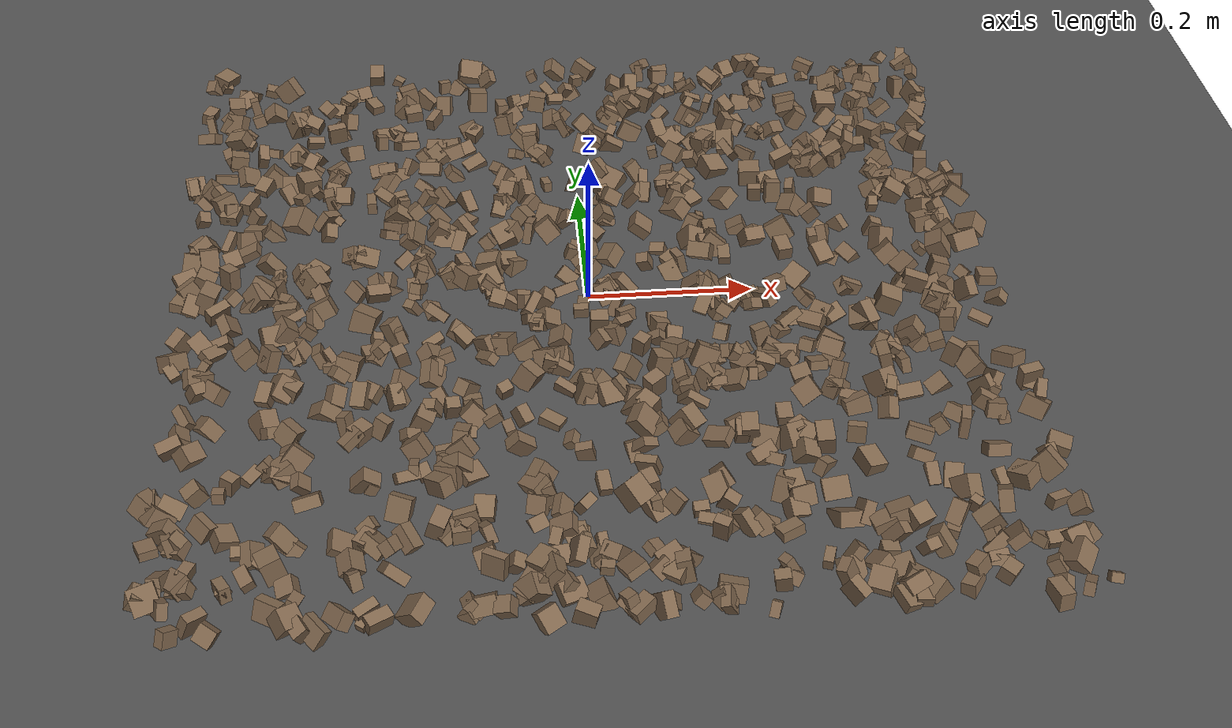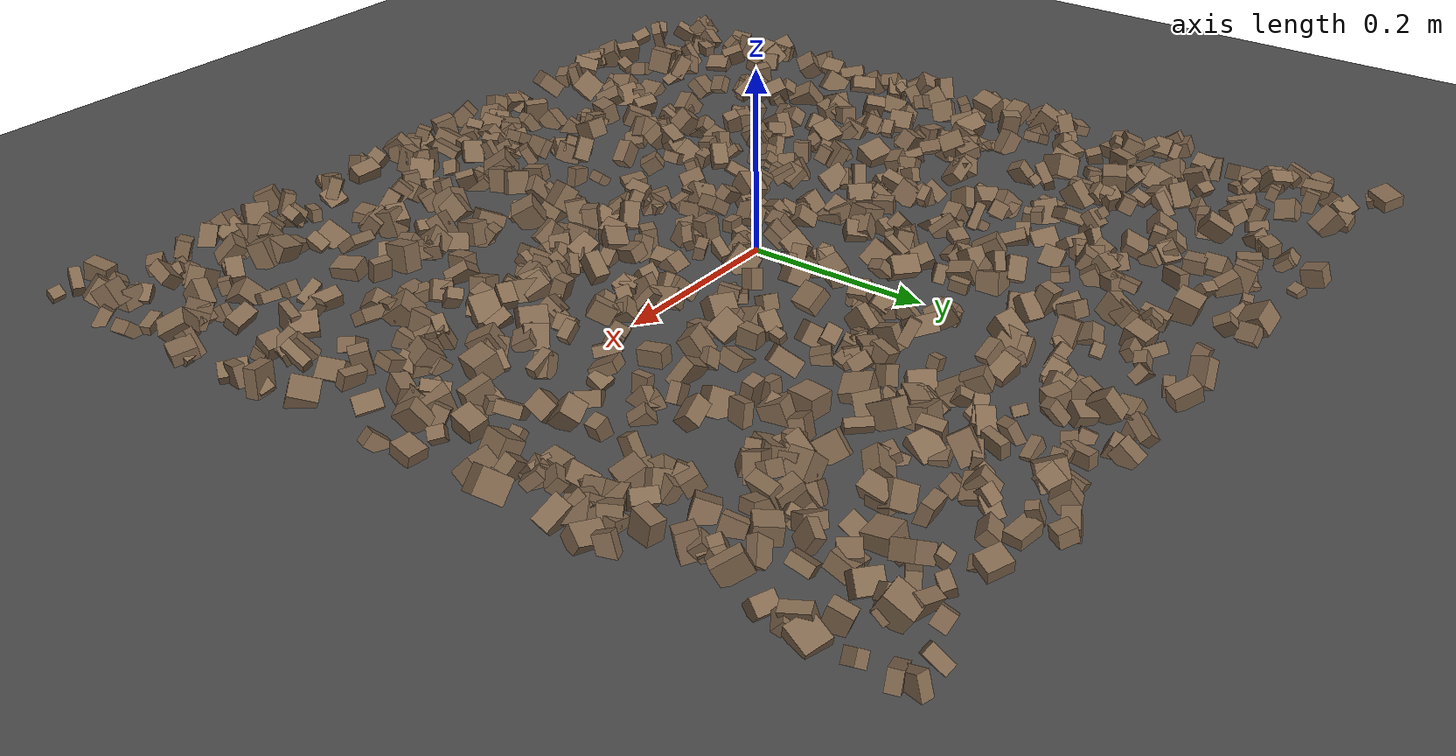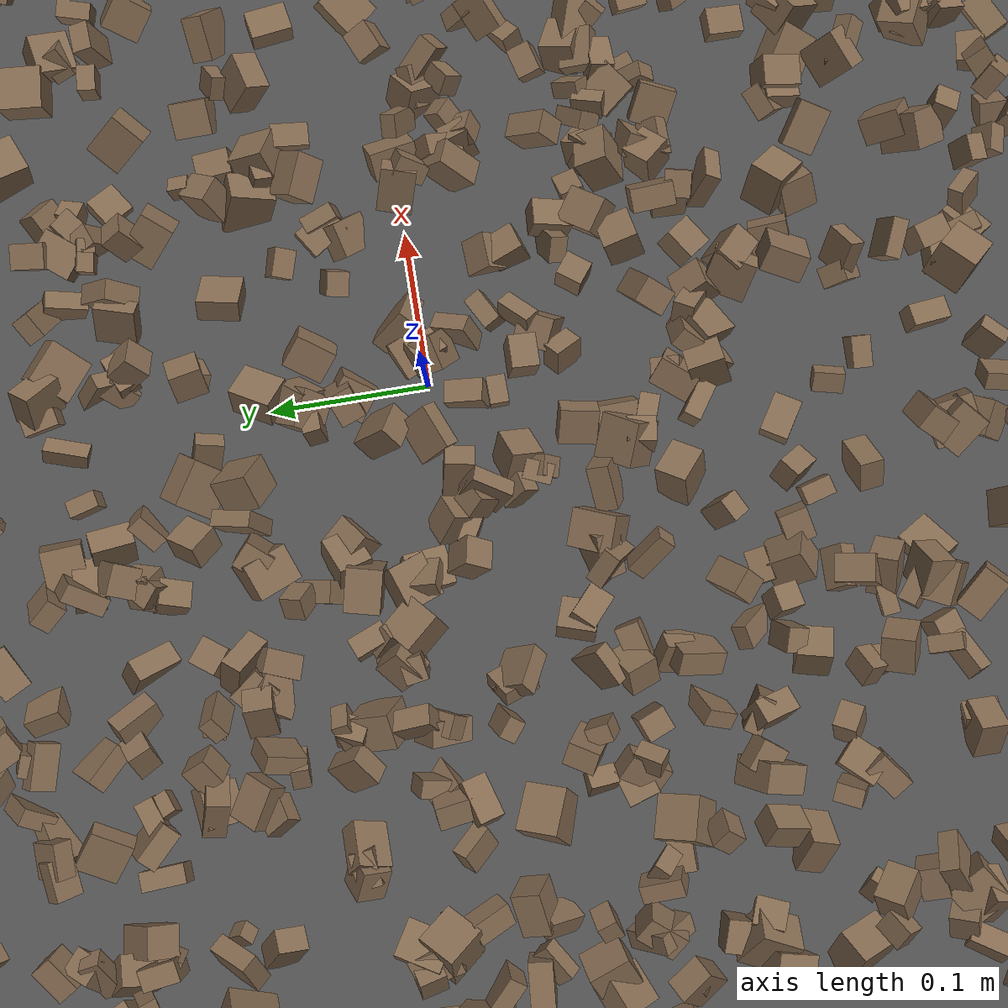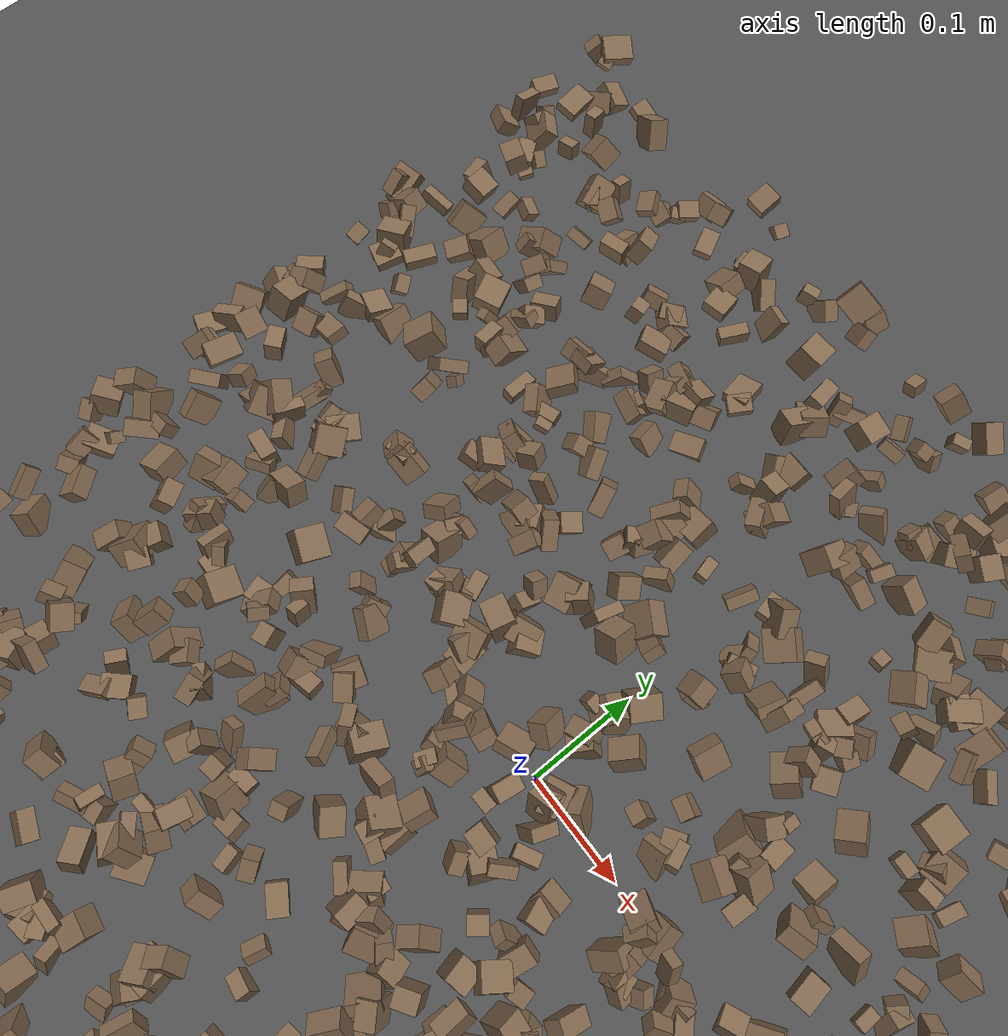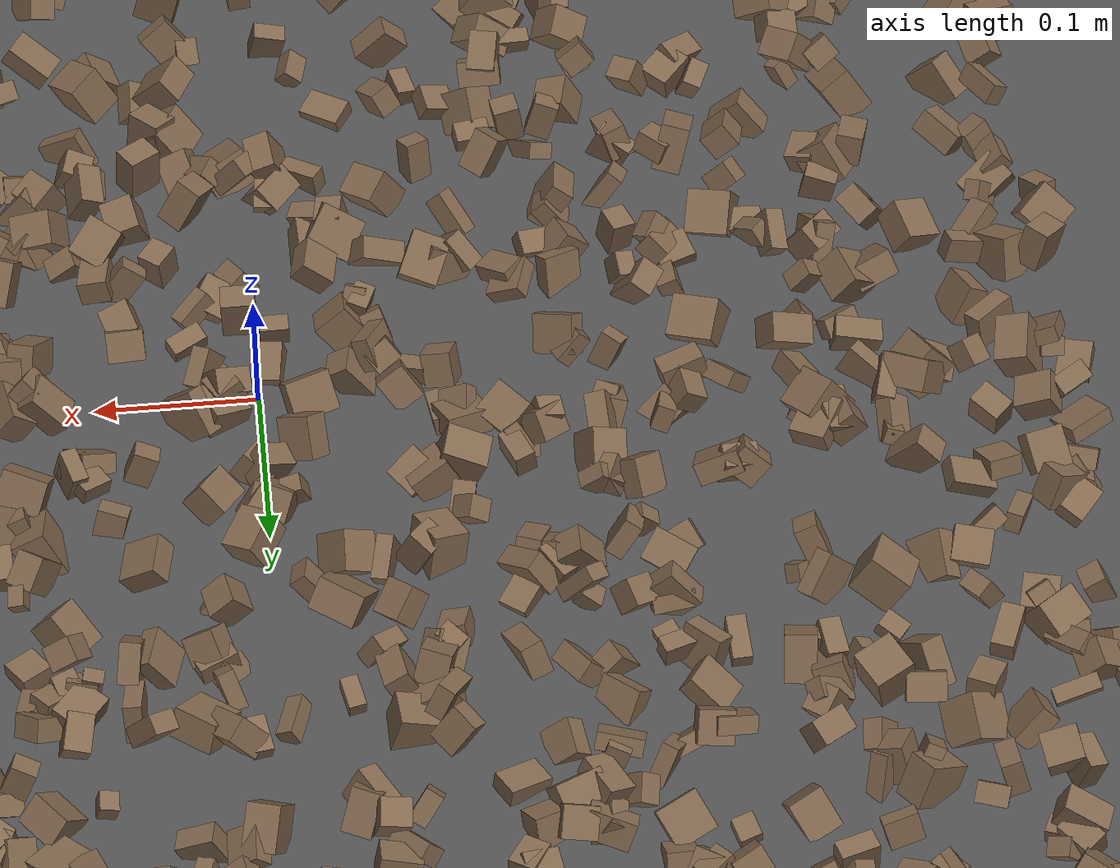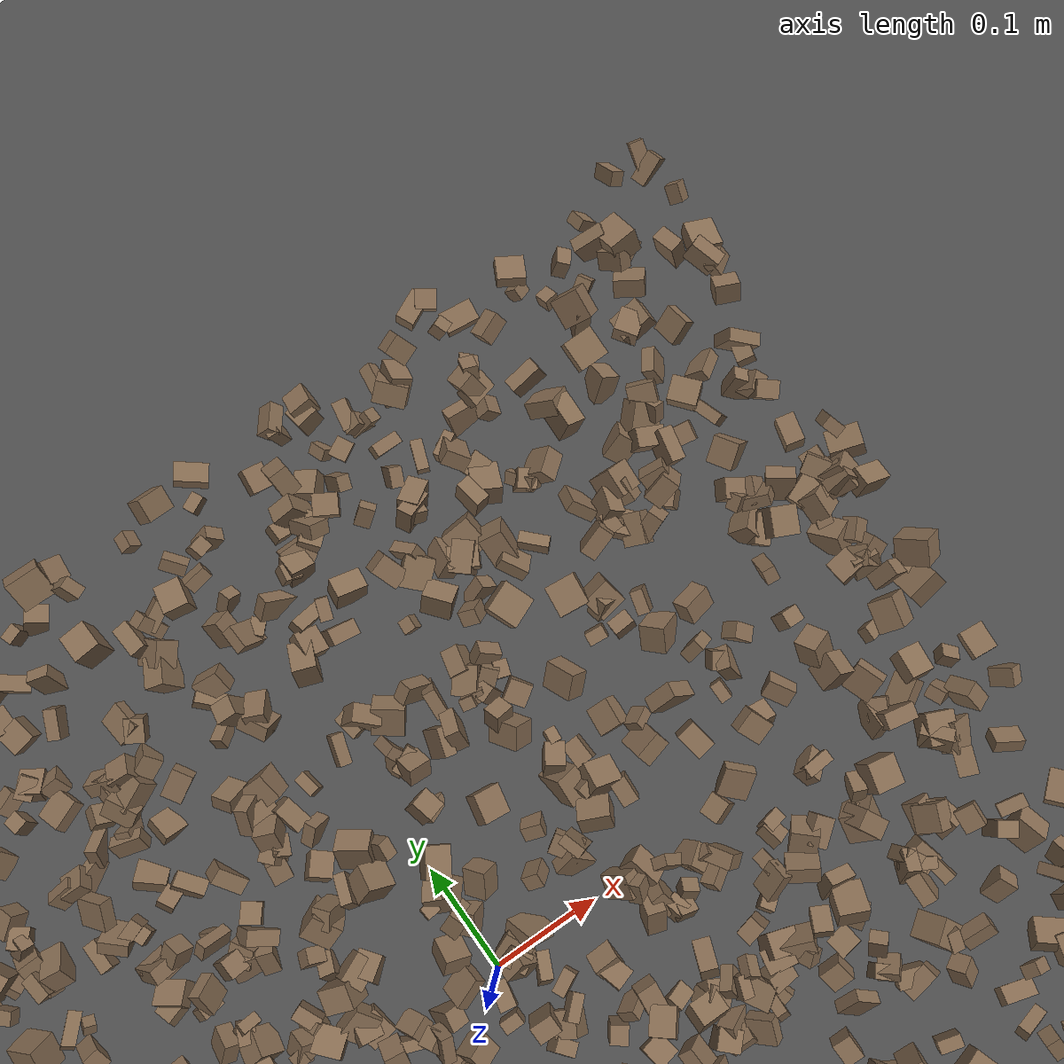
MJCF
<mujoco model="rocky_terrain_scene">
    <compiler angle="radian" inertiafromgeom="true" />
    <option timestep="0.002" gravity="0 0 -9.81" />

    <worldbody>
        <light name="sunlight" pos="5 5 5" dir="-1 -1 -1" diffuse="1 1 1" specular="0.5 0.5 0.5" ambient="0.5 0.5 0.5" />

        <geom name="ground_plane" type="plane" size="50 50 0.1" rgba="0.3 0.3 0.3 1" />

        <body name="rocky_terrain_body">

        <geom name="rock1" type="box" size="0.005799372089397262 0.007887883452599071 0.009700233579003075" pos="-0.0801124063472991 -0.36140979303977083 7.220259144448738e-05" quat="0.36473099076758525 0.04756680236247561 0.3645899798088894 0.2231122270610498" rgba="0.5 0.4 0.3 1" /><geom name="rock2" type="box" size="0.010935886045155361 0.005965822853014069 0.008710791491954084" pos="-0.4634969204030125 0.2039759028091903 0.0017665420020827188" quat="0.3233469498835511 0.03651770355999002 0.08452654617518085 0.555608800381278" rgba="0.5 0.4 0.3 1" /><geom name="rock3" type="box" size="0.00777299541863658 0.013650211160545756 0.01111767990501549" pos="0.01949525322833745 -0.006561578796626444 0.011097376625458679" quat="0.33756573624298064 0.12192300240400662 0.28365529987887367 0.256855961474139" rgba="0.5 0.4 0.3 1" /><geom name="rock4" type="box" size="0.012659729065625729 0.01279198986198805 0.012884417260018148" pos="-0.35120169856604266 0.23438237191703215 0.014992935087030914" quat="0.4063336620576671 0.40183896391844487 0.12802774244699416 0.06379963157689397" rgba="0.5 0.4 0.3 1" /><geom name="rock5" type="box" size="0.010012515365147183 0.012626109098501606 0.009631768080416252" pos="-0.32205884109574545 0.22510013953342023 0.0038074669670003563" quat="0.3142351261380342 0.12621454498636 0.46187198205018526 0.09767834682542054" rgba="0.5 0.4 0.3 1" /><geom name="rock6" type="box" size="0.011350056863628253 0.008370093862383307 0.0067123272856613615" pos="0.16342432450343203 0.35923714297445064 0.010150857213493696" quat="0.4009231055194047 0.018448412775184924 0.22641173658202016 0.3542167451233902" rgba="0.5 0.4 0.3 1" /><geom name="rock7" type="box" size="0.008280831569496548 0.00994640325461037 0.013182334504393638" pos="0.3124318480425242 0.1595947721927824 0.014783875274024557" quat="0.2868876875793868 0.12313738701916975 0.4528958697757561 0.13707905562568745" rgba="0.5 0.4 0.3 1" /><geom name="rock8" type="box" size="0.009053449268943357 0.011293023946424646 0.01363230538066141" pos="-0.15824138580522318 -0.2572598597174828 0.00927718551929352" quat="0.4326982433226182 0.13033060527829562 0.18510532907546212 0.2518658223236241" rgba="0.5 0.4 0.3 1" /><geom name="rock9" type="box" size="0.005944586195096215 0.0059718276018986835 0.010924690228338712" pos="-0.02638999707404377 0.4357238736485296 0.0134427369587403" quat="0.29223496751006833 0.4881677712386223 0.030587267900174037 0.18900999335113539" rgba="0.5 0.4 0.3 1" /><geom name="rock10" type="box" size="0.00974080621837324 0.008350851953344276 0.012766829445971534" pos="0.34987717034921717 -0.1268139913062719 0.0015991238394586914" quat="0.3878492796006064 0.5014721026190571 0.049911635344994786 0.06076698243534177" rgba="0.5 0.4 0.3 1" /><geom name="rock11" type="box" size="0.01057941939530787 0.010338351763188534 0.012641168793816694" pos="0.33924739238822965 0.3046969553546147 0.0014220309201904994" quat="0.4750944480577886 0.025870877946395764 0.3134200168692896 0.185614657126526" rgba="0.5 0.4 0.3 1" /><geom name="rock12" type="box" size="0.012481082767978444 0.014587109110181101 0.010443868357459331" pos="0.4409546585984736 0.1388192759302449 0.00430260266223542" quat="0.04955692885674818 0.40351086550085835 0.24249314020474338 0.3044390654376501" rgba="0.5 0.4 0.3 1" /><geom name="rock13" type="box" size="0.012399497174016583 0.011330073343950847 0.007361931848306129" pos="0.2997616453143205 0.2667441828767658 0.01372303466617934" quat="0.2679195451688419 0.34690434036458334 0.33899026682786787 0.046185847638706826" rgba="0.5 0.4 0.3 1" /><geom name="rock14" type="box" size="0.012941205270910413 0.01214116749306022 0.012516275879591476" pos="0.25206502613813253 0.20824713717655075 0.003599609782383522" quat="0.3614017113397684 0.5546423533384764 0.04213100014383137 0.04182493517792377" rgba="0.5 0.4 0.3 1" /><geom name="rock15" type="box" size="0.005348476569940439 0.0062948821644469456 0.009703938121388877" pos="-0.4854595826511612 0.21620575894758365 0.0018631822262580742" quat="0.24133778448022714 0.3120182124203374 0.413108355154037 0.03353564794539851" rgba="0.5 0.4 0.3 1" /><geom name="rock16" type="box" size="0.0063732992437886635 0.011026229341875665 0.013650681145114259" pos="-0.19668369318974943 0.23114631116623297 0.000858576953102046" quat="0.2650152218709822 0.4548654204915945 0.012477278795887869 0.2676420788415354" rgba="0.5 0.4 0.3 1" /><geom name="rock17" type="box" size="0.012915313748223863 0.005747650170108738 0.013085781451857813" pos="0.0707238606464301 0.18526175689706337 0.011497461222498296" quat="0.4330820994781031 0.1414649779117652 0.10317237815413405 0.3222805444559977" rgba="0.5 0.4 0.3 1" /><geom name="rock18" type="box" size="0.010803705496906797 0.01295520690025816 0.013605344690369711" pos="0.1201455736472552 0.21542358448343502 0.004695377560192506" quat="0.16385535860104344 0.09756656681568628 0.36515824388285717 0.37341983070041307" rgba="0.5 0.4 0.3 1" /><geom name="rock19" type="box" size="0.005437971247976846 0.005038201100620243 0.014240785562476238" pos="-0.46074982290382194 0.2563469487692783 0.01249075813759809" quat="0.026567547626024975 0.46136124823873254 0.12477317197293852 0.38729803216230385" rgba="0.5 0.4 0.3 1" /><geom name="rock20" type="box" size="0.014236270460556914 0.006969322598003909 0.014882304882409682" pos="0.44665580129046156 0.1793372112716235 0.006899828364346433" quat="0.18564248281504964 0.21215295474846269 0.3028186469801634 0.29938591545632415" rgba="0.5 0.4 0.3 1" /><geom name="rock21" type="box" size="0.01295753364933196 0.008174690786192028 0.010949077428368554" pos="-0.002620356480427466 -0.41092912643190604 0.005794624455163203" quat="0.44161382416754386 0.2297605000994322 0.3255565020723045 0.003069173660719459" rgba="0.5 0.4 0.3 1" /><geom name="rock22" type="box" size="0.009361037228503802 0.005500670958413079 0.014036697627605586" pos="-0.13358306991821123 0.28265974550217954 0.0015869725675447643" quat="0.18803173497996925 0.18864964475997137 0.25473486826981606 0.36858375199024335" rgba="0.5 0.4 0.3 1" /><geom name="rock23" type="box" size="0.007221783867006231 0.012978819751947143 0.008773517827004612" pos="0.4332475267235517 -0.22443457057044214 0.011008729571154586" quat="0.4358764589363783 0.08825510600164538 0.11535666470598646 0.3605117703559899" rgba="0.5 0.4 0.3 1" /><geom name="rock24" type="box" size="0.014855998868394872 0.009577632784783767 0.009242010296374423" pos="0.1498139926832307 0.0003881190108457888 0.007878168963981769" quat="0.30112405177300877 0.15801986242821597 0.15007707908744428 0.390779006711331" rgba="0.5 0.4 0.3 1" /><geom name="rock25" type="box" size="0.012628771709422146 0.012444009467999981 0.006381066394603336" pos="0.16246200782290687 0.45725270505620863 0.000633516966806853" quat="0.26884706559930704 0.2758468786221841 0.22573111303640145 0.22957494274210732" rgba="0.5 0.4 0.3 1" /><geom name="rock26" type="box" size="0.014077702399196326 0.006832704771399586 0.013463165682584047" pos="0.039799694340862724 -0.19808554940057088 0.007119656009250203" quat="0.44966305442915966 0.1867963103625222 0.09240756907944009 0.27113306612887805" rgba="0.5 0.4 0.3 1" /><geom name="rock27" type="box" size="0.008923298403957808 0.005704845900542862 0.011578821334193756" pos="-0.11181254833827714 0.46923732200765333 0.013626075119287677" quat="0.29399349598800334 0.21918855242266524 0.03912769849136893 0.4476902530979625" rgba="0.5 0.4 0.3 1" /><geom name="rock28" type="box" size="0.009112090423713817 0.006758365346726729 0.011894764030151564" pos="-0.14993291748476933 -0.4724215131110693 0.006489009849549905" quat="0.17988696084784567 0.31881533138650664 0.43861480068647984 0.06268290707916786" rgba="0.5 0.4 0.3 1" /><geom name="rock29" type="box" size="0.011739674492156123 0.010018300750045612 0.013608729756904327" pos="-0.08312938635177214 0.3831404219000809 0.005128452155552103" quat="0.4605603220485593 0.2134226692749685 0.10769119410824324 0.21832581456822897" rgba="0.5 0.4 0.3 1" /><geom name="rock30" type="box" size="0.0062128710197392415 0.012260056216148459 0.008206162435496381" pos="0.004771956379739484 0.43766875856835186 0.0024152425456856128" quat="0.22143564651489414 0.39973336561341144 0.3708539724338108 0.007977015437883662" rgba="0.5 0.4 0.3 1" /><geom name="rock31" type="box" size="0.014119320937689864 0.01152085409240958 0.005189426741981741" pos="-0.17236268740857585 -0.25516032448631676 0.0008074400145856935" quat="0.5008107912003592 0.45018610758871025 0.00016473267519326055 0.04883836853573723" rgba="0.5 0.4 0.3 1" /><geom name="rock32" type="box" size="0.014557117787257066 0.007539359744794366 0.00790865718288288" pos="0.3489080420262657 -0.2662102179812408 0.007543719231558917" quat="0.10413209073905273 0.07598553877465906 0.1342741343914538 0.6856082360948345" rgba="0.5 0.4 0.3 1" /><geom name="rock33" type="box" size="0.011120808132922011 0.014921334331430221 0.006904104076631274" pos="0.2194092219066266 0.37820338287395894 0.01376723787508935" quat="0.14362013676966717 0.22530244446111425 0.19682336796929115 0.43425405079992746" rgba="0.5 0.4 0.3 1" /><geom name="rock34" type="box" size="0.0073150171551558014 0.006694853432898163 0.012316065664816297" pos="0.4359431582547374 0.4370712005625945 0.007045579588845299" quat="0.36789867945198274 0.05242007314699543 0.33985883421717156 0.23982241318385025" rgba="0.5 0.4 0.3 1" /><geom name="rock35" type="box" size="0.011838772208208054 0.007226403791330233 0.01158278104894447" pos="0.2216326127298287 -0.2640607634609756 0.012917011842216653" quat="0.2993216078990287 0.3472332989588185 0.15510200234423852 0.19834309079791437" rgba="0.5 0.4 0.3 1" /><geom name="rock36" type="box" size="0.007503228068712831 0.007621375106560956 0.010630368907213805" pos="0.029357507585440312 -0.33502662430751495 0.010354992056554584" quat="0.15516427928833837 0.28425532871430254 0.3171671866675556 0.24341320532980357" rgba="0.5 0.4 0.3 1" /><geom name="rock37" type="box" size="0.013356897954400149 0.011253860811303133 0.01237803537321479" pos="-0.20154688995493486 0.06131271066606703 0.006075703870024872" quat="0.1812354477500629 0.3985918941382666 0.41636472810085295 0.003807930010817564" rgba="0.5 0.4 0.3 1" /><geom name="rock38" type="box" size="0.006203747717398182 0.012128475450386252 0.005887416075885003" pos="0.3840833679698591 -0.3718823530991632 0.0020227814285138767" quat="0.11191693591211518 0.172260590120443 0.3408711961329784 0.3749512778344634" rgba="0.5 0.4 0.3 1" /><geom name="rock39" type="box" size="0.008956580926294831 0.006365334285882417 0.0067802739368737685" pos="-0.25594779795748335 -0.06441425127540534 0.001311929010834313" quat="0.39768114571852264 0.12269343042623891 0.03545681197383519 0.44416861188140316" rgba="0.5 0.4 0.3 1" /><geom name="rock40" type="box" size="0.013774932471041001 0.009817714296198411 0.014948427163368243" pos="-0.394855441292719 0.024258711262052812 0.011613761568599109" quat="0.20744741143428344 0.47058622642440257 0.029232488216178253 0.29273387392513567" rgba="0.5 0.4 0.3 1" /><geom name="rock41" type="box" size="0.008464976240398324 0.006677458196399019 0.007735379860049495" pos="0.2641227549412638 0.3942881994667343 0.004258369474550988" quat="0.1991237955511417 0.4200580122039831 0.35622242774895735 0.024595764495917834" rgba="0.5 0.4 0.3 1" /><geom name="rock42" type="box" size="0.005432477801509817 0.013691854838267042 0.01313564742573933" pos="-0.12697519311379157 -0.4253104619425617 0.013698547337288364" quat="0.3387900826032699 0.2908226638663393 0.2143895839300594 0.1559976696003313" rgba="0.5 0.4 0.3 1" /><geom name="rock43" type="box" size="0.007246038733136794 0.014423788122192856 0.008698298807341283" pos="0.4560928654016675 0.2840875520426729 0.0075768905080420825" quat="0.04035405090466509 0.29140770719670955 0.3156657434304129 0.3525724984682124" rgba="0.5 0.4 0.3 1" /><geom name="rock44" type="box" size="0.0066652990862465485 0.009398765702020551 0.005172698450024129" pos="0.17565684204914267 -0.11921271882338802 0.011434058530511933" quat="0.16925657390983606 0.24191188274897474 0.11205538226983594 0.4767761610713532" rgba="0.5 0.4 0.3 1" /><geom name="rock45" type="box" size="0.009511343444388204 0.010769155689034656 0.009786093953529744" pos="-0.08999550920735955 0.20482868888102612 0.013877679981669666" quat="0.23741616716567218 0.35253056992765625 0.09951049209369348 0.31054277081297804" rgba="0.5 0.4 0.3 1" /><geom name="rock46" type="box" size="0.012417765854263126 0.013283286333293298 0.011409892141748836" pos="-0.04400033611506504 0.12173729345593232 0.01086219551042946" quat="0.3770998646538282 0.09205226899510358 0.24152682528569716 0.2893210410653711" rgba="0.5 0.4 0.3 1" /><geom name="rock47" type="box" size="0.013671867280358817 0.010686773555269855 0.0055311934320216305" pos="-0.07163758979617119 -0.024481109553607605 0.013131775310501888" quat="0.17743569180630148 0.424246627782453 0.18964147172157222 0.20867620868967343" rgba="0.5 0.4 0.3 1" /><geom name="rock48" type="box" size="0.010429297508250487 0.014770222650083788 0.012001478721541975" pos="-0.10764978261353464 -0.08818550802928449 0.009520531414164769" quat="0.17564465951078795 0.3717113282835329 0.01645149343789319 0.4361925187677859" rgba="0.5 0.4 0.3 1" /><geom name="rock49" type="box" size="0.00861711570977747 0.013723558557865986 0.007859019726759224" pos="0.01760826446642927 -0.48577202112159623 0.007214076014276551" quat="0.07436155761470385 0.28438349865143986 0.598782276237194 0.04247266749666223" rgba="0.5 0.4 0.3 1" /><geom name="rock50" type="box" size="0.005101925948567683 0.012909967604242158 0.0052154643837446" pos="-0.3444788703943428 -0.21364873130517525 0.0023124709807861815" quat="0.041468070336617195 0.25712139853669863 0.3272567391945424 0.3741537919321418" rgba="0.5 0.4 0.3 1" /><geom name="rock51" type="box" size="0.0059059167863011516 0.012740339005126732 0.007892242729465447" pos="-0.48529011105942055 0.10349191288509263 0.0034323814968411775" quat="0.05477734393612904 0.46484814794137047 0.2087784457763906 0.27159606234611" rgba="0.5 0.4 0.3 1" /><geom name="rock52" type="box" size="0.005081606578757452 0.014510986141866414 0.007549520309087075" pos="-0.18106690857399166 0.15650077261701045 0.01399157653420461" quat="0.29265219389048336 0.07431647722738598 0.26834123541752497 0.3646900934646057" rgba="0.5 0.4 0.3 1" /><geom name="rock53" type="box" size="0.013776754529534516 0.008713668078593756 0.01148004838811509" pos="0.3981419999556396 -0.241108012710177 0.009408211110606069" quat="0.08261608066277575 0.17717577125683245 0.49914978719611686 0.24105836088427485" rgba="0.5 0.4 0.3 1" /><geom name="rock54" type="box" size="0.006265245477370536 0.01346184108059829 0.010252392342239885" pos="0.14880440421047303 -0.24101976426945815 0.004921984300668433" quat="0.3106518572237112 0.09848891042385506 0.33453488039918317 0.2563243519532506" rgba="0.5 0.4 0.3 1" /><geom name="rock55" type="box" size="0.013339343191027468 0.011556263998905594 0.008388140790737906" pos="-0.4085758378163191 -0.36081469574182456 0.0020143459721381446" quat="0.3245927885653429 0.08906028429837594 0.09449778680818208 0.4918491403280991" rgba="0.5 0.4 0.3 1" /><geom name="rock56" type="box" size="0.006984165508970476 0.01058660186852426 0.007747687162871044" pos="0.07298115145761341 0.04804677307968175 0.011672281588174512" quat="0.2787730903935265 0.2645151232619053 0.1420099933156514 0.31470179302891693" rgba="0.5 0.4 0.3 1" /><geom name="rock57" type="box" size="0.013136422751745112 0.00853489745840541 0.009078041311321446" pos="0.24842243577135992 0.06474979481314147 0.011040639008908476" quat="0.21690673448466802 0.24052251231640506 0.25969980435198015 0.28287094884694675" rgba="0.5 0.4 0.3 1" /><geom name="rock58" type="box" size="0.013908373489561542 0.010563393258864679 0.011090106592777652" pos="0.009966614519920425 0.10466922499348075 0.010895284691121322" quat="0.2773480929606005 0.3700262806102384 0.24043904310574962 0.11218658332341151" rgba="0.5 0.4 0.3 1" /><geom name="rock59" type="box" size="0.006190147711532472 0.011169652923040289 0.01426131130986065" pos="-0.44666364370965117 -0.0112270890899423 0.010939177338953956" quat="0.11402179603339792 0.21054996409588259 0.3045971953655278 0.37083104450519166" rgba="0.5 0.4 0.3 1" /><geom name="rock60" type="box" size="0.005897261904599477 0.01440265961716002 0.013943591762844328" pos="-0.09382857393903965 0.228235464110929 0.010913712675390836" quat="0.18750231002690396 0.047456223853227786 0.2824668358084758 0.48257463031139236" rgba="0.5 0.4 0.3 1" /><geom name="rock61" type="box" size="0.00554531334345183 0.007220351936187449 0.010062920760782704" pos="-0.21898621415545882 0.11265809838647889 0.006629442811305596" quat="0.13239065553723997 0.35856783776589923 0.35232148743447844 0.1567200192623824" rgba="0.5 0.4 0.3 1" /><geom name="rock62" type="box" size="0.013316557297291504 0.006262155146043382 0.012629296097216159" pos="0.27642355980200684 -0.10454034137732848 0.002040174170835041" quat="0.1455866328827476 0.5020029560034395 0.07244577087130455 0.2799646402425085" rgba="0.5 0.4 0.3 1" /><geom name="rock63" type="box" size="0.01072306407465503 0.013788914729120402 0.005438577463778754" pos="-0.03635936753924063 -0.40622320203709483 0.008555443567650634" quat="0.12921561223061748 0.2987928699875679 0.36935933467844206 0.20263218310337247" rgba="0.5 0.4 0.3 1" /><geom name="rock64" type="box" size="0.006097331852306093 0.009159231491288137 0.009210003547459237" pos="-0.4507140321305684 -0.49207882207089904 0.010442313541660966" quat="0.14454056737709672 0.14213710294426776 0.4613655328258574 0.25195679685277816" rgba="0.5 0.4 0.3 1" /><geom name="rock65" type="box" size="0.014070829536654963 0.0075143890708756055 0.006732584655638776" pos="0.21984662617730488 -0.13497765107841542 0.0070360822747860185" quat="0.2906123625319778 0.02633708376186479 0.34504830917582335 0.33800224453033406" rgba="0.5 0.4 0.3 1" /><geom name="rock66" type="box" size="0.010326456011380571 0.005840261522748159 0.010550299699662223" pos="-0.18877939813941136 -0.12148102679944628 0.005196375589085913" quat="0.3692734232148444 0.2188934122394762 0.05806493145736136 0.353768233088318" rgba="0.5 0.4 0.3 1" /><geom name="rock67" type="box" size="0.008207344726170544 0.011507272438640585 0.010566724799021307" pos="-0.0023512136641069548 0.05342237486270063 0.00853181600008112" quat="0.27106360263789536 0.13662388285319385 0.2198931410490134 0.37241937345989745" rgba="0.5 0.4 0.3 1" /><geom name="rock68" type="box" size="0.006505050637838832 0.013880346545957694 0.00735790165979089" pos="-0.06163025139228506 -0.05639328693026746 0.008788653576822172" quat="0.09372776441153373 0.01706908029692278 0.24333456757440433 0.6458685877171392" rgba="0.5 0.4 0.3 1" /><geom name="rock69" type="box" size="0.01294122962112891 0.012638551502607842 0.012766404599150096" pos="0.47533092594835613 0.1781184398724508 0.010207549726469319" quat="0.06295021986743776 0.362194301988254 0.3740120048194415 0.2008434733248667" rgba="0.5 0.4 0.3 1" /><geom name="rock70" type="box" size="0.006701998409316082 0.01306008729552097 0.012902256218130195" pos="0.24189110604186692 0.39959202698198426 0.00024882949646592767" quat="0.3103566398390774 0.18529969057860304 0.36824878568809144 0.13609488389422814" rgba="0.5 0.4 0.3 1" /><geom name="rock71" type="box" size="0.011525224520804619 0.014383037164989312 0.0059245031764689135" pos="-0.4579566097869945 0.30345457646580165 0.007613647823650859" quat="0.252287366247643 0.18237980997260497 0.242193580624148 0.32313924315560405" rgba="0.5 0.4 0.3 1" /><geom name="rock72" type="box" size="0.011267846645248113 0.008577267929004569 0.010109237257504605" pos="-0.07349117017049345 0.1571396541380291 0.007295941955634493" quat="0.30790615614956973 0.3744372931735017 0.2753747661392254 0.04228178453770304" rgba="0.5 0.4 0.3 1" /><geom name="rock73" type="box" size="0.014188306761506387 0.010361771471881574 0.010847226548573844" pos="0.37453457040610516 0.07094910280511679 0.01272084409554874" quat="0.06135290189624283 0.4179857025401768 0.21602520828259433 0.304636187280986" rgba="0.5 0.4 0.3 1" /><geom name="rock74" type="box" size="0.011766298205408119 0.005035810459528731 0.014241714987969167" pos="-0.49296100447803803 0.06162471352806931 0.0021548228242289596" quat="0.09599257922060356 0.2683391455379328 0.2744444514474638 0.36122382379399975" rgba="0.5 0.4 0.3 1" /><geom name="rock75" type="box" size="0.01282023058574484 0.010510621086958718 0.007125759366729398" pos="0.4136899637225625 -0.4269825403300386 0.014728601561546694" quat="0.2130658335014912 0.36254380139274833 0.3614384320651262 0.06295193304063429" rgba="0.5 0.4 0.3 1" /><geom name="rock76" type="box" size="0.009226041242773372 0.012655350911760715 0.006034321335331492" pos="0.29546008572728977 0.25541257782958104 0.008384610849124096" quat="0.2487563383070815 0.24758170263892929 0.24278491690977372 0.26087704214421553" rgba="0.5 0.4 0.3 1" /><geom name="rock77" type="box" size="0.006388397952507572 0.013630839825265594 0.008054281360249603" pos="0.1677363658651283 0.44465835722758884 0.0007899137011968027" quat="0.34736272409123803 0.16662554205235838 0.22743547497663208 0.2585762588797714" rgba="0.5 0.4 0.3 1" /><geom name="rock78" type="box" size="0.012613557005495905 0.01274829732496404 0.006496538557021738" pos="0.08688306524374545 0.18692352902643972 0.01422722405199618" quat="0.17169604298503954 0.3767928257761292 0.10222961061624745 0.3492815206225837" rgba="0.5 0.4 0.3 1" /><geom name="rock79" type="box" size="0.012626795412599163 0.008222114964565735 0.012160854798825718" pos="0.2960048676129525 -0.47725586914316165 0.01033985479456125" quat="0.3847811135785854 0.04512852280772331 0.3414480641194583 0.22864229949423304" rgba="0.5 0.4 0.3 1" /><geom name="rock80" type="box" size="0.009973608325524908 0.012885281034957428 0.011151117727229393" pos="-0.2982114299234828 0.3182170205267145 0.0002548151949061356" quat="0.035036230482589165 0.3736671266862547 0.23101895131186906 0.3602776915192871" rgba="0.5 0.4 0.3 1" /><geom name="rock81" type="box" size="0.010889160340679677 0.009900151087753647 0.005740949237119941" pos="-0.06015071593493426 0.18436303129925247 0.0034979606388843374" quat="0.4030923516883577 0.35482707701756283 0.016341612812240867 0.22573895848183861" rgba="0.5 0.4 0.3 1" /><geom name="rock82" type="box" size="0.012276757435885627 0.0112848628164742 0.013579713122787752" pos="0.2054122046778366 -0.2641837587425778 0.011848760743907095" quat="0.2721846982229467 0.5552981491074263 0.1706120617597487 0.0019050909098783243" rgba="0.5 0.4 0.3 1" /><geom name="rock83" type="box" size="0.0056542612543604735 0.01483023300211941 0.008426473251954572" pos="0.07828443149560682 -0.08957996913588018 0.0058367506427406375" quat="0.30890520415578465 0.2281537204453379 0.10497522228325194 0.3579658531156255" rgba="0.5 0.4 0.3 1" /><geom name="rock84" type="box" size="0.01219278190799688 0.008554995812616897 0.006260675457177124" pos="0.3703489275771653 0.40884860198607087 0.006399994748192319" quat="0.19668799159447622 0.46612235241552674 0.045810600114961415 0.29137905587503565" rgba="0.5 0.4 0.3 1" /><geom name="rock85" type="box" size="0.013527101037558678 0.014927326841305648 0.009262128320371904" pos="0.21135943211152042 0.4559568660743498 0.00446926291900015" quat="0.27738720245474174 0.29694836339109937 0.3834697416609049 0.04219469249325402" rgba="0.5 0.4 0.3 1" /><geom name="rock86" type="box" size="0.010573213081535889 0.008631638289226952 0.008436918746863767" pos="0.3964487143252152 -0.4659499883384932 0.005899706420144413" quat="0.32532239925536055 0.36502084313626204 0.1873821693224982 0.12227458828587917" rgba="0.5 0.4 0.3 1" /><geom name="rock87" type="box" size="0.012179012600783135 0.009979995194544043 0.010329153487926927" pos="-0.27421958274110725 -0.40897837729941267 0.0063191805229826726" quat="0.09923810844138152 0.3387400152441155 0.3732035021675037 0.1888183741469993" rgba="0.5 0.4 0.3 1" /><geom name="rock88" type="box" size="0.005672730488407072 0.006153343754293092 0.009543957775271204" pos="0.11649400685390288 0.20075693975716358 0.011248426633130769" quat="0.22587518926416197 0.31786480618837876 0.15755999551864722 0.29870000902881205" rgba="0.5 0.4 0.3 1" /><geom name="rock89" type="box" size="0.010032730360552623 0.013353363757172703 0.010776661645957107" pos="-0.16228915263588506 0.31407244928954303 0.006213163133496039" quat="0.3632782677130108 0.16833625107289146 0.2933475350263185 0.17503794618777926" rgba="0.5 0.4 0.3 1" /><geom name="rock90" type="box" size="0.007323694817257212 0.0067247455822604905 0.009925839921628852" pos="-0.15474958301571518 -0.36523991214654083 0.007591055492128072" quat="0.3920530720929656 0.32667606290616485 0.12686195391246627 0.1544089110884032" rgba="0.5 0.4 0.3 1" /><geom name="rock91" type="box" size="0.010090073525019273 0.011057371049139831 0.005757152213169943" pos="-0.1333222620634511 -0.3726542279031755 0.001140309959255763" quat="0.30254210998152486 0.09553517519230648 0.3435050128587602 0.25841770196740854" rgba="0.5 0.4 0.3 1" /><geom name="rock92" type="box" size="0.012414872785305394 0.013809886669260647 0.01043669143869667" pos="-0.08048165635688787 -0.14456694884003674 0.007669489348658917" quat="0.03835839517868758 0.21374062923936926 0.41907947641717064 0.32882149916477255" rgba="0.5 0.4 0.3 1" /><geom name="rock93" type="box" size="0.008882603950423907 0.006537789048932994 0.007698114804003071" pos="0.14251856181241362 0.4363631319350064 0.00032329412206683116" quat="0.3800869069979585 0.4143034610470971 0.12105210826292546 0.08455752369201891" rgba="0.5 0.4 0.3 1" /><geom name="rock94" type="box" size="0.009537778803159865 0.011095998214126695 0.014185486701744781" pos="0.1440332478376819 0.06168921204541378 0.014098774864804467" quat="0.23104283743295612 0.35887090325607796 0.07097398948769752 0.3391122698232685" rgba="0.5 0.4 0.3 1" /><geom name="rock95" type="box" size="0.007491530178476655 0.008173925134338053 0.013518391628350914" pos="-0.45916467689682694 -0.3710522154865622 0.009539800889267428" quat="0.4484101169667025 0.15428600500615713 0.12816754157849955 0.26913633644864077" rgba="0.5 0.4 0.3 1" /><geom name="rock96" type="box" size="0.0071603237376039715 0.011070998050064685 0.014069457729662244" pos="-0.2716678206283104 0.07922134279731119 0.013417856225151627" quat="0.29517011938757187 0.1432269832417545 0.4543615870172938 0.10724131035337973" rgba="0.5 0.4 0.3 1" /><geom name="rock97" type="box" size="0.012076539787782446 0.009132163680717075 0.009167097054337695" pos="0.466606083107599 0.19674127473302483 0.0014338062735401896" quat="0.29187641188045 0.2173338636771804 0.22231016473674667 0.26847955970562287" rgba="0.5 0.4 0.3 1" /><geom name="rock98" type="box" size="0.012898949223188374 0.011275419820489109 0.005438073040341287" pos="0.20847412939869925 0.274030626331096 0.013547724246459617" quat="0.21351401088965594 0.1855453665759093 0.16874425492002215 0.4321963676144126" rgba="0.5 0.4 0.3 1" /><geom name="rock99" type="box" size="0.011327527863481977 0.006142918547449213 0.006735673133557786" pos="0.22250224366202265 -0.08265674662030564 0.002613657930278057" quat="0.39829620041461355 0.3678004274886064 0.20298600998003144 0.030917362116748528" rgba="0.5 0.4 0.3 1" /><geom name="rock100" type="box" size="0.008673819536374496 0.014479615326232192 0.01233218191044403" pos="0.32538229453439405 -0.0726268269720125 0.013806679076853928" quat="0.6125507345286655 0.1513390338699749 0.0896853578950301 0.14642487370632945" rgba="0.5 0.4 0.3 1" /><geom name="rock101" type="box" size="0.01408020803844904 0.00953301171084504 0.011009862774948111" pos="-0.07993427192276159 -0.3174278414084072 0.011996516922902316" quat="0.24355239013714747 0.0639314181324879 0.3179490403764618 0.3745671513539028" rgba="0.5 0.4 0.3 1" /><geom name="rock102" type="box" size="0.011203101660746579 0.009240722497531374 0.00617663934069117" pos="0.23880188553182313 -0.06086414925773953 0.003271033436986472" quat="0.3380864058206583 0.1157202387571182 0.3716963296880697 0.1744970257341538" rgba="0.5 0.4 0.3 1" /><geom name="rock103" type="box" size="0.007904934146975677 0.006336632900128509 0.01482004923876657" pos="0.24074498306758996 -0.43682304276126627 0.008220449972812318" quat="0.37889451725488954 0.0454365254881007 0.20806698407148885 0.367601973185521" rgba="0.5 0.4 0.3 1" /><geom name="rock104" type="box" size="0.012096734583935356 0.009502879354011711 0.008461046391424046" pos="0.4246898339162436 -0.082212482372222 0.008348274649178066" quat="0.3544759347419215 0.23879693465907514 0.2109085963134361 0.19581853428556728" rgba="0.5 0.4 0.3 1" /><geom name="rock105" type="box" size="0.010809645358431666 0.009147718291637378 0.008185925374011022" pos="0.48710156835127183 0.361374338982153 0.007102899447373275" quat="0.036013372909626216 0.12586532314463134 0.574575806835 0.2635454971107425" rgba="0.5 0.4 0.3 1" /><geom name="rock106" type="box" size="0.010876401357674467 0.010415904149162384 0.008432824434765996" pos="0.3827134340258159 -0.11377138978514123 0.003363453575878417" quat="0.05571834586828936 0.5988258005657721 0.08831358097958296 0.2571422725863557" rgba="0.5 0.4 0.3 1" /><geom name="rock107" type="box" size="0.005780924556345006 0.01273488620906808 0.00863441995096118" pos="-0.28636559766428304 -0.21045742036519444 0.010828321642453684" quat="0.1356233234260684 0.038970738369774716 0.4787940440405224 0.34661189416363447" rgba="0.5 0.4 0.3 1" /><geom name="rock108" type="box" size="0.00921694549146157 0.009883630960351202 0.005863816658876227" pos="-0.01328364272134619 -0.14958121830779003 0.0017522461446827563" quat="0.3032967278300864 0.22304749559052683 0.27580509400157727 0.19785068257780955" rgba="0.5 0.4 0.3 1" /><geom name="rock109" type="box" size="0.00768116996386861 0.013460262569358103 0.01043718885510452" pos="-0.4381181201061466 0.054476814018046826 0.010788478942335226" quat="0.3894714450111258 0.3293087415045969 0.16150573490684456 0.11971407857743284" rgba="0.5 0.4 0.3 1" /><geom name="rock110" type="box" size="0.012235986158639273 0.01289259888278434 0.00742887021384251" pos="0.4567802000528922 -0.033461234792069305 0.013333505955543975" quat="0.09451322788468045 0.3309630145708573 0.2622011160214833 0.31232264152297895" rgba="0.5 0.4 0.3 1" /><geom name="rock111" type="box" size="0.00938058556464787 0.00835161940275754 0.014733889305401506" pos="-0.05697304456173247 -0.009503311491425803 0.004965369676078535" quat="0.4050608587742225 0.152271417169137 0.09551368768805076 0.34715403636858977" rgba="0.5 0.4 0.3 1" /><geom name="rock112" type="box" size="0.009075084571984714 0.0061009856656438904 0.007805954719451567" pos="-0.21493600811242786 -0.2333579818245658 0.01238567785592481" quat="0.5885461823319321 0.16150654433636533 0.18790909294765687 0.06203818038404576" rgba="0.5 0.4 0.3 1" /><geom name="rock113" type="box" size="0.009635201835178093 0.0090641872676573 0.005917806252866743" pos="0.3241528188732764 -0.06987543310952449 0.007765956886425705" quat="0.2943922849824617 0.34086045364010553 0.3237097035266296 0.04103755785080311" rgba="0.5 0.4 0.3 1" /><geom name="rock114" type="box" size="0.0052961839490006865 0.01499382807969242 0.013010092287183053" pos="-0.23256374383758127 0.16260500806008726 0.0017781654262995577" quat="0.3563736956928832 0.10772426211433257 0.38150242408121604 0.15439961811156822" rgba="0.5 0.4 0.3 1" /><geom name="rock115" type="box" size="0.011954067777457226 0.005430447842569592 0.014616980680311541" pos="-0.09217141639318605 -0.45359348494280505 0.012590479509680157" quat="0.22137593037358752 0.0737306663965097 0.27689826025693287 0.42799514297297" rgba="0.5 0.4 0.3 1" /><geom name="rock116" type="box" size="0.0051549593418915105 0.00791104754667139 0.005505903591587399" pos="-0.3383743860028281 0.21929468105564542 0.011461617617006406" quat="0.23481078213753084 0.19892433048424593 0.1819457632515778 0.3843191241266454" rgba="0.5 0.4 0.3 1" /><geom name="rock117" type="box" size="0.013841664260167495 0.01233459634441355 0.009094472431772874" pos="0.16868352140033993 0.3662733624457455 0.00552911241239848" quat="0.429609818298925 0.3061659839598871 0.2504378486095643 0.013786349131623639" rgba="0.5 0.4 0.3 1" /><geom name="rock118" type="box" size="0.00988035578791099 0.006728860190665123 0.009656180934514392" pos="-0.2583793529927618 -0.1622089471129856 0.011581078933409367" quat="0.17418751704169422 0.07884883795522894 0.28759116846406696 0.4593724765390099" rgba="0.5 0.4 0.3 1" /><geom name="rock119" type="box" size="0.011295548591816487 0.014692469343789899 0.010461812306491104" pos="0.12401949213629893 0.15935002936773757 0.00543197108904591" quat="0.10612511332793878 0.5125534964604472 0.2225168736944419 0.158804516517172" rgba="0.5 0.4 0.3 1" /><geom name="rock120" type="box" size="0.008301073198352058 0.010131759856848442 0.008719512889148389" pos="-0.34850515484737765 0.05477997178944172 0.010433276986756631" quat="0.3363745146071039 0.13620019246159687 0.08921462380685202 0.4382106691244471" rgba="0.5 0.4 0.3 1" /><geom name="rock121" type="box" size="0.006421670070695047 0.013091616908554902 0.009112686256152733" pos="0.2643478655414109 -0.1876348908082066 0.004203388963039933" quat="0.3477187553038578 0.34472418552861106 0.2101799941795563 0.0973770649879749" rgba="0.5 0.4 0.3 1" /><geom name="rock122" type="box" size="0.006216179591760998 0.012770663819842761 0.011144238145695953" pos="0.30754042699125295 0.09935707823725037 0.0002950372170500925" quat="0.1348972275927999 0.016375246017085208 0.5738775172400585 0.2748500091500563" rgba="0.5 0.4 0.3 1" /><geom name="rock123" type="box" size="0.0071484459359078805 0.0053095843144205035 0.010985998674058077" pos="-0.009562136271214383 -0.17919023062474582 0.0018713829269398873" quat="0.05511329563251364 0.4224724468242112 0.20942077701794434 0.3129934805253308" rgba="0.5 0.4 0.3 1" /><geom name="rock124" type="box" size="0.012132980824795588 0.006285688454761322 0.008536502639496105" pos="-0.33064917839835306 -0.025282490495981524 0.00426432058033205" quat="0.02984247185881224 0.3933454457075763 0.3048367359725517 0.2719753464610597" rgba="0.5 0.4 0.3 1" /><geom name="rock125" type="box" size="0.006226247003540731 0.014405639864841079 0.013689350856755177" pos="-0.22942040513697226 -0.429905424989971 0.013352598301461249" quat="0.14597147409539382 0.48153152254452264 0.16207551392780453 0.210421489432279" rgba="0.5 0.4 0.3 1" /><geom name="rock126" type="box" size="0.008269569478315364 0.009700656300109457 0.006325003876697048" pos="0.004637636244491761 -0.47944266273926095 0.0072377834443799255" quat="0.44375072331180593 0.029122452397027015 0.24141444607007922 0.28571237822108786" rgba="0.5 0.4 0.3 1" /><geom name="rock127" type="box" size="0.005599385341129346 0.00804242577775749 0.01158806223725885" pos="0.1552275482258808 -0.12016023496958916 0.009225584574640653" quat="0.1565035254590635 0.0636287220706401 0.5652176486523429 0.21465010381795344" rgba="0.5 0.4 0.3 1" /><geom name="rock128" type="box" size="0.014851094682150758 0.00847928317246394 0.008453328691371758" pos="0.36909209167344825 -0.0997456469536423 0.0011914775973167918" quat="0.1479420929071629 0.3848763769621355 0.3199729168246062 0.14720861330609536" rgba="0.5 0.4 0.3 1" /><geom name="rock129" type="box" size="0.012103169979176537 0.011472463635698886 0.014715806305978778" pos="0.47935298879785804 0.06470218051493981 0.008455844057304656" quat="0.35416200395035213 0.10737555316416343 0.33574581305527385 0.20271662983021066" rgba="0.5 0.4 0.3 1" /><geom name="rock130" type="box" size="0.0094663236399261 0.014549516896687462 0.007066635643846526" pos="0.4157557817592624 -0.1435067997014744 0.012560450992915098" quat="0.08461686446052988 0.16397088923776243 0.3980337760560851 0.3533784702456226" rgba="0.5 0.4 0.3 1" /><geom name="rock131" type="box" size="0.011111659666858877 0.01369522659176254 0.00534921558585966" pos="-0.21885341289149463 0.27674150564031263 0.0017955477747406056" quat="0.268982569105457 0.37402743261221794 0.05239007210048496 0.3045999261818402" rgba="0.5 0.4 0.3 1" /><geom name="rock132" type="box" size="0.005287279590593965 0.014312826061539052 0.0076716886337152655" pos="-0.15582046563496066 0.1154015908492596 0.001526195077434876" quat="0.3910550422929533 0.19091229498561826 0.3654106261657434 0.052622036555685134" rgba="0.5 0.4 0.3 1" /><geom name="rock133" type="box" size="0.014961887808720483 0.013541532966563685 0.010781735416391979" pos="-0.07426848598472569 -0.3176327075455473 0.0043325084246679125" quat="0.10392055296665273 0.39228379626816906 0.4711777187213378 0.032617932043840336" rgba="0.5 0.4 0.3 1" /><geom name="rock134" type="box" size="0.011747834404024098 0.010795396132133091 0.008040301174659991" pos="-0.44995226392920695 0.352680055733113 0.007372791579370412" quat="0.14856468743431495 0.17496712681925564 0.3641892503093969 0.3122789354370325" rgba="0.5 0.4 0.3 1" /><geom name="rock135" type="box" size="0.007632132143540334 0.01434148059193421 0.005157614713237859" pos="0.43358965397878213 -0.20118362281536706 0.014764529594074864" quat="0.04528975247647213 0.30386305621168497 0.29677912044827776 0.35406807086356523" rgba="0.5 0.4 0.3 1" /><geom name="rock136" type="box" size="0.00908779306990231 0.005043567619236596 0.010636755415812958" pos="-0.34813696015586537 0.3370230613473961 0.008555126717595438" quat="0.3530569059242481 0.06633311601372079 0.44962782629075326 0.13098215177127787" rgba="0.5 0.4 0.3 1" /><geom name="rock137" type="box" size="0.006183424733485418 0.005620783679459704 0.007231067467437082" pos="-0.012414769921397784 -0.43359869641627924 0.008657428378406853" quat="0.2638125751735583 0.2662970583130698 0.2576790560074974 0.2122113105058744" rgba="0.5 0.4 0.3 1" /><geom name="rock138" type="box" size="0.010905679714278246 0.011984545328026862 0.010244066490761681" pos="-0.20104302525569884 -0.20428522291103945 0.005708635405546481" quat="0.22274070093877607 0.3414143297478268 0.2756023280338233 0.16024264127957383" rgba="0.5 0.4 0.3 1" /><geom name="rock139" type="box" size="0.007142591945904067 0.012547994784588797 0.008969341112998392" pos="-0.46819385688476556 -0.22000898818596804 0.012659410903676718" quat="0.014251844154087496 0.6061665532122061 0.08756205393844706 0.29201954869525926" rgba="0.5 0.4 0.3 1" /><geom name="rock140" type="box" size="0.008190776815220928 0.01196814304154579 0.013092356628688774" pos="0.029457438329180463 0.24019908441555693 0.012344013022822104" quat="0.282187154759796 0.4144678005112221 0.2603098247119938 0.04303522001698813" rgba="0.5 0.4 0.3 1" /><geom name="rock141" type="box" size="0.005839260930548995 0.006709453363371445 0.010794338906244101" pos="-0.009760461389215047 0.38532181309652136 0.0031517339578882335" quat="0.3091795675997782 0.08171405957984341 0.22472180399457653 0.3843845688258019" rgba="0.5 0.4 0.3 1" /><geom name="rock142" type="box" size="0.0100683855216255 0.00540456703021028 0.011430084996098865" pos="-0.261003153871635 -0.08553666302643292 0.0021839115422779437" quat="0.211663087955175 0.21143130004862928 0.3102102269654756 0.2666953850307201" rgba="0.5 0.4 0.3 1" /><geom name="rock143" type="box" size="0.008668897293574476 0.008349609146826026 0.009462533942921573" pos="-0.2190861993008757 0.34226405822715134 0.0016573991778862328" quat="0.16241908758619888 0.3142455886425619 0.17260870349033341 0.35072662028090584" rgba="0.5 0.4 0.3 1" /><geom name="rock144" type="box" size="0.0070248084208795695 0.014343538296347002 0.007943837772831188" pos="-0.1692016725956731 0.03525638177933588 0.009654266936576367" quat="0.27538826729551097 0.1844600553155183 0.23627265736773784 0.30387902002123285" rgba="0.5 0.4 0.3 1" /><geom name="rock145" type="box" size="0.01148698839200928 0.007949501409989491 0.010447841058869147" pos="-0.23481827850109505 0.35210328886659326 0.0030599021065756075" quat="0.36221287663546964 0.2792401450448546 0.2837636996979151 0.07478327862176071" rgba="0.5 0.4 0.3 1" /><geom name="rock146" type="box" size="0.007040453559116644 0.01174560483287283 0.008564286201151048" pos="-0.4574567092308355 -0.1476557137859854 0.011065871113866105" quat="0.08064136829711259 0.2811560022785695 0.3140312405420039 0.3241713888823141" rgba="0.5 0.4 0.3 1" /><geom name="rock147" type="box" size="0.007339423262197979 0.011878843348891142 0.008552745472251511" pos="0.1358766904526587 -0.11929910728917814 0.0022823692431572715" quat="0.2785825515801054 0.36327609986183956 0.31333602879485023 0.044805319763204794" rgba="0.5 0.4 0.3 1" /><geom name="rock148" type="box" size="0.011618905381773386 0.008070429148382793 0.010315230692384294" pos="0.1370408709833154 0.48720301425299006 0.004563167183755233" quat="0.3390932013491689 0.1523904121001072 0.3253893699487484 0.18312701660197553" rgba="0.5 0.4 0.3 1" /><geom name="rock149" type="box" size="0.014952237853829053 0.005597639982609082 0.008443771457800044" pos="-0.38014525017262724 0.0503406393001502 0.0021233471037980767" quat="0.36363553589449554 0.1252068423795371 0.17694327048386224 0.3342143512421051" rgba="0.5 0.4 0.3 1" /><geom name="rock150" type="box" size="0.006267311265093832 0.013439619611479915 0.013496771401651488" pos="-0.04462206739265573 -0.12927979255419086 0.00016579986798252012" quat="0.2385347936487944 0.35071271837264056 0.24922202859970224 0.16153045937886285" rgba="0.5 0.4 0.3 1" /><geom name="rock151" type="box" size="0.012260860058832906 0.009169191330659859 0.011456157907644558" pos="0.002749596426021794 0.04887167828571792 0.001208361272285003" quat="0.3583958935731708 0.30424937309220335 0.06789494027755275 0.2694597930570731" rgba="0.5 0.4 0.3 1" /><geom name="rock152" type="box" size="0.010092925855475776 0.0072795735258617 0.010175905778255313" pos="0.14739467986529653 0.1825859802033034 0.0013902397326116538" quat="0.14672945096693793 0.20114079975570648 0.2939885587698489 0.3581411905075067" rgba="0.5 0.4 0.3 1" /><geom name="rock153" type="box" size="0.006646852563977048 0.009170958998747748 0.012605364992387957" pos="-0.09901872099559927 0.2496177793380685 0.012362120972345228" quat="0.003515393902543711 0.5583123010500824 0.22751869958891766 0.21065360545845624" rgba="0.5 0.4 0.3 1" /><geom name="rock154" type="box" size="0.0074932770349942085 0.013789562089191295 0.010800368162629167" pos="0.09706726423064382 -0.15753459495036493 0.01024939764471909" quat="0.00450416714452297 0.7872541211356916 0.02248136434255222 0.18576034737723326" rgba="0.5 0.4 0.3 1" /><geom name="rock155" type="box" size="0.00876761771595821 0.01281155232782354 0.005583068968848422" pos="0.16530331018820987 0.3922462173322714 0.005275333625779829" quat="0.21767916261393513 0.3858713070639085 0.20776307743969105 0.18868645288246536" rgba="0.5 0.4 0.3 1" /><geom name="rock156" type="box" size="0.007033169568704761 0.01383955904448296 0.014561812632421237" pos="-0.427311704731407 0.20919883757154956 0.0006393974927203516" quat="0.07160350662207993 0.09118685223156262 0.42504062381733954 0.41216901732901784" rgba="0.5 0.4 0.3 1" /><geom name="rock157" type="box" size="0.011554361595710112 0.006233913221985291 0.01006643843609471" pos="0.275109814243264 -0.13459237555218684 0.0049611656977978985" quat="0.3617411297922846 0.36626155838635166 0.011575934117638393 0.2604213777037253" rgba="0.5 0.4 0.3 1" /><geom name="rock158" type="box" size="0.00899551114670485 0.01052275880760474 0.01076607681464114" pos="-0.1448139019834449 0.3130133620827813 0.0023580283028273087" quat="0.11976631730113432 0.26304789556324476 0.22676393471642664 0.3904218524191942" rgba="0.5 0.4 0.3 1" /><geom name="rock159" type="box" size="0.00819844696052945 0.012235985471077439 0.011918699226790244" pos="-0.16361778685282902 -0.28263464992687193 0.012320750224068679" quat="0.07550803784007848 0.40497732928661023 0.32931631956438195 0.19019831330892925" rgba="0.5 0.4 0.3 1" /><geom name="rock160" type="box" size="0.009686377438351101 0.013879249158755259 0.010674568308113402" pos="0.1237003520117016 -0.15988315153006016 0.004081649893437566" quat="0.34941560443054853 0.36828985893132926 0.2096887363332223 0.07260580030489999" rgba="0.5 0.4 0.3 1" /><geom name="rock161" type="box" size="0.009253031660201309 0.010332338148771388 0.010520636734550035" pos="0.442063812260842 -0.23552347654715466 0.009419553155052782" quat="0.11573510053381968 0.42748038263755084 0.05599975559001247 0.4007847612386171" rgba="0.5 0.4 0.3 1" /><geom name="rock162" type="box" size="0.006568906549712247 0.013133194975894758 0.010592445782443297" pos="-0.14507558776374063 -0.18360322746873103 0.002364035138120599" quat="0.26298265780358654 0.19901676613100827 0.2959471565292545 0.24205341953615064" rgba="0.5 0.4 0.3 1" /><geom name="rock163" type="box" size="0.0055105750035592945 0.012409775355455642 0.006606213460134803" pos="0.17494597899343844 0.4180519903408646 0.0013501523687358447" quat="0.41175971887311563 0.10882717825883276 0.058429424007166005 0.42098367886088556" rgba="0.5 0.4 0.3 1" /><geom name="rock164" type="box" size="0.0052952042566076106 0.006201857432556118 0.00978475832340724" pos="-0.04026757134918779 0.21933023955799213 0.009358282147835966" quat="0.48755683629102875 0.41133538660436886 0.05103073379246623 0.05007704331213617" rgba="0.5 0.4 0.3 1" /><geom name="rock165" type="box" size="0.009339652932556272 0.009994955108330272 0.010100733685860626" pos="-0.44360672018422076 -0.30229702982710616 0.009183057818900175" quat="0.2379015974166955 0.13613978905605706 0.24820473352183395 0.3777538800054135" rgba="0.5 0.4 0.3 1" /><geom name="rock166" type="box" size="0.007681440483542006 0.00687259972674884 0.008270418517622486" pos="0.13700062727391138 0.2090550212913327 0.008993595321820971" quat="0.16338585565959607 0.15235038495125255 0.2662221645150748 0.4180415948740767" rgba="0.5 0.4 0.3 1" /><geom name="rock167" type="box" size="0.014805187708671994 0.010834502506200827 0.013874255476252439" pos="0.18697427153257917 0.31391426115794485 0.006326575455568089" quat="0.229215326662647 0.2510752736032377 0.2063931123264603 0.31331628740765505" rgba="0.5 0.4 0.3 1" /><geom name="rock168" type="box" size="0.0063436261466393185 0.01412760048619928 0.00941785444065166" pos="0.2530820439995177 0.1788334801243563 0.013571740233821728" quat="0.26561098489606716 0.21680168413917236 0.2922773555197221 0.2253099754450383" rgba="0.5 0.4 0.3 1" /><geom name="rock169" type="box" size="0.005586476040740189 0.005969874685182109 0.011475757497033372" pos="0.01625299767956223 0.240522976209944 0.005349546510429591" quat="0.4843233139824706 0.426772810443905 0.014952050773926473 0.073951824799698" rgba="0.5 0.4 0.3 1" /><geom name="rock170" type="box" size="0.014314485635581842 0.014844193465036144 0.011637766396708648" pos="-0.09887374544676153 0.11640949584672533 0.0047759312322361615" quat="0.18587307006625037 0.21723383630437243 0.22062070225594185 0.3762723913734353" rgba="0.5 0.4 0.3 1" /><geom name="rock171" type="box" size="0.005336870480502667 0.013002515345672476 0.0071076440266853325" pos="-0.18726301614068164 0.27437463839052345 0.003975368582349915" quat="0.29066823076734144 0.2896471426845726 0.12460947477771464 0.29507515177037147" rgba="0.5 0.4 0.3 1" /><geom name="rock172" type="box" size="0.010601972623876112 0.008783348310410765 0.00878930286005531" pos="0.3025922568283953 -0.48855470953563784 0.002877573453988486" quat="0.24551546433923901 0.27183341521814675 0.23020054664779668 0.2524505737948176" rgba="0.5 0.4 0.3 1" /><geom name="rock173" type="box" size="0.01110251688860255 0.01448183571733325 0.007175029286639307" pos="-0.14479698550784825 0.19414317764110434 0.0013725159850860136" quat="0.3526692826999902 0.01921419188807572 0.439900207956046 0.18821631745588813" rgba="0.5 0.4 0.3 1" /><geom name="rock174" type="box" size="0.009482070199355968 0.01347949111331493 0.00820772270330907" pos="-0.31538957452338634 0.24962236649737346 0.006994714911344131" quat="0.3372698893550581 0.3300563141676147 0.24872293807151571 0.08395085840581148" rgba="0.5 0.4 0.3 1" /><geom name="rock175" type="box" size="0.010364922508257362 0.005697366335067939 0.014618548098100051" pos="0.3723048053484609 -0.3285214863291658 0.0015342108971974648" quat="0.06859568818975129 0.028095328244867566 0.33844710335334327 0.5648618802120378" rgba="0.5 0.4 0.3 1" /><geom name="rock176" type="box" size="0.013988591945385043 0.013145555101483831 0.009687000401988971" pos="0.20625891645172623 0.4521601789646029 0.008599302802072996" quat="0.15862955300412387 0.1573060740044271 0.2518937733294772 0.43217059966197185" rgba="0.5 0.4 0.3 1" /><geom name="rock177" type="box" size="0.009193899509072494 0.008468739085980836 0.0057098919739723315" pos="0.09741850630315319 -0.3754284294829022 0.008436595632629312" quat="0.07428871218149274 0.05167996115486049 0.30748534651242226 0.5665459801512245" rgba="0.5 0.4 0.3 1" /><geom name="rock178" type="box" size="0.006022322288989325 0.006486602475327705 0.012139831219501193" pos="0.39274949412270077 -0.4482919534194101 0.0033434452963698106" quat="0.16325005785313468 0.38072997102740935 0.114284525506779 0.341735445612677" rgba="0.5 0.4 0.3 1" /><geom name="rock179" type="box" size="0.014969556395367178 0.012719858230954648 0.007512361479549618" pos="-0.37722990588188365 0.2252756535605266 0.004614872518913466" quat="0.32915623628002794 0.0627649939636121 0.3451488249904996 0.26292994476586035" rgba="0.5 0.4 0.3 1" /><geom name="rock180" type="box" size="0.00693105847110286 0.011977911281957153 0.014369576201002154" pos="0.16315876618725067 0.3587035988754652 0.01152796870653913" quat="0.14445054597935528 0.23347368069863428 0.42760947245797304 0.1944663008640374" rgba="0.5 0.4 0.3 1" /><geom name="rock181" type="box" size="0.009511921238654833 0.00967318709492369 0.01348307159743456" pos="-0.479263024324581 0.23482024044867034 0.007698605366247712" quat="0.3289201855303586 0.10936664355610323 0.18611540707072105 0.3755977638428172" rgba="0.5 0.4 0.3 1" /><geom name="rock182" type="box" size="0.011859591179393867 0.006306814573799948 0.014096548084449774" pos="-0.3192366837808882 0.3543674619993037 0.00855271944471547" quat="0.849053269728213 0.02684514795586706 0.0013725023595323746 0.12272907995638756" rgba="0.5 0.4 0.3 1" /><geom name="rock183" type="box" size="0.010505074389530137 0.01041404160603237 0.007949504765791548" pos="-0.33786175261956364 -0.43241552028052865 0.0017764741505496805" quat="0.03152840454275409 0.3776444562446147 0.44165326815881123 0.14917387105382" rgba="0.5 0.4 0.3 1" /><geom name="rock184" type="box" size="0.01188244108976074 0.005096358237170421 0.011798559965945235" pos="-0.15889200032283746 -0.0669425200883974 0.011582329835204356" quat="0.21050385987073517 0.37369302375054997 0.2789332505817854 0.13686986579692947" rgba="0.5 0.4 0.3 1" /><geom name="rock185" type="box" size="0.013686175601762367 0.007258998054605269 0.0102861935289611" pos="0.14022358550531278 0.22132571710805582 0.005511125998527823" quat="0.22391162311315174 0.5240795247172603 0.04231859426697542 0.20969025790261256" rgba="0.5 0.4 0.3 1" /><geom name="rock186" type="box" size="0.013284136804788883 0.006704867309256228 0.008949770862236073" pos="-0.05652292666900749 -0.21266783555492097 0.0011395616464301799" quat="0.08332024084212213 0.14397638613185174 0.3966914159441058 0.3760119570819204" rgba="0.5 0.4 0.3 1" /><geom name="rock187" type="box" size="0.011358755239278148 0.006753053211343233 0.009864527617709326" pos="0.4953563438938927 -0.37995208911060396 0.003420695175444136" quat="0.3425178371427518 0.16926283113469417 0.1302002521420332 0.35801907958052076" rgba="0.5 0.4 0.3 1" /><geom name="rock188" type="box" size="0.01073468635141327 0.0072576885301979385 0.007694045066342385" pos="0.09436161576743363 -0.1677455384893971 0.004089989921061955" quat="0.16793531671895823 0.3349500197970723 0.31879815834848163 0.1783165051354879" rgba="0.5 0.4 0.3 1" /><geom name="rock189" type="box" size="0.013827128911177579 0.00688841146859295 0.009858436081476263" pos="-0.17554126348627097 0.20668556487127054 0.001847085890007118" quat="0.2452880266112933 0.1568031602256816 0.10821256156092307 0.489696251602102" rgba="0.5 0.4 0.3 1" /><geom name="rock190" type="box" size="0.007710711274698278 0.012847330843997511 0.006827998514503832" pos="0.3504866463254138 -0.3235779539524526 0.0012097493397060937" quat="0.41082606990439163 0.09730718930310847 0.3783185733685676 0.11354816742393238" rgba="0.5 0.4 0.3 1" /><geom name="rock191" type="box" size="0.0054438357466118185 0.01102875783529825 0.010386208512109377" pos="0.2776838241367864 -0.2654289906051852 0.013262286982247852" quat="0.30521995244387623 0.2554326928853212 0.24310200779040284 0.1962453468803997" rgba="0.5 0.4 0.3 1" /><geom name="rock192" type="box" size="0.011345150924724538 0.011388693797062175 0.008741581510992988" pos="0.2045487792385402 -0.22349421896928512 0.001606943765923947" quat="0.4903048950025677 0.024081331742735277 0.4573557634015618 0.028258009853135323" rgba="0.5 0.4 0.3 1" /><geom name="rock193" type="box" size="0.012156011450497821 0.0060136687705324605 0.014054072843421975" pos="-0.18403110139350587 -0.026557054855624984 0.008682171534602472" quat="0.29855190594662173 0.27301153822626667 0.38676922028840044 0.041667335538711193" rgba="0.5 0.4 0.3 1" /><geom name="rock194" type="box" size="0.013938958471107633 0.010121964570621932 0.006322865044424035" pos="0.41531860591799385 -0.05010406465813555 0.012592999111060068" quat="0.1582603519862919 0.16703696252721084 0.46092401653281895 0.21377866895367842" rgba="0.5 0.4 0.3 1" /><geom name="rock195" type="box" size="0.010043626212231437 0.006817306134074188 0.005911404772850492" pos="-0.2322557036533558 0.20329267054166122 0.009299362165210646" quat="0.41620706816821623 0.439227678735827 0.06282939415357326 0.08173585894238342" rgba="0.5 0.4 0.3 1" /><geom name="rock196" type="box" size="0.011038534377485174 0.010744896423949877 0.011324145397785201" pos="-0.07634631495794952 -0.33656535900811435 0.0018763439620342348" quat="0.4120371232550888 0.2233704729970058 0.2725107290998374 0.09208167464806798" rgba="0.5 0.4 0.3 1" /><geom name="rock197" type="box" size="0.009799726223010286 0.00899654364713669 0.01205892567910685" pos="0.2671579598179453 -0.44576357064665906 0.005189431641506549" quat="0.47686719057046856 0.2742682174198405 0.03307988949382995 0.21578470251586096" rgba="0.5 0.4 0.3 1" /><geom name="rock198" type="box" size="0.01144538300607726 0.007085851016382857 0.009603106863418358" pos="-0.08555374411007177 0.0005564645533978618 0.004352105734382814" quat="0.2554794046307124 0.09289533558879881 0.48328701064822266 0.1683382491322661" rgba="0.5 0.4 0.3 1" /><geom name="rock199" type="box" size="0.014408016576616639 0.013930176624462103 0.007893616156059989" pos="0.13520021691796402 -0.1578648900287024 0.00036556322755306456" quat="0.35613585768845024 0.25979999576099494 0.06224243760647265 0.3218217089440822" rgba="0.5 0.4 0.3 1" /><geom name="rock200" type="box" size="0.014232288882097082 0.012753248771926101 0.010179610228209679" pos="0.43382551312949036 -0.15808102364463295 0.003969478446468594" quat="0.11572176648568892 0.3122939467119504 0.4164017525252026 0.15558253427715807" rgba="0.5 0.4 0.3 1" /><geom name="rock201" type="box" size="0.011524065972608348 0.01146401462263847 0.006257879879068184" pos="-0.4159090767481599 0.3047632648856965 0.011955781055064762" quat="0.16198872693754107 0.3136100547866678 0.2489693066522063 0.27543191162358477" rgba="0.5 0.4 0.3 1" /><geom name="rock202" type="box" size="0.009596751977095995 0.012724469967644862 0.014608658823061317" pos="0.08125013224094713 0.3929554228258927 0.00255583482644652" quat="0.07153933589639337 0.23857703233787053 0.3811890937217078 0.30869453804402835" rgba="0.5 0.4 0.3 1" /><geom name="rock203" type="box" size="0.006300650043143934 0.01497994712149918 0.010405388242900413" pos="0.020754944143393184 0.360052026523053 0.001502000766504829" quat="0.3504023979778484 0.0469704653652858 0.27429610732410264 0.32833102933276315" rgba="0.5 0.4 0.3 1" /><geom name="rock204" type="box" size="0.008359023631447502 0.012586242510457217 0.01269657573114016" pos="0.27444392964033915 0.3274760376075181 0.005318992605682532" quat="0.27549116780410376 0.22531282313598391 0.005713557304978152 0.4934824517549342" rgba="0.5 0.4 0.3 1" /><geom name="rock205" type="box" size="0.012886223698130788 0.00992229663342854 0.011078970686476373" pos="-0.1360529985581581 -0.4031409962233935 0.0021692648131739697" quat="0.36410680986127 0.11276979767727556 0.3095496633584927 0.2135737291029617" rgba="0.5 0.4 0.3 1" /><geom name="rock206" type="box" size="0.009309102011767493 0.012698294254072767 0.012652826272644682" pos="0.316603424072712 -0.4823147509062855 0.0031625670628288314" quat="0.10725675520629485 0.2505345293253321 0.5336951525076982 0.10851356296067478" rgba="0.5 0.4 0.3 1" /><geom name="rock207" type="box" size="0.007146487856231843 0.014908925483591799 0.011652168332116781" pos="0.45693838203730786 -0.4264854724275645 0.002122113332714647" quat="0.2059941999845384 0.2712913481827974 0.2057421106108599 0.31697234122180434" rgba="0.5 0.4 0.3 1" /><geom name="rock208" type="box" size="0.014616541494477085 0.014703788571940941 0.01434606129065245" pos="0.18211969852993926 0.2477512901064962 0.001386880897814075" quat="0.14348552378444593 0.2612062234417795 0.3081670546974658 0.2871411980763087" rgba="0.5 0.4 0.3 1" /><geom name="rock209" type="box" size="0.011422688247229827 0.014377250740476393 0.006413190874204646" pos="-0.4995135258077763 0.24196012859949412 0.006635034228809463" quat="0.15850727622031927 0.29999043851583346 0.17898437490173846 0.36251791036210873" rgba="0.5 0.4 0.3 1" /><geom name="rock210" type="box" size="0.011761626127660565 0.006132924255862285 0.014403489363674096" pos="-0.050324228675055815 -0.459183460801036 0.004551614858245886" quat="0.11618837655353899 0.27837846046941134 0.28617550856066787 0.3192576544163819" rgba="0.5 0.4 0.3 1" /><geom name="rock211" type="box" size="0.005693909615792664 0.00661845960401243 0.010431251961321948" pos="-0.0178059184969368 0.415428611108991 0.011591807870942593" quat="0.13093856775064283 0.3310735774006618 0.21025631871969722 0.32773153612899814" rgba="0.5 0.4 0.3 1" /><geom name="rock212" type="box" size="0.006880615088110685 0.006936339291101106 0.007703530590261281" pos="0.4496809191807939 -0.4807306364852221 0.0019095208257017926" quat="0.37487124696896273 0.2188294148948108 0.05715474272170014 0.3491445954145263" rgba="0.5 0.4 0.3 1" /><geom name="rock213" type="box" size="0.00800401807708077 0.012972511265953585 0.011827502280908567" pos="-0.48496149073454786 -0.0640625047492942 0.01311672317629166" quat="0.1677963324102391 0.11022402788213993 0.2822739621861973 0.4397056775214237" rgba="0.5 0.4 0.3 1" /><geom name="rock214" type="box" size="0.013128868388043703 0.014101449111174898 0.01040989068266657" pos="0.015467565089856028 0.304526529903713 0.011281226302492842" quat="0.17290177500985318 0.4354536475931048 0.05683047120742209 0.3348141061896198" rgba="0.5 0.4 0.3 1" /><geom name="rock215" type="box" size="0.00779328404761424 0.013223138910232354 0.010468345011035596" pos="0.042579318584155756 -0.32308245064915775 0.011700917572394366" quat="0.4090788670494103 0.46144442532895413 0.03336625122221485 0.09611045639942066" rgba="0.5 0.4 0.3 1" /><geom name="rock216" type="box" size="0.007541461204089094 0.01437406389127863 0.008751412450797538" pos="-0.20543120655757696 0.07801632801411873 0.0037123630697662056" quat="0.014821709029208506 0.159179962238197 0.4141487689313579 0.41184955980123666" rgba="0.5 0.4 0.3 1" /><geom name="rock217" type="box" size="0.014423840627066403 0.014043464891795452 0.011830405066127534" pos="0.11435795754090128 -0.3293616150471339 0.006069851667724368" quat="0.18158724146351635 0.25974880262097266 0.13928052592657206 0.41938342998893896" rgba="0.5 0.4 0.3 1" /><geom name="rock218" type="box" size="0.010258217525276139 0.006238282060492528 0.014879019703942363" pos="0.12450494823113001 -0.2612824072688654 0.013080571136395883" quat="0.36513497347479434 0.27046878418800313 0.1020019778516977 0.26239426448550485" rgba="0.5 0.4 0.3 1" /><geom name="rock219" type="box" size="0.00925530408372041 0.008708783672402975 0.009455382727141224" pos="-0.11792721314033616 -0.48065508085848885 0.013941059134128304" quat="0.28855377281883693 0.2593631220493915 0.1292938968036625 0.3227892083281091" rgba="0.5 0.4 0.3 1" /><geom name="rock220" type="box" size="0.010881031959600447 0.005683015561005935 0.007281625317948657" pos="-0.48048304766295313 0.006847297651896511 0.005240640161327468" quat="0.14028909330344463 0.33613550241865797 0.14553193123996844 0.378043473037929" rgba="0.5 0.4 0.3 1" /><geom name="rock221" type="box" size="0.014600924100411156 0.0138819867753515 0.013171065624077053" pos="-0.27038577333252756 -0.029824399706523286 0.003952720718433758" quat="0.016510996276441474 0.1351407693371597 0.4995990717370458 0.348749162649353" rgba="0.5 0.4 0.3 1" /><geom name="rock222" type="box" size="0.008105281598621762 0.010105741652103015 0.014429259920693875" pos="0.2608494854857869 -0.07558640630853664 0.011592816532561829" quat="0.2729444413501788 0.35600806986929545 0.08216192119385597 0.2888855675866698" rgba="0.5 0.4 0.3 1" /><geom name="rock223" type="box" size="0.008553722464385988 0.013064472904067256 0.007144641674071041" pos="-0.48586941400414707 0.1801903649683797 0.0004920557002293147" quat="0.14746478510199257 0.3050915662626865 0.30030924823644534 0.24713440039887552" rgba="0.5 0.4 0.3 1" /><geom name="rock224" type="box" size="0.0078331312773164 0.011464315344671513 0.010160895640465229" pos="0.26138689724726905 0.418885036651801 0.014241143775743073" quat="0.2555943108854282 0.6305233246096521 0.09243696545287108 0.02144539905204866" rgba="0.5 0.4 0.3 1" /><geom name="rock225" type="box" size="0.012793817026951728 0.013887057312198046 0.010847192669214117" pos="0.40797627116602675 0.30805283218081847 0.005929741229836917" quat="0.1706219714856121 0.14617883157106976 0.36332426570886556 0.31987493123445254" rgba="0.5 0.4 0.3 1" /><geom name="rock226" type="box" size="0.011314070807888134 0.011160106261149941 0.007195752079771126" pos="0.15141845432637235 -0.2491410277188405 0.005191548960298984" quat="0.42900100100980343 0.056881793436017944 0.46827684519716095 0.045840360357017655" rgba="0.5 0.4 0.3 1" /><geom name="rock227" type="box" size="0.012812491849291209 0.007064308971437096 0.013742009327629773" pos="-0.17174357944576135 0.12303917117705265 0.000495179290063526" quat="0.1936500316267982 0.4146835425685999 0.11507328153749208 0.27659314426710985" rgba="0.5 0.4 0.3 1" /><geom name="rock228" type="box" size="0.010598349849939369 0.013570250863536533 0.013249156526162417" pos="0.1259199481961506 -0.1286239232186056 0.011529611430477964" quat="0.25948529736342324 0.2500404192269639 0.3533342524326031 0.13714003097700983" rgba="0.5 0.4 0.3 1" /><geom name="rock229" type="box" size="0.011271320819440808 0.013355998087231608 0.008537972581837309" pos="0.3621080956576248 -0.38561372655286563 0.009127716068381392" quat="0.3904084948228052 0.2574396263428972 0.30870219626933654 0.04344968256496108" rgba="0.5 0.4 0.3 1" /><geom name="rock230" type="box" size="0.008709917207825588 0.010100879398612185 0.006049125192688278" pos="0.4433515325943679 -0.4258057648685607 0.004473500176976918" quat="0.26834545285843664 0.0432095016705412 0.1676487576963375 0.5207962877746847" rgba="0.5 0.4 0.3 1" /><geom name="rock231" type="box" size="0.005533044053337517 0.012533205759299412 0.011103771139687746" pos="0.39906048941108363 0.3425519534078062 0.009725399707466496" quat="0.16994803259992455 0.058336555541816056 0.47206677069321196 0.2996486411650475" rgba="0.5 0.4 0.3 1" /><geom name="rock232" type="box" size="0.00864764505127671 0.00540002543862399 0.008919093059558528" pos="-0.2855384151790259 0.4581404230318272 0.004241438438584088" quat="0.11698205402382701 0.30466950554126465 0.20479090761143798 0.3735575328234704" rgba="0.5 0.4 0.3 1" /><geom name="rock233" type="box" size="0.008628872685166865 0.013710577266798817 0.006244390109298732" pos="0.11111800476793887 -0.39195000771959354 0.012691099958453793" quat="0.10619663332962148 0.10618107456908146 0.36544910606673897 0.42217318603455817" rgba="0.5 0.4 0.3 1" /><geom name="rock234" type="box" size="0.006010845366219828 0.010432180644852362 0.006849495401166246" pos="-0.0741717157464048 -0.04393874336401182 0.006323562736803145" quat="0.09278182037340656 0.37279902699589523 0.2103352726630306 0.3240838799676677" rgba="0.5 0.4 0.3 1" /><geom name="rock235" type="box" size="0.00677193057811854 0.014100087362211002 0.009386848654780403" pos="-0.49061155542276647 -0.10617282667731742 0.0004116192033774718" quat="0.29308097660085697 0.4781248068711942 0.09616747601613264 0.13262674051181622" rgba="0.5 0.4 0.3 1" /><geom name="rock236" type="box" size="0.007277437501990976 0.013714871602863686 0.005550746283990933" pos="0.3946636515726012 0.20805996295529794 0.010395949650072565" quat="0.4367324181225003 0.33347990636451946 0.008897453700517064 0.22089022181246318" rgba="0.5 0.4 0.3 1" /><geom name="rock237" type="box" size="0.0052771687181766315 0.00545797642519082 0.009346948695623627" pos="-0.38141191203004765 -0.10415485434790195 0.009628927690877668" quat="0.2753165494408084 0.08421899541993358 0.1051192377174827 0.5353452174217752" rgba="0.5 0.4 0.3 1" /><geom name="rock238" type="box" size="0.008058159554784616 0.014609923763478978 0.010037567760505866" pos="0.16144714030406881 0.310832845627078 0.0035756793645035307" quat="0.08080336122243366 0.2618619977106912 0.1445008482842504 0.5128337927826248" rgba="0.5 0.4 0.3 1" /><geom name="rock239" type="box" size="0.005090853997913525 0.007613314591820982 0.009565901751672913" pos="-0.1520189891526813 0.0489738387882801 0.011218929962289596" quat="0.5384738727072458 0.22569656790933698 0.1271197473990993 0.10870981198431792" rgba="0.5 0.4 0.3 1" /><geom name="rock240" type="box" size="0.006511864254729378 0.014619728343836375 0.00853283039196176" pos="0.16352416082161503 -0.4642949215570401 0.00849625260450904" quat="0.25265090187156264 0.25019469239768416 0.21374866002857915 0.283405745702174" rgba="0.5 0.4 0.3 1" /><geom name="rock241" type="box" size="0.009875159443683303 0.01461978717984315 0.013539316902600324" pos="0.2758874054303231 -0.12266571033288265 0.010789086745390628" quat="0.211151818602054 0.41212703051592453 0.05790033265225582 0.31882081822976555" rgba="0.5 0.4 0.3 1" /><geom name="rock242" type="box" size="0.007030119426946193 0.01239636110626858 0.013723775072007581" pos="-0.23297678414514966 0.16526951803941237 0.00915891471306939" quat="0.3731196209783237 0.20213580373746434 0.07809882727195681 0.34664574801225523" rgba="0.5 0.4 0.3 1" /><geom name="rock243" type="box" size="0.012114825420765852 0.008976713693752999 0.008390339706387381" pos="-0.2997597180441468 -0.1660743539574937 0.010973527334000066" quat="0.37217383723519554 0.23355407143051438 0.03551778688798414 0.358754304446306" rgba="0.5 0.4 0.3 1" /><geom name="rock244" type="box" size="0.010961654934799326 0.011562347388485498 0.01090132438459217" pos="0.2178690950338653 -0.28616959486594884 0.007669797397741677" quat="0.3669069046056116 0.16563395774017556 0.06478642178576788 0.40267271586844494" rgba="0.5 0.4 0.3 1" /><geom name="rock245" type="box" size="0.005820599966707892 0.01270489506660832 0.00713849597844308" pos="0.47555854397065656 -0.3709384401006769 0.002840818181679369" quat="0.36166167978487695 0.0065759627940036635 0.06352686750531841 0.568235489915801" rgba="0.5 0.4 0.3 1" /><geom name="rock246" type="box" size="0.007442642126237421 0.005801390226972395 0.007844989084501085" pos="0.35341628771097355 -0.4039720001906725 0.0017012464186253057" quat="0.08051987945136914 0.11354051794924083 0.4393024447761953 0.3666371578231948" rgba="0.5 0.4 0.3 1" /><geom name="rock247" type="box" size="0.01224729028322669 0.01294500310259896 0.008700239248177144" pos="0.08832338324059275 0.44335607011345335 0.011927620879553472" quat="0.13861980209665745 0.35734864792875026 0.19768145458126937 0.3063500953933229" rgba="0.5 0.4 0.3 1" /><geom name="rock248" type="box" size="0.012478820235692736 0.013790710156279605 0.00819602163732055" pos="0.46129753660059114 0.230439246082905 0.008945651495595947" quat="0.3057744445610947 0.2510175708248364 0.24140025772194523 0.2018077268921237" rgba="0.5 0.4 0.3 1" /><geom name="rock249" type="box" size="0.013741503349122035 0.006856059948259941 0.008756785080622954" pos="-0.22606178495833462 0.44174406805334343 4.494855373161133e-05" quat="0.38654880927418184 0.28504620655532376 0.17157920104810964 0.15682578312238474" rgba="0.5 0.4 0.3 1" /><geom name="rock250" type="box" size="0.01153371562444323 0.01294067118971524 0.01100095223559001" pos="-0.22111876689044385 0.4397758647471608 0.010189372654716563" quat="0.27289288615097096 0.16753845171027348 0.28207486104573715 0.27749380109301847" rgba="0.5 0.4 0.3 1" /><geom name="rock251" type="box" size="0.005804332897721054 0.010264112267208856 0.008402547683505774" pos="0.09268524378451659 -0.3616882322768399 0.00841970185812268" quat="0.20943316952361402 0.2756312812033378 0.2060404254174221 0.3088951238556261" rgba="0.5 0.4 0.3 1" /><geom name="rock252" type="box" size="0.009642451841061727 0.010483328422602776 0.008165895484603936" pos="-0.32129585089906654 -0.49185802876613094 0.010066910701281686" quat="0.19528192976353 0.17400609423315339 0.22588864440023118 0.40482333160308537" rgba="0.5 0.4 0.3 1" /><geom name="rock253" type="box" size="0.01258882341232212 0.005999359879710537 0.013493258288392998" pos="-0.33696087995578416 -0.26210396684877313 0.01310795833781519" quat="0.12467519225607102 0.5507190570926968 0.07174284499298879 0.25286290565824343" rgba="0.5 0.4 0.3 1" /><geom name="rock254" type="box" size="0.010408808600085358 0.006619552080100451 0.013201229176768355" pos="0.14142112598497247 -0.008460325950451875 0.013752162069303528" quat="0.050985128333047185 0.47460009402311176 0.2699991804234878 0.2044155972203532" rgba="0.5 0.4 0.3 1" /><geom name="rock255" type="box" size="0.01055427784295036 0.00845436753938252 0.007151707789409425" pos="-0.08966320615479195 -0.2125657568632423 0.012777373960528951" quat="0.06339757436740737 0.2832533649019441 0.2989017915702185 0.35444726916043" rgba="0.5 0.4 0.3 1" /><geom name="rock256" type="box" size="0.0121081546970925 0.00583108709945793 0.012658010930303505" pos="0.15617881080836737 -0.16874128686155065 0.009877690212626737" quat="0.369552533437037 0.23822486884004002 0.1042310486435212 0.2879915490794018" rgba="0.5 0.4 0.3 1" /><geom name="rock257" type="box" size="0.012355431603368145 0.011207152795767759 0.009989441925834229" pos="-0.0040388316797101975 0.07887390606074318 0.009566511637003828" quat="0.0684717417049907 0.12166776530832134 0.5671203440700159 0.24274014891667214" rgba="0.5 0.4 0.3 1" /><geom name="rock258" type="box" size="0.005036397324069335 0.008599645963074212 0.006916233037071687" pos="0.299188913853187 0.2525441824106682 0.004251661034570239" quat="0.17547884322868929 0.34648962264219985 0.052808489567136706 0.42522304456197413" rgba="0.5 0.4 0.3 1" /><geom name="rock259" type="box" size="0.0131734578347533 0.014822547672453976 0.011896975334288077" pos="-0.39819223088908895 0.016573962515634588 0.008096942920938521" quat="0.26585658009215024 0.16691631800479098 0.09044958528916583 0.47677751661389295" rgba="0.5 0.4 0.3 1" /><geom name="rock260" type="box" size="0.014716636646859543 0.006564176719132345 0.0057933109566882445" pos="0.19944240454685158 0.4664005533605037 0.004003597097001888" quat="0.3416647609873298 0.16787886670915758 0.22717438493306497 0.2632819873704476" rgba="0.5 0.4 0.3 1" /><geom name="rock261" type="box" size="0.007034248881472926 0.014576878980358386 0.014190766502894702" pos="0.2510113722674867 0.10531314496560074 0.006201203581498417" quat="0.37798560718712826 0.131372057560032 0.22555571405861455 0.26508662119422527" rgba="0.5 0.4 0.3 1" /><geom name="rock262" type="box" size="0.01351134153629855 0.008959567336000094 0.013642071847419241" pos="0.35972039944964496 0.3869595146422984 0.007918241815534317" quat="0.21754136014949366 0.27901201645615836 0.24544434262038223 0.2580022807739658" rgba="0.5 0.4 0.3 1" /><geom name="rock263" type="box" size="0.012531510122319067 0.007928427060283183 0.006329782028659465" pos="-0.07371642357078534 0.4058732364204193 0.011509225297258101" quat="0.047433296638340595 0.3473937399680786 0.23581347183786583 0.36935949155571507" rgba="0.5 0.4 0.3 1" /><geom name="rock264" type="box" size="0.009121722960674154 0.009027367881055973 0.010523762598971007" pos="0.04146091405048158 0.18053587710280716 0.013875662266557762" quat="0.24310185792383102 0.22160278870584849 0.43834916194814816 0.09694619142217233" rgba="0.5 0.4 0.3 1" /><geom name="rock265" type="box" size="0.005891743033143984 0.01065126792466201 0.011205736771882314" pos="0.04111763887544717 -0.0426123489921465 0.0031265396227534085" quat="0.2124542877007968 0.16339673403875704 0.34743531686660245 0.27671366139384374" rgba="0.5 0.4 0.3 1" /><geom name="rock266" type="box" size="0.011422378552345258 0.00996424935425175 0.009083653763430595" pos="-0.16865498936901646 0.13309146616942436 0.00019887351424871023" quat="0.10130033064502363 0.27894233791435047 0.57034438279148 0.049412948649145916" rgba="0.5 0.4 0.3 1" /><geom name="rock267" type="box" size="0.01019024076624241 0.011956929974958959 0.012187401067132989" pos="0.3926669112757003 -0.39824620152205703 0.008817211677131741" quat="0.2834120214895976 0.15379864972054375 0.19917184177877326 0.3636174870110853" rgba="0.5 0.4 0.3 1" /><geom name="rock268" type="box" size="0.00972841381556554 0.007492266622935513 0.013864419040611559" pos="-0.4359152291153139 -0.15351793613194453 0.014304622501425788" quat="0.33386080335760165 0.3693016328505623 0.015367956263942675 0.28146960752789346" rgba="0.5 0.4 0.3 1" /><geom name="rock269" type="box" size="0.014100214759386519 0.009085854593837314 0.014195451490408118" pos="-0.3910694836873406 0.4628780582896156 0.010476840938895464" quat="0.1601817233677181 0.26006140875839173 0.0212322358255135 0.5585246320483765" rgba="0.5 0.4 0.3 1" /><geom name="rock270" type="box" size="0.00772775916992547 0.01254086158989431 0.012063472469570746" pos="0.19070988224538854 -0.13932800752499397 0.004614331901561832" quat="0.18547389576635062 0.32559272517421 0.2659574139975076 0.22297596506193174" rgba="0.5 0.4 0.3 1" /><geom name="rock271" type="box" size="0.007034354965063338 0.011442885237219048 0.007415644798810137" pos="0.4425869267114394 0.15077418921583663 0.0016214750900122286" quat="0.0744114981107226 0.03763539403838873 0.3899470491673301 0.49800605868355863" rgba="0.5 0.4 0.3 1" /><geom name="rock272" type="box" size="0.011612882459735019 0.008311482715393836 0.013350536407114394" pos="0.2014518984631214 -0.35224713549499 0.011401742049194386" quat="0.06503514420955507 0.36211531234861194 0.18193399887356176 0.39091554456827127" rgba="0.5 0.4 0.3 1" /><geom name="rock273" type="box" size="0.00541081811707869 0.012797925096164845 0.013435286081374488" pos="-0.22446131802744285 0.3206368891712855 0.00941533430902072" quat="0.017016197760488204 0.40750514924105063 0.205581336883441 0.36989731611502025" rgba="0.5 0.4 0.3 1" /><geom name="rock274" type="box" size="0.011465360181794785 0.009964763900551881 0.012306806035265246" pos="0.3757440268011192 0.04616597712594994 0.011391253909836304" quat="0.3884575415679574 0.08323908275083158 0.22859852052907528 0.2997048551521357" rgba="0.5 0.4 0.3 1" /><geom name="rock275" type="box" size="0.00773580628222529 0.006019410833121863 0.0130903614838754" pos="-0.06517077698591411 0.410250112920568 0.010991132270666863" quat="0.36607670812813026 0.0033766486352791686 0.4286548512732947 0.20189179196329582" rgba="0.5 0.4 0.3 1" /><geom name="rock276" type="box" size="0.011477766982036024 0.010952603265308034 0.008543283889388811" pos="0.37936648142909835 -0.10423063436157454 0.00021241570162090605" quat="0.10748997097319142 0.5403893961933357 0.3175571681071624 0.034563464726310424" rgba="0.5 0.4 0.3 1" /><geom name="rock277" type="box" size="0.006127615150019143 0.008659976683023507 0.007242466854616622" pos="-0.3375964519413318 -0.05333440699579872 0.011572862388567726" quat="0.3018015636939352 0.10791833171552465 0.1918896264022902 0.39839047818824996" rgba="0.5 0.4 0.3 1" /><geom name="rock278" type="box" size="0.010580276019214354 0.01000094773782928 0.008352178071795382" pos="-0.3510009938597758 0.37544051469641015 0.011576572567085842" quat="0.06580625792591405 0.12925156094029103 0.30362818635438193 0.501313994779413" rgba="0.5 0.4 0.3 1" /><geom name="rock279" type="box" size="0.010505283711563836 0.006250391419523451 0.005245274322453798" pos="-0.21007819285277585 -0.2838415377688094 0.013562804534282298" quat="0.30303006647249625 0.208763943905931 0.3032792971958487 0.18492669242572413" rgba="0.5 0.4 0.3 1" /><geom name="rock280" type="box" size="0.0065134339550682995 0.005302238706744873 0.00794281386113319" pos="-0.3590545491921001 0.2045136932923508 0.012722656288420547" quat="0.37742852591578874 0.29881285700846844 0.1401947490595884 0.18356386801615437" rgba="0.5 0.4 0.3 1" /><geom name="rock281" type="box" size="0.00789319915518074 0.005781237211670728 0.011337278437808074" pos="-0.30595474491917796 -0.10488939124990271 0.0009596843956471024" quat="0.2865482464017011 0.21545600351331684 0.2678165453855719 0.23017920469941003" rgba="0.5 0.4 0.3 1" /><geom name="rock282" type="box" size="0.010707771532082948 0.012517938529578072 0.008702360644824225" pos="0.1411419396156347 0.11870605601343875 0.010550565304254134" quat="0.34650607457982435 0.30106492561384224 0.2798879555388395 0.07254104426749379" rgba="0.5 0.4 0.3 1" /><geom name="rock283" type="box" size="0.010320991097766755 0.009018775830610512 0.009585110527817117" pos="-0.287514669209177 0.08109581709814906 0.014593986501236915" quat="0.20882121429721306 0.07621376637353132 0.5613822246841516 0.15358279464510408" rgba="0.5 0.4 0.3 1" /><geom name="rock284" type="box" size="0.014399442306433089 0.011872191077195324 0.005387578445049885" pos="0.4470442119716064 -0.195201744749944 0.014090433341693635" quat="0.2689720733126198 0.23196383391974165 0.3975111940543732 0.10155289871326541" rgba="0.5 0.4 0.3 1" /><geom name="rock285" type="box" size="0.006836320279195264 0.007796744935120069 0.00737075125248824" pos="0.1710693795398499 -0.036244395439155364 0.009814138431291577" quat="0.34944590463432484 0.29767743443907807 0.3397319782078007 0.013144682718796355" rgba="0.5 0.4 0.3 1" /><geom name="rock286" type="box" size="0.008435236641059253 0.012807633302904558 0.006628312662458562" pos="0.029416636814697417 -0.2676144198850945 0.0018452974409405342" quat="0.33741534379325167 0.1235430881372573 0.33017990611124653 0.20886166195824452" rgba="0.5 0.4 0.3 1" /><geom name="rock287" type="box" size="0.010022583653755194 0.009801286285522275 0.010042350254634626" pos="0.13303408874017342 0.4762744740378656 0.002320869673965888" quat="0.26646994159838566 0.17960520285318626 0.3429627801837863 0.21096207536464176" rgba="0.5 0.4 0.3 1" /><geom name="rock288" type="box" size="0.012153979179600437 0.006799390761316871 0.007940405203236222" pos="-0.38724298977888305 -0.27497260375703714 0.0004612541265662129" quat="0.5340689676238201 0.10342604622362171 0.07635620214257002 0.2861487840099882" rgba="0.5 0.4 0.3 1" /><geom name="rock289" type="box" size="0.00746327186218977 0.014645779446405362 0.009910519760610009" pos="-0.23585272879570673 -0.058833253340162206 0.009948708277069895" quat="0.20630408057129826 0.0049208882228172525 0.44376843503982233 0.34500659616606216" rgba="0.5 0.4 0.3 1" /><geom name="rock290" type="box" size="0.0056285238812173646 0.013440341602355396 0.01016021283589835" pos="-0.17279518825779405 0.417439554628955 0.005272786505615484" quat="0.3853602590222728 0.19391104022728423 0.2852492090332743 0.1354794917171686" rgba="0.5 0.4 0.3 1" /><geom name="rock291" type="box" size="0.01152516492883641 0.011564264694149418 0.005743508350702285" pos="0.4326374864892044 0.36006256155784444 0.01281916690588758" quat="0.17529953951491722 0.33679552061992546 0.4331130568172218 0.054791883047935586" rgba="0.5 0.4 0.3 1" /><geom name="rock292" type="box" size="0.00730445729563061 0.012065862728111418 0.007434938077931032" pos="0.12608617105833053 0.1957928186606308 0.005387854961783427" quat="0.25367241806518537 0.14781010679674692 0.3516591196748289 0.24685835546323887" rgba="0.5 0.4 0.3 1" /><geom name="rock293" type="box" size="0.01038155675403646 0.005301586582523222 0.012788941372719943" pos="-0.24320975129804123 0.030245776650793865 0.00070262199895818" quat="0.1528817736805637 0.20438901716606075 0.4532823241276047 0.18944688502577073" rgba="0.5 0.4 0.3 1" /><geom name="rock294" type="box" size="0.012178681560755949 0.012491598070119545 0.012321726298531325" pos="0.2629316812362815 -0.47299827702468566 0.010545461243646675" quat="0.13027182223483158 0.05723168161357418 0.3194651109374439 0.49303138521415035" rgba="0.5 0.4 0.3 1" /><geom name="rock295" type="box" size="0.009295602595732467 0.013621092268145021 0.011409013748872047" pos="0.08012697675526737 0.33604092032963506 0.006706526293152934" quat="0.4304227494776092 0.030506143379924543 0.15769317994582216 0.3813779271966441" rgba="0.5 0.4 0.3 1" /><geom name="rock296" type="box" size="0.008063120736549727 0.005743554362813754 0.012433722890527122" pos="-0.48185460082160814 0.12440112161649952 0.00824772190197891" quat="0.18438410514740555 0.07991229034879906 0.3887048465094245 0.34699875799437097" rgba="0.5 0.4 0.3 1" /><geom name="rock297" type="box" size="0.011653791790572895 0.011891171104171223 0.011944875218728376" pos="0.4099621872535013 0.24784094856134453 0.002280321879014133" quat="0.13503876742216386 0.27968362910496186 0.5397883875524601 0.04548921592041421" rgba="0.5 0.4 0.3 1" /><geom name="rock298" type="box" size="0.01133686262638053 0.009134349894308013 0.013974412659006605" pos="0.30192028869441034 -0.38325912130172546 0.011346815793705872" quat="0.31387064264568687 0.16574586171022307 0.2619816858051734 0.25840180983891664" rgba="0.5 0.4 0.3 1" /><geom name="rock299" type="box" size="0.008536207639544552 0.013112152679632894 0.0074811241016193245" pos="-0.1988091446819351 -0.2840716139220917 0.0002996374004755808" quat="0.19134105580418223 0.2203943747086509 0.23971014014432568 0.34855442934284125" rgba="0.5 0.4 0.3 1" /><geom name="rock300" type="box" size="0.01437479917770865 0.005427201023757864 0.013553788302264207" pos="0.2558617344612514 0.014792993735481375 0.0044407289769848885" quat="0.29989696607480026 0.4292743397879665 0.06608309150365929 0.20474560263357397" rgba="0.5 0.4 0.3 1" /><geom name="rock301" type="box" size="0.008797038284193797 0.012931953447763652 0.01146492473356121" pos="0.12131666043344602 -0.3148809826715915 0.0063560800749054985" quat="0.19317307382907944 0.5891606999540797 0.038176072846016436 0.17949015337082444" rgba="0.5 0.4 0.3 1" /><geom name="rock302" type="box" size="0.009927029247971685 0.007697173157248088 0.008690979542666621" pos="-0.10456517413093103 0.17534654263570704 0.003439145449277979" quat="0.18330270999808995 0.36760431743958744 0.20289077270501574 0.24620219985730682" rgba="0.5 0.4 0.3 1" /><geom name="rock303" type="box" size="0.009544829906306455 0.014352975214179668 0.007569285690548712" pos="-0.2835006859166571 -0.48136205104449103 0.013541494122001634" quat="0.010586827748228767 0.5321312414414846 0.2215002878721692 0.23578164293811738" rgba="0.5 0.4 0.3 1" /><geom name="rock304" type="box" size="0.011729707835268955 0.005063470800304661 0.010620401036104175" pos="-0.18906428234483696 -0.02171464535461265 0.007120053574177364" quat="0.07144506955511984 0.31425328418149473 0.37452684495592825 0.2397748013074572" rgba="0.5 0.4 0.3 1" /><geom name="rock305" type="box" size="0.01487476987952151 0.009575356931904033 0.0052284609499817355" pos="-0.41902383548448174 0.10123396644716798 0.01016951503318511" quat="0.0023257891362011684 0.7964720748500425 0.01687381211155405 0.18432832390220233" rgba="0.5 0.4 0.3 1" /><geom name="rock306" type="box" size="0.013970281028889978 0.005584175689988016 0.005686884059065102" pos="-0.00477928567992858 0.22853413143972112 0.0017192907841386666" quat="0.4493706405875955 0.14454780884665142 0.07086325641863289 0.3352182941471202" rgba="0.5 0.4 0.3 1" /><geom name="rock307" type="box" size="0.009911894967292681 0.009892896873527863 0.013359120811275486" pos="-0.4473503447251689 0.45957287588119333 0.0030253536790780895" quat="0.15994916786722038 0.42565643949930315 0.06387345782643544 0.35052093480704105" rgba="0.5 0.4 0.3 1" /><geom name="rock308" type="box" size="0.012306625684556573 0.011341616713906776 0.013810800150724327" pos="0.2750382796500679 0.15569376889935238 0.004116927354026389" quat="0.04992105674127278 0.49769134763407347 0.2597937150036953 0.19259388062095842" rgba="0.5 0.4 0.3 1" /><geom name="rock309" type="box" size="0.00667014638017888 0.012635615616923893 0.005796403079134553" pos="0.125820831063288 0.4130514360427685 0.014573052020197128" quat="0.1720887729667491 0.404198114563015 0.23085155707291946 0.19286155539731645" rgba="0.5 0.4 0.3 1" /><geom name="rock310" type="box" size="0.006382961165208526 0.006111807485092752 0.009405487308260175" pos="0.18173561145133266 -0.29960660849122833 0.013909125772009827" quat="0.23119481243516157 0.3783755322456239 0.0633497303803031 0.32707992493891136" rgba="0.5 0.4 0.3 1" /><geom name="rock311" type="box" size="0.005663926184241428 0.009506146842773098 0.012852289650749419" pos="-0.03829852717462723 -0.16265898242380694 0.0014224308793872314" quat="0.28550702294959107 0.37592241282124195 0.16866928144891874 0.1699012827802483" rgba="0.5 0.4 0.3 1" /><geom name="rock312" type="box" size="0.011183855236694547 0.013088081820814512 0.010328771032985424" pos="0.07332652558597175 -0.13329525218477023 0.008943739500340211" quat="0.2188817872158938 0.23618066970830426 0.3315318407675088 0.21340570230829323" rgba="0.5 0.4 0.3 1" /><geom name="rock313" type="box" size="0.006930643548778602 0.00651192137606977 0.009829149360598548" pos="0.19545084284977665 -0.03962044623544625 0.010290751821856884" quat="0.24985196942086194 0.06290862820190901 0.4978382385345684 0.18940116384266065" rgba="0.5 0.4 0.3 1" /><geom name="rock314" type="box" size="0.01146053854513659 0.01042792279084502 0.011480799103688797" pos="-0.03877164769321906 -0.3891690893758012 0.0013429961625692755" quat="0.1431378804630139 0.252763645580563 0.18947970205974235 0.4146187718966807" rgba="0.5 0.4 0.3 1" /><geom name="rock315" type="box" size="0.009653126346988991 0.007617995393816721 0.009101807888930148" pos="-0.1450483380084252 0.1564069503959914 0.0008620153523238955" quat="0.34438659311278386 0.32061514764435967 0.21591309702425485 0.11908516221860162" rgba="0.5 0.4 0.3 1" /><geom name="rock316" type="box" size="0.009200600686339225 0.010678209143599616 0.013933010627768364" pos="-0.3211959194347229 -0.013760227118839397 0.01074728901733107" quat="0.35381210896923626 0.1346704231717085 0.2496822144043869 0.2618352534546683" rgba="0.5 0.4 0.3 1" /><geom name="rock317" type="box" size="0.013949107249167963 0.014641189828226799 0.014201236177313198" pos="-0.47806695292335166 -0.44394669102796425 0.011652399731527647" quat="0.34996302105601185 0.07244733891440673 0.36705168058817117 0.2105379594414103" rgba="0.5 0.4 0.3 1" /><geom name="rock318" type="box" size="0.013210609764325223 0.009454750433649687 0.009209967771893555" pos="0.1173411494715797 0.3294958731117781 0.011656444719784583" quat="0.12584474225446907 0.2926919575338528 0.2510694824835425 0.33039381772813564" rgba="0.5 0.4 0.3 1" /><geom name="rock319" type="box" size="0.010861603527985129 0.01265358117997208 0.011140450975644155" pos="-0.04313094131666284 0.4116552192758607 0.011138707245200328" quat="0.08780379598182239 0.472655665254746 0.026623535290209808 0.41291700347322186" rgba="0.5 0.4 0.3 1" /><geom name="rock320" type="box" size="0.011705306098131389 0.008271450840109894 0.014671354906014171" pos="-0.016870510716286535 -0.1724246420936646 0.01016741951792625" quat="0.4019673195828642 0.034366355787024204 0.1190751464121089 0.44459117821800276" rgba="0.5 0.4 0.3 1" /><geom name="rock321" type="box" size="0.012208433885343574 0.012109152380585254 0.009611894971605129" pos="0.16140106873104076 -0.24952241997639235 0.013461754841906872" quat="0.4821826314352049 0.06364917270399763 0.42507747769745724 0.029090718163340287" rgba="0.5 0.4 0.3 1" /><geom name="rock322" type="box" size="0.006520323171519186 0.005478755707416836 0.006991594642994887" pos="-0.2278063480516319 0.19539499893089107 0.008683472859120902" quat="0.1983155601254464 0.20065294591293778 0.33477228600166714 0.26625920795994873" rgba="0.5 0.4 0.3 1" /><geom name="rock323" type="box" size="0.01191877301253132 0.012101459368565909 0.010201858425418653" pos="0.3741619577262759 -0.1025558176890522 0.012910659354049232" quat="0.18406198892176615 0.43219325048180124 0.29691835203880157 0.086826408557631" rgba="0.5 0.4 0.3 1" /><geom name="rock324" type="box" size="0.005277355418712702 0.013019505457171215 0.013123065490161338" pos="0.23364591721697026 -0.19534823392660872 0.011720772388732599" quat="0.46028187257995695 0.06075688479043708 0.2565292175561686 0.2224320250734374" rgba="0.5 0.4 0.3 1" /><geom name="rock325" type="box" size="0.012510806148782552 0.007035022202691144 0.01285033984687112" pos="-0.4317666196794915 -0.03241750401438326 0.005625142684405935" quat="0.029758830586263014 0.3296485875986398 0.43977627652195445 0.2008163052931427" rgba="0.5 0.4 0.3 1" /><geom name="rock326" type="box" size="0.006344001275869301 0.007903884634951657 0.0082471404645068" pos="0.44431894141494543 -0.20810968170771904 0.011523169795552582" quat="0.27547717385639137 0.3152702664326774 0.28441969803423217 0.12483286167669908" rgba="0.5 0.4 0.3 1" /><geom name="rock327" type="box" size="0.013947727231268268 0.007776890619645711 0.012932883399313075" pos="0.49473954354889893 0.40749935119177083 0.0055469953166201015" quat="0.29988025277166247 0.27735622993991293 0.2964242325117309 0.12633928477669376" rgba="0.5 0.4 0.3 1" /><geom name="rock328" type="box" size="0.013436185417271991 0.008747190526114229 0.014538633039451573" pos="0.04383272622575596 -0.23152941435851826 0.014933385696998609" quat="0.13420289959004875 0.45373172517986166 0.2658047823677881 0.14626059286230145" rgba="0.5 0.4 0.3 1" /><geom name="rock329" type="box" size="0.007498744714983388 0.005615599405429973 0.013050012872241619" pos="-0.27994298163825326 -0.2332793059105155 0.01031562876242789" quat="0.24435585348512975 0.09185575870308275 0.2897243956541466 0.3740639921576409" rgba="0.5 0.4 0.3 1" /><geom name="rock330" type="box" size="0.014881187486077273 0.014138159472388851 0.012415021533118405" pos="-0.3597048692911069 0.16373058324852896 0.008632466442782495" quat="0.04846051647550708 0.4814688031273538 0.29850958441431663 0.17156109598282251" rgba="0.5 0.4 0.3 1" /><geom name="rock331" type="box" size="0.013420696213708928 0.005412027653118836 0.008791468111026057" pos="0.2310443308511504 0.2775650281064841 0.001789312193508346" quat="0.24421549713523483 0.04553385324945808 0.12905032278149237 0.5812003268338147" rgba="0.5 0.4 0.3 1" /><geom name="rock332" type="box" size="0.013628430089436 0.006620990089598493 0.008240637209452242" pos="-0.20369898379074058 0.04079967511676785 0.014712338632288031" quat="0.42450573345560394 0.00889186686752203 0.14338622660666106 0.4232161730702131" rgba="0.5 0.4 0.3 1" /><geom name="rock333" type="box" size="0.009941191396457688 0.005383865014723709 0.006877261307557171" pos="0.16211543317088117 -0.12816394893717753 0.01396198074938867" quat="0.4742512214595657 0.08226754272190469 0.1146857271764022 0.32879550864212737" rgba="0.5 0.4 0.3 1" /><geom name="rock334" type="box" size="0.012906533019583846 0.00501614418168002 0.009216109436216155" pos="-0.47901254306259644 0.0016237337533678842 0.01355781636764777" quat="0.14258393048813203 0.4105525643162327 0.19328092206832884 0.2535825831273064" rgba="0.5 0.4 0.3 1" /><geom name="rock335" type="box" size="0.008363578173187046 0.006515263448681639 0.01377936106064672" pos="0.18257280102134643 -0.39229064264348956 0.002860621179894607" quat="0.22977097524512186 0.15521000569840518 0.32249184988372476 0.29252716917274824" rgba="0.5 0.4 0.3 1" /><geom name="rock336" type="box" size="0.014116280940574044 0.012804011051902875 0.005714653362181889" pos="-0.3245993011577871 0.16336105691885838 0.007939895469718284" quat="0.3209514333571672 0.3679015855345046 0.2782920842156964 0.032854896892631776" rgba="0.5 0.4 0.3 1" /><geom name="rock337" type="box" size="0.014023675114004812 0.014682911850372286 0.013590462241661928" pos="0.22989508023707028 0.2249227007439294 0.006093431673571152" quat="0.2731489660243318 0.2518452635835758 0.2373754208258998 0.23763034956619253" rgba="0.5 0.4 0.3 1" /><geom name="rock338" type="box" size="0.014125889384411464 0.00959016831787314 0.014190848002437934" pos="0.046842354453706325 0.2279672309088253 0.004943505732552569" quat="0.2741714859942972 0.40047598113747346 0.07396875600596028 0.2513837768622691" rgba="0.5 0.4 0.3 1" /><geom name="rock339" type="box" size="0.012445256513573135 0.008351669032644747 0.011247990003311439" pos="-0.44955421468866197 0.18721501429258625 0.003709630438678956" quat="0.273061454301482 0.28749860673311234 0.21523000413399884 0.22420993483140678" rgba="0.5 0.4 0.3 1" /><geom name="rock340" type="box" size="0.007422592262248973 0.012896229072942873 0.012604287835975312" pos="0.43079506437744475 0.1997847587605115 0.00565432557764155" quat="0.41471671518943115 0.25359200287632255 0.29045663442147474 0.041234647512771554" rgba="0.5 0.4 0.3 1" /><geom name="rock341" type="box" size="0.01164171023828979 0.013598682997662603 0.006567704598470503" pos="-0.32159745058911793 0.20825062125753657 0.00477279440688817" quat="0.2639548625359706 0.19867318596439476 0.26421597012918707 0.2731559813704476" rgba="0.5 0.4 0.3 1" /><geom name="rock342" type="box" size="0.01190225045517112 0.011104811878508676 0.0068898057186712654" pos="-0.22498697891388586 0.07916527479898972 0.005842202305623037" quat="0.25290736254996443 0.2900802786465651 0.4465750195604561 0.010437339243014328" rgba="0.5 0.4 0.3 1" /><geom name="rock343" type="box" size="0.005229876292081185 0.006025502453599499 0.006624302895354543" pos="0.49956547300634957 -0.48499072761062023 0.010907308092444818" quat="0.1484596883207763 0.40180886879794997 0.11739570407586399 0.33233573880540973" rgba="0.5 0.4 0.3 1" /><geom name="rock344" type="box" size="0.005204106598989877 0.0056422349452081985 0.005075203240022955" pos="-0.3084063459164872 0.1588041032555837 0.01035636714313475" quat="0.18319548936292948 0.49425252760531946 0.10993298458566032 0.21261899844609083" rgba="0.5 0.4 0.3 1" /><geom name="rock345" type="box" size="0.006490833603763154 0.010070603151984 0.014964316479806575" pos="-0.13968917358267907 -0.4745863026203775 0.010288712266459383" quat="0.37921454278250477 0.14144933661228254 0.297736911094952 0.18159920951026065" rgba="0.5 0.4 0.3 1" /><geom name="rock346" type="box" size="0.014688152532787001 0.010609896907600143 0.007578038125630035" pos="-0.3036919951166601 0.37509375737507544 0.014080144051585919" quat="0.2548783808474083 0.14889833506599423 0.4114787211497877 0.18474456293680983" rgba="0.5 0.4 0.3 1" /><geom name="rock347" type="box" size="0.014184727668785646 0.01125053227395914 0.009483369947036462" pos="-0.46653565921243245 -0.3168973734904341 0.004984716546538355" quat="0.001977513770199703 0.170478632893765 0.27732188304463445 0.5502219702914007" rgba="0.5 0.4 0.3 1" /><geom name="rock348" type="box" size="0.013024814756267662 0.00822397139260106 0.005195561300250367" pos="0.1942224066881244 0.39222085232021375 0.010038199196805705" quat="0.28118724276736723 0.30478890616445464 0.23806588788818206 0.17595796317999612" rgba="0.5 0.4 0.3 1" /><geom name="rock349" type="box" size="0.005727544247598994 0.014736094060414113 0.005170899922248748" pos="-0.39212079680498957 -0.39303764879810366 0.014306054968972887" quat="0.15461517689117735 0.3390506833549023 0.2006967463166282 0.3056373934372922" rgba="0.5 0.4 0.3 1" /><geom name="rock350" type="box" size="0.01388396479591068 0.014316631552154846 0.011293667602720353" pos="-0.36290519155965484 -0.14548215504733208 0.0065439154039581005" quat="0.25360229425811925 0.178295651301052 0.5110543970545753 0.0570476573862535" rgba="0.5 0.4 0.3 1" /><geom name="rock351" type="box" size="0.00580679638856376 0.005023849216047735 0.014433686485227415" pos="-0.1712254312597733 -0.2755937540882717 0.009528091959673766" quat="0.3917135355286596 0.2851497465099317 0.23349489428099546 0.08964182368041326" rgba="0.5 0.4 0.3 1" /><geom name="rock352" type="box" size="0.006423217483737489 0.007562556749699422 0.008992560064511997" pos="-0.3680332962323184 -0.22166402869908564 0.014150209108179376" quat="0.030133951307561895 0.38380357434311596 0.27401390577479134 0.3120485685745308" rgba="0.5 0.4 0.3 1" /><geom name="rock353" type="box" size="0.005377794389761008 0.012268827385736416 0.01467709409320337" pos="0.2406995688125868 -0.34094641373753753 0.006783504001571088" quat="0.38779906257393526 0.11611850035229945 0.3448340542491807 0.15124838282458464" rgba="0.5 0.4 0.3 1" /><geom name="rock354" type="box" size="0.014512889729228363 0.009323640870665832 0.011715800023612237" pos="0.23761589442570363 -0.44816491704898465 0.0007334638896484236" quat="0.05151329439404095 0.35031453024457154 0.29410460117860787 0.30406757418277963" rgba="0.5 0.4 0.3 1" /><geom name="rock355" type="box" size="0.013064149352722161 0.01071674579064942 0.012419999720358513" pos="-0.1441624324027937 -0.20120406172974925 0.007080089411444344" quat="0.2312127929140956 0.30048892659830395 0.42085383577683055 0.04744444471076992" rgba="0.5 0.4 0.3 1" /><geom name="rock356" type="box" size="0.008831431523229526 0.007751613032472323 0.005087014510599386" pos="0.41952473553221103 0.47719764597677583 0.0060064474166322025" quat="0.02014494908648714 0.30022278396156615 0.1416958703250604 0.5379363966268864" rgba="0.5 0.4 0.3 1" /><geom name="rock357" type="box" size="0.01165696127356204 0.007033787097857758 0.005449729070924236" pos="-0.3100702512307464 -0.09450193158346887 0.004696106060582495" quat="0.02078139031214086 0.2706196492673744 0.31513935860148257 0.3934596018190021" rgba="0.5 0.4 0.3 1" /><geom name="rock358" type="box" size="0.005598593278003701 0.01326845057855824 0.007028717349443934" pos="-0.21283055838672427 -0.01324330127834783 0.004913518707557263" quat="0.3201052936285605 0.34368549856321606 0.0744009742924467 0.26180823351577676" rgba="0.5 0.4 0.3 1" /><geom name="rock359" type="box" size="0.012789541600934828 0.008570654633202975 0.007003637435936735" pos="-0.10753629481494487 -0.4194493115343535 0.0048088474958904726" quat="0.31932945619103675 0.08193506964099355 0.5742578744287086 0.024477599739261186" rgba="0.5 0.4 0.3 1" /><geom name="rock360" type="box" size="0.014478013649994254 0.014917825329175256 0.008904254309208041" pos="-0.26933198439192063 -0.16477469903039466 0.0078108141772430155" quat="0.2372554556220615 0.3309869649635151 0.11463005409300796 0.31712752532141547" rgba="0.5 0.4 0.3 1" /><geom name="rock361" type="box" size="0.014055525292671067 0.011923785716348542 0.008940439903116878" pos="0.48973857284471856 -0.23091916839825144 0.0032156947156419223" quat="0.07485873425390131 0.17490978554911138 0.46929476227995637 0.280936717917031" rgba="0.5 0.4 0.3 1" /><geom name="rock362" type="box" size="0.005989846797983186 0.010543983946716755 0.011079203121886845" pos="-0.2476356273568634 0.2623483252796628 0.013910739879563625" quat="0.15575743964989638 0.32806276280456875 0.12623686617129853 0.38994293137423625" rgba="0.5 0.4 0.3 1" /><geom name="rock363" type="box" size="0.013243202543519031 0.011577343529391222 0.006551895828973862" pos="0.1496904102554556 -0.027882525258615898 0.009680752785377897" quat="0.1676258923328488 0.3029874767176345 0.1790046096838457 0.350382021265671" rgba="0.5 0.4 0.3 1" /><geom name="rock364" type="box" size="0.011538779923818427 0.009833164209149078 0.009816956576001186" pos="-0.2689032387530693 0.49672408049714767 0.009527315455721474" quat="0.20912691863996777 0.28718663715439086 0.22420405261281576 0.27948239159282556" rgba="0.5 0.4 0.3 1" /><geom name="rock365" type="box" size="0.014197306687747453 0.011492212114347403 0.01151790996126022" pos="-0.45032884001289775 -0.4209602778250956 0.0013460226605777974" quat="0.2223232380216652 0.07171265951122105 0.34160139987406757 0.3643627025930462" rgba="0.5 0.4 0.3 1" /><geom name="rock366" type="box" size="0.013423799348914973 0.011671350442031922 0.008973255860043154" pos="-0.18429733602620646 -0.362696957521373 0.010154256051743532" quat="0.25185351173620485 0.33522494434873573 0.2329051722196777 0.18001637169538173" rgba="0.5 0.4 0.3 1" /><geom name="rock367" type="box" size="0.013657936054147328 0.012967212593880617 0.013121274207630613" pos="0.3244008998296931 -0.07173281942043641 0.007337685976629314" quat="0.04948821868907787 0.4403716217408927 0.3460352622188958 0.16410489735113346" rgba="0.5 0.4 0.3 1" /><geom name="rock368" type="box" size="0.007671069260460542 0.013903012746489047 0.013304439565847807" pos="0.16833377717457887 -0.28734149093269357 0.011807815042281889" quat="0.1127579066667022 0.2549247700497069 0.21500851272468055 0.41730881055891034" rgba="0.5 0.4 0.3 1" /><geom name="rock369" type="box" size="0.006151332117948466 0.006406196435609822 0.00577107663160106" pos="0.10633615746570235 0.2807890812701994 0.01040883791082937" quat="0.2975136941124121 0.20883368745059375 0.23101882612686359 0.2626337923101306" rgba="0.5 0.4 0.3 1" /><geom name="rock370" type="box" size="0.006418459083570962 0.008628208435859432 0.011587213601861308" pos="-0.3358286506711694 -0.37894696063730726 0.0012366604869291948" quat="0.27241823006364324 0.3009988382399848 0.3597386138688494 0.06684431782752243" rgba="0.5 0.4 0.3 1" /><geom name="rock371" type="box" size="0.013188915688150216 0.011370920982428638 0.008002505695726095" pos="0.16211099615986857 0.11136986946567418 0.003159014397449363" quat="0.011090966438501458 0.4565698712051538 0.03867740702793744 0.4936617553284072" rgba="0.5 0.4 0.3 1" /><geom name="rock372" type="box" size="0.008503233539175353 0.009956283349168952 0.008604033748316444" pos="0.10244667113622397 -0.17638049910274056 0.007977311348611767" quat="0.3435303007302777 0.21791719260216466 0.19190148691836975 0.24665101974918788" rgba="0.5 0.4 0.3 1" /><geom name="rock373" type="box" size="0.014234256328781975 0.014475003487852887 0.007184030858950231" pos="-0.09328902562164265 0.4023115483755897 0.002274395929053737" quat="0.259050216365448 0.20780116364068907 0.30487429372227903 0.2282743262715839" rgba="0.5 0.4 0.3 1" /><geom name="rock374" type="box" size="0.008701718842441657 0.012272195312887736 0.0056401334281632794" pos="0.49443169459150627 0.21772760942118663 0.004670880401531827" quat="0.18185437430785847 0.233450656638654 0.22599123056452433 0.35870373848896325" rgba="0.5 0.4 0.3 1" /><geom name="rock375" type="box" size="0.012035814223695438 0.013077769729475434 0.009147996677296752" pos="0.44808347092178014 0.1688377987855405 0.007822408472986186" quat="0.3187942856072604 0.19720801950788283 0.12267391097898804 0.3613237839058688" rgba="0.5 0.4 0.3 1" /><geom name="rock376" type="box" size="0.011895653848620746 0.01252504348227725 0.00639109841298216" pos="0.33871203314276466 -0.12167027348659287 0.00868770973308681" quat="0.11075424764132853 0.2625189340138522 0.31995813810991997 0.30676868023489945" rgba="0.5 0.4 0.3 1" /><geom name="rock377" type="box" size="0.014820473568800199 0.011056024683014108 0.010493875745639435" pos="-0.020758930833530087 -0.46542133572248945 0.0013615840154065667" quat="0.14371382899090515 0.362101515386489 0.4458844063971532 0.04830024922545269" rgba="0.5 0.4 0.3 1" /><geom name="rock378" type="box" size="0.011702073743845786 0.007217919824326353 0.014509703205380812" pos="-0.3333186821965568 0.054462550067084226 0.012420257639686084" quat="0.054460438018689855 0.16058547521772207 0.39959797579646134 0.3853561109671268" rgba="0.5 0.4 0.3 1" /><geom name="rock379" type="box" size="0.008643213724384126 0.01119581370711805 0.014801219504361196" pos="-0.11946997376015345 -0.08811750393682993 0.004481479012122705" quat="0.23832967755307463 0.22610142727171736 0.14105264925717098 0.394516245918037" rgba="0.5 0.4 0.3 1" /><geom name="rock380" type="box" size="0.007589865368111752 0.010642898170385112 0.011127233006161865" pos="-0.2816509988093796 0.07967755014722577 0.012948826866680837" quat="0.2772096210639448 0.18954048668435405 0.2632744491461281 0.26997544310557303" rgba="0.5 0.4 0.3 1" /><geom name="rock381" type="box" size="0.014846579622990231 0.005275892208240426 0.010518960830958855" pos="-0.46123044376590083 0.4249592014162127 0.014063680169471475" quat="0.22563805075217652 0.23505055481571976 0.28822502686199014 0.2510863675701136" rgba="0.5 0.4 0.3 1" /><geom name="rock382" type="box" size="0.007386934946997704 0.01446198546517052 0.010803395904034053" pos="-0.3644562355131187 -0.010537341904659048 0.003994818738299865" quat="0.06514653665199119 0.4786090842698286 0.4344400708008278 0.021804308277352344" rgba="0.5 0.4 0.3 1" /><geom name="rock383" type="box" size="0.01337836690190046 0.006007136764828732 0.013924384536324892" pos="-0.24897364262388066 0.23344682298938757 0.00891525841997061" quat="0.38203964578213 0.27830110408710135 0.07210260839015939 0.2675566417406093" rgba="0.5 0.4 0.3 1" /><geom name="rock384" type="box" size="0.005951611961106875 0.0057640042035004444 0.013641366097019443" pos="-0.21798091168588152 -0.2945726161351575 0.010900179664415687" quat="0.08101672539167358 0.32900565677367977 0.2544042831909427 0.335573334643704" rgba="0.5 0.4 0.3 1" /><geom name="rock385" type="box" size="0.008647528193671804 0.01247105497175734 0.009496647279720766" pos="-0.15794294977944323 -0.23951832856686783 0.014493650302510085" quat="0.07612798986492034 0.03638235094464946 0.15693070031659756 0.7305589588738327" rgba="0.5 0.4 0.3 1" /><geom name="rock386" type="box" size="0.01193423594493798 0.013274257546455077 0.00558077245829745" pos="0.356425593852023 -0.14618859238211812 0.00039126761418150523" quat="0.035541251652664356 0.38752340076622427 0.11246661351445932 0.4644687340666522" rgba="0.5 0.4 0.3 1" /><geom name="rock387" type="box" size="0.00896748957810243 0.009500338399359782 0.0061026097065632326" pos="-0.330917941772614 -0.2993316739062343 0.01350121359490201" quat="0.3191893209194182 0.20046049678339078 0.12195558184043365 0.35839460045675736" rgba="0.5 0.4 0.3 1" /><geom name="rock388" type="box" size="0.008051800846187115 0.005551540075006824 0.014237062331701793" pos="-0.19234392394650746 0.2647302134362649 0.009457783203105613" quat="0.20938180421961142 0.3490622702090603 0.10632443117200269 0.33523149439932565" rgba="0.5 0.4 0.3 1" /><geom name="rock389" type="box" size="0.014691363638564565 0.008769105640730013 0.011984121006490865" pos="0.18749414579915646 0.169201131670076 0.012099335690550368" quat="0.308472265462988 0.026236561487960396 0.31072947281489 0.35456170023416167" rgba="0.5 0.4 0.3 1" /><geom name="rock390" type="box" size="0.006521484083407486 0.005659449362691573 0.014883721643720444" pos="-0.3175815236394586 0.24311836372421725 0.010737736719609588" quat="0.3428960745494137 0.0902258670879691 0.20301744135722474 0.3638606170053926" rgba="0.5 0.4 0.3 1" /><geom name="rock391" type="box" size="0.010480209049067105 0.011768253857576062 0.010741921016891563" pos="-0.05300756061999756 -0.04716924361658226 0.0076099976943355616" quat="0.3414183743276628 0.2054800997578743 0.05077429457106499 0.402327231343398" rgba="0.5 0.4 0.3 1" /><geom name="rock392" type="box" size="0.014553424878046398 0.012757344399847409 0.009011054348060928" pos="0.312784497849226 0.351235853820433 0.00875332387042715" quat="0.21565844572780954 0.3041674708990947 0.3325074146090277 0.147666668764068" rgba="0.5 0.4 0.3 1" /><geom name="rock393" type="box" size="0.007942577300131268 0.012793346230994353 0.005524297911669644" pos="0.4234628611406608 -0.3359689844393069 0.0011326620965324869" quat="0.39645159760092 0.07597150194716144 0.3587148418018526 0.16886205865006593" rgba="0.5 0.4 0.3 1" /><geom name="rock394" type="box" size="0.008377253328703402 0.008295777494189282 0.01035522729611494" pos="-0.3438615417846673 -0.24889520994927838 0.008677530281139871" quat="0.33990974470058316 0.13481717163750206 0.25623591670847606 0.2690371669534387" rgba="0.5 0.4 0.3 1" /><geom name="rock395" type="box" size="0.006062793338471876 0.009315431347482906 0.008355288099140839" pos="0.3855159806874441 0.45878859730698796 0.007193936943780104" quat="0.047168552325512494 0.21883291975521654 0.43475645263307233 0.2992420752861986" rgba="0.5 0.4 0.3 1" /><geom name="rock396" type="box" size="0.00572354629454632 0.009551887026632608 0.0075996615176460395" pos="0.37287271559988344 -0.257394089759576 0.01110019597878463" quat="0.39843670791649 0.12459563303159049 0.20172022143744672 0.27524743761447285" rgba="0.5 0.4 0.3 1" /><geom name="rock397" type="box" size="0.010119272125681216 0.011966008020703427 0.011439391394091072" pos="-0.20698361833618817 -0.25576549914789226 0.014071981084393472" quat="0.20484021428737814 0.4143227056229678 0.34161352591111005 0.03922355417854393" rgba="0.5 0.4 0.3 1" /><geom name="rock398" type="box" size="0.008119571881882308 0.005421491828168042 0.01339509895574885" pos="0.3186211567879802 -0.011932508354538851 0.007712094812244873" quat="0.02477290702733176 0.5741402339723611 0.027035189325614987 0.37405166967469217" rgba="0.5 0.4 0.3 1" /><geom name="rock399" type="box" size="0.013977721546422833 0.008577685799316944 0.006038927950383017" pos="0.28536291866229124 -0.490876880161236 0.0034062865893476177" quat="0.3631571201970109 0.0718471846001243 0.04604826924768067 0.5189474259551842" rgba="0.5 0.4 0.3 1" /><geom name="rock400" type="box" size="0.01096610496611709 0.008108718751808307 0.0075182495473816065" pos="-0.23301161623037492 -0.39315395787552665 0.012998394874795382" quat="0.47478184731056916 0.09612683888962613 0.20465336352432642 0.2244379502754783" rgba="0.5 0.4 0.3 1" /><geom name="rock401" type="box" size="0.005040706563362533 0.006217546616338359 0.011854431936153834" pos="-0.3551576785632613 -0.020115117771936974 0.006689790530055003" quat="0.044834736674169005 0.29776791705784506 0.23127590946536253 0.4261214368026233" rgba="0.5 0.4 0.3 1" /><geom name="rock402" type="box" size="0.010223548525307304 0.009273680046634323 0.008783173208662308" pos="0.019313178885241533 -0.0009009790070622081 0.011763964197966607" quat="0.12246021739074871 0.2519351698721127 0.3209076657084266 0.3046969470287121" rgba="0.5 0.4 0.3 1" /><geom name="rock403" type="box" size="0.009687551027543612 0.008762561513817185 0.009114390601194232" pos="0.3924577152632971 0.21961897203335368 0.01177176822393767" quat="0.02066945251075691 0.2039526467010374 0.38175937800206095 0.39361852278614473" rgba="0.5 0.4 0.3 1" /><geom name="rock404" type="box" size="0.005152044146902214 0.007973990891975 0.011691206331868034" pos="0.13474903516803438 -0.16624505249056876 0.006693663236043448" quat="0.14288918286202196 0.3403429020368838 0.14230138895233171 0.3744665261487626" rgba="0.5 0.4 0.3 1" /><geom name="rock405" type="box" size="0.007490001741818854 0.014993740729646446 0.009560861662495083" pos="0.19800259148574395 -0.09503231011586699 0.00663368517203137" quat="0.2715113298526869 0.163759738006979 0.28833965585648114 0.27638927628385296" rgba="0.5 0.4 0.3 1" /><geom name="rock406" type="box" size="0.013223554471727558 0.012552469272997555 0.0108175166488929" pos="0.19024304566680483 -0.019504157131230215 5.48633875804222e-05" quat="0.05139188314488512 0.3235554259399069 0.31862736230777405 0.30642532860743393" rgba="0.5 0.4 0.3 1" /><geom name="rock407" type="box" size="0.01145158949218305 0.00800251423996747 0.007537269347395492" pos="0.42360869734669127 0.4351851039293404 0.009612798381213544" quat="0.21717030608346438 0.17231156284727037 0.5103543840087319 0.10016374706053333" rgba="0.5 0.4 0.3 1" /><geom name="rock408" type="box" size="0.00922987628236967 0.014511467549730112 0.009315607645482085" pos="0.4929458881207047 0.16125959553422964 0.009461375255723443" quat="0.4053548992822052 0.05549628530057074 0.18735402446353244 0.35179479095369165" rgba="0.5 0.4 0.3 1" /><geom name="rock409" type="box" size="0.011630149949052312 0.013048457967645585 0.005790348020116444" pos="-0.12805091522217815 -0.0922731418967786 0.00891375960514987" quat="0.25554667265887626 0.04300560859038528 0.4118897282379705 0.289557990512768" rgba="0.5 0.4 0.3 1" /><geom name="rock410" type="box" size="0.014759349090620495 0.010681537136945467 0.008439537693405105" pos="0.13600764399502607 -0.034810398838503676 0.012968393829726711" quat="0.1978056447920609 0.41813596381297663 0.09886100390061801 0.2851973874943444" rgba="0.5 0.4 0.3 1" /><geom name="rock411" type="box" size="0.007571031463032873 0.009872144650295407 0.009051629334798717" pos="0.11049035310202937 -0.10854583956175967 0.0004925412680140301" quat="0.34315804322020893 0.08975540515923859 0.1384271474564402 0.42865940416411225" rgba="0.5 0.4 0.3 1" /><geom name="rock412" type="box" size="0.01088808919342101 0.006442195262404435 0.0072871167703263285" pos="-0.20741260387098337 0.023389385769679305 0.006242484038458653" quat="0.37203377651824315 0.23671208206443767 0.2806347465350227 0.11061939488229641" rgba="0.5 0.4 0.3 1" /><geom name="rock413" type="box" size="0.01425729284515876 0.01354143502037139 0.00614745079581293" pos="-0.3481030219887704 -0.08415917444939613 0.004014858397827934" quat="0.4234179555337714 0.08585034680063122 0.3034388999684032 0.1872927976971943" rgba="0.5 0.4 0.3 1" /><geom name="rock414" type="box" size="0.011163825193709044 0.010570826808950502 0.011534505043334317" pos="-0.40801533284131586 0.41390188092059554 0.003356028196984399" quat="0.08017136942098223 0.3600120090263797 0.3591851558424459 0.2006314657101922" rgba="0.5 0.4 0.3 1" /><geom name="rock415" type="box" size="0.01147372820290428 0.0055895333887070195 0.008534520322064705" pos="-0.46464338411011863 -0.13081096622281863 0.014059570412017146" quat="0.10779798859121632 0.33517441372128925 0.344445616513352 0.21258198117414248" rgba="0.5 0.4 0.3 1" /><geom name="rock416" type="box" size="0.0103493922957799 0.008619174605554308 0.011312252579913414" pos="0.19439956285614535 -0.36434224473081733 0.004161203603121938" quat="0.12697613626276488 0.32049835150153944 0.2643050957807582 0.28822041645493757" rgba="0.5 0.4 0.3 1" /><geom name="rock417" type="box" size="0.005623692086627606 0.011943430905226968 0.014791776940559904" pos="-0.30783032107551667 -0.4938173512916888 0.008931638561439576" quat="0.3693449361047987 0.3447228606590376 0.27165211239923226 0.01428009083693142" rgba="0.5 0.4 0.3 1" /><geom name="rock418" type="box" size="0.005845225889960526 0.01335576875884368 0.010538434124076158" pos="0.2945368733051684 0.04690586370791772 0.014208485841539715" quat="0.39765601889047825 0.0249284465403855 0.4056238654328361 0.17179166913630023" rgba="0.5 0.4 0.3 1" /><geom name="rock419" type="box" size="0.006050849732423005 0.014451616713128872 0.008489410574893625" pos="-0.4177401718590399 0.17814733281188644 0.0018591319850074734" quat="0.34806780360816003 0.38369690628440434 0.2248882518443623 0.043347038263073276" rgba="0.5 0.4 0.3 1" /><geom name="rock420" type="box" size="0.010821681486095434 0.011682450989546598 0.013593289368603458" pos="0.20692548425291646 -0.11975901968123037 0.0037781071396637777" quat="0.26772772111984117 0.3242881090952465 0.29136718100290304 0.11661698878200923" rgba="0.5 0.4 0.3 1" /><geom name="rock421" type="box" size="0.006404052559813066 0.009398349392239852 0.013350709443108611" pos="0.49206601967283325 0.4825352044264679 0.0037461940953346217" quat="0.25567617343524063 0.15871392798143696 0.24055941467898523 0.3450504839043372" rgba="0.5 0.4 0.3 1" /><geom name="rock422" type="box" size="0.007110839697513022 0.009595116391369559 0.010353802756675894" pos="-0.11674546970840216 0.08250178073979308 0.0008229765267432626" quat="0.047663470702793226 0.04837785901242839 0.5769568473480803 0.32700182293669805" rgba="0.5 0.4 0.3 1" /><geom name="rock423" type="box" size="0.014575533680599991 0.011196000055322335 0.007181070273758023" pos="0.1282886068609288 6.582825215517563e-05 0.01157302032878846" quat="0.2662949634293799 0.10137849394448292 0.6287561416646771 0.00357040096146008" rgba="0.5 0.4 0.3 1" /><geom name="rock424" type="box" size="0.00609896389334337 0.013215346129160851 0.009620300520576545" pos="0.22927659807957734 -0.46154478612366345 0.014133326444484567" quat="0.18759561177318204 0.032357021123794044 0.37780458887900775 0.4022427782240162" rgba="0.5 0.4 0.3 1" /><geom name="rock425" type="box" size="0.006584914902553694 0.013726954669985816 0.012825470521857157" pos="-0.2473830485201861 0.2048203847170924 0.007149410597555005" quat="0.3021320119210537 0.4072125683879206 0.06188226566085851 0.22877315403016713" rgba="0.5 0.4 0.3 1" /><geom name="rock426" type="box" size="0.014194171950924431 0.006946433594170886 0.008363352693105506" pos="-0.2534660598810504 -0.09046335304288722 0.0065991521948953556" quat="0.37344540564351814 0.29279092951489055 0.04781972047311069 0.2859439443684806" rgba="0.5 0.4 0.3 1" /><geom name="rock427" type="box" size="0.012073322503448912 0.0061309331559042625 0.005382911914133763" pos="0.10683685558849354 0.4767828141632052 0.010492597111593827" quat="0.07252448822317654 0.42120349246086586 0.05101197748796898 0.45526004182798857" rgba="0.5 0.4 0.3 1" /><geom name="rock428" type="box" size="0.013326970778359655 0.013921182926793087 0.006964441488262108" pos="0.33462428922557796 -0.14522350153941965 0.011716756335396714" quat="0.29760926408790944 0.20397796586150554 0.22679295527336465 0.2716198147772203" rgba="0.5 0.4 0.3 1" /><geom name="rock429" type="box" size="0.007194519125542758 0.007058362952004945 0.00994337306187688" pos="0.24781603321250356 0.20160619328218743 0.007856676149381184" quat="0.3407385702167017 0.0595312393489809 0.22829147154256257 0.3714387188917547" rgba="0.5 0.4 0.3 1" /><geom name="rock430" type="box" size="0.011884715726621026 0.00684371627718019 0.008253422995909795" pos="0.10121855917681799 -0.48191244333289096 0.007095417929353805" quat="0.08888007454907187 0.27384813610592834 0.02571274197647167 0.6115590473685281" rgba="0.5 0.4 0.3 1" /><geom name="rock431" type="box" size="0.008240384198936034 0.010864273733957756 0.0075596200892992065" pos="0.49459673042880803 -0.04247442121250622 0.0032462949852100375" quat="0.15247138976315935 0.4378727474796747 0.2675012970747023 0.14215456568246368" rgba="0.5 0.4 0.3 1" /><geom name="rock432" type="box" size="0.005872613744987254 0.011388168650605372 0.011914424449214117" pos="-0.18065117138010967 0.3149821220850376 0.0023642636658198933" quat="0.20331854996658982 0.05115654629037314 0.6803175834861236 0.06520732025691346" rgba="0.5 0.4 0.3 1" /><geom name="rock433" type="box" size="0.008587596682659366 0.005533946699925174 0.010902860125835185" pos="0.22785696502233477 0.35946389039353255 0.0001009142606918173" quat="0.16488017347534054 0.24429713629703553 0.29001938175973857 0.3008033084678853" rgba="0.5 0.4 0.3 1" /><geom name="rock434" type="box" size="0.01062340266613483 0.014269793871249773 0.005640080504083207" pos="-0.3436070147750673 0.2969649913605994 0.003070614578379965" quat="0.23653543713173364 0.4521605055070132 0.06827190422166707 0.24303215313958612" rgba="0.5 0.4 0.3 1" /><geom name="rock435" type="box" size="0.00981587044434993 0.009148896161386293 0.006439104077590011" pos="0.007514651970864983 -0.08555098549449602 0.006200675802244873" quat="0.07796688909460557 0.2667395726583302 0.3657631961815067 0.28953034206555756" rgba="0.5 0.4 0.3 1" /><geom name="rock436" type="box" size="0.006415445850701666 0.008051725254571526 0.006986001053142749" pos="-0.0018387671809231287 0.43481285083717147 0.013221156344735007" quat="0.11012806950488169 0.3171855575215951 0.3263526936286724 0.2463336793448509" rgba="0.5 0.4 0.3 1" /><geom name="rock437" type="box" size="0.00902968227193384 0.013184852402099802 0.013602111326674129" pos="0.1803552863640101 -0.2610287357730434 0.004743778411643019" quat="0.4646754194418796 0.2064798874921578 0.3220844798397199 0.006760213226242609" rgba="0.5 0.4 0.3 1" /><geom name="rock438" type="box" size="0.011896792036777744 0.01036327248470975 0.009793753787293018" pos="-0.1621433422825539 -0.37067688434545176 0.002597705434934138" quat="0.2455712149100816 0.2147793734428636 0.2921768652901066 0.24747254635694813" rgba="0.5 0.4 0.3 1" /><geom name="rock439" type="box" size="0.007184936078523196 0.00811804733336598 0.013945019947119788" pos="-0.2446698466436955 -0.4844305637441142 0.00909800341599454" quat="0.14641953263240318 0.2136265443900546 0.3178298024913008 0.32212412048624156" rgba="0.5 0.4 0.3 1" /><geom name="rock440" type="box" size="0.006808250163453837 0.006068137832590026 0.012319606887501673" pos="0.037777749294243046 0.1878817688951645 0.007869087438459012" quat="0.16545456724371857 0.23014462815168604 0.29750400832993373 0.30689679627466165" rgba="0.5 0.4 0.3 1" /><geom name="rock441" type="box" size="0.008814059987016875 0.013159424539392253 0.01276557748855062" pos="-0.31205215017440846 -0.18280386628487544 0.0018774047587657354" quat="0.11540425639549824 0.42236746714572126 0.2726270707670487 0.18960120569173197" rgba="0.5 0.4 0.3 1" /><geom name="rock442" type="box" size="0.013840126510874459 0.007494206571191761 0.007339398616368578" pos="0.3952804676486309 0.17736170096454795 0.0024478740408056354" quat="0.29709173577260034 0.3979406937341677 0.1925080265627145 0.11245954393051735" rgba="0.5 0.4 0.3 1" /><geom name="rock443" type="box" size="0.007549028729309367 0.013509585611752181 0.006279654513153455" pos="0.06494594236700801 0.40882875604126845 0.0026810683715131453" quat="0.36991647045104104 0.12250747117892646 0.12319137192968133 0.38438468644035123" rgba="0.5 0.4 0.3 1" /><geom name="rock444" type="box" size="0.010770823987168176 0.005652226030514741 0.008947309503957265" pos="0.4836504397579843 0.08466424245177007 0.005433686798228431" quat="0.2599403933067546 0.252683372283517 0.26665548733133926 0.22072074707838912" rgba="0.5 0.4 0.3 1" /><geom name="rock445" type="box" size="0.010743697142088653 0.013558998568827654 0.00939746774093993" pos="0.10603479808249827 0.40298046991698877 0.011238535401184723" quat="0.07219675512269041 0.1373202679683154 0.3952457919291502 0.39523718497984406" rgba="0.5 0.4 0.3 1" /><geom name="rock446" type="box" size="0.008709509106609411 0.007689434538877863 0.012358923210875861" pos="-0.48144851136180744 0.10769388716538075 0.0012969881439323127" quat="0.00191644063937448 0.44941394348863156 0.37899809882161056 0.16967151705038339" rgba="0.5 0.4 0.3 1" /><geom name="rock447" type="box" size="0.010777924887281992 0.009536082466525191 0.013003454866910118" pos="-0.09866907361625421 0.0666010071917631 0.005407286521551684" quat="0.11670645477433589 0.29386920673794764 0.3193407818334429 0.2700835566542736" rgba="0.5 0.4 0.3 1" /><geom name="rock448" type="box" size="0.010584317483061677 0.014254345819766038 0.0054409679442978835" pos="0.2787859228258419 0.1863378362272764 0.006051555070213339" quat="0.2977527946999698 0.26633365310882895 0.18263499751558762 0.2532785546756136" rgba="0.5 0.4 0.3 1" /><geom name="rock449" type="box" size="0.01395131326524636 0.010998348154145262 0.006816699095063621" pos="0.46819872519496597 0.4163139841640693 0.00829667038356177" quat="0.030195608394080593 0.43256338762635527 0.12211321017606079 0.41512779380350345" rgba="0.5 0.4 0.3 1" /><geom name="rock450" type="box" size="0.007028190043944825 0.014518711390932863 0.009835913157885776" pos="-0.0790519015476594 -0.09798855206834323 0.006772539530276302" quat="0.18328224554560288 0.39306182815213453 0.3982769069940006 0.02537901930826192" rgba="0.5 0.4 0.3 1" /><geom name="rock451" type="box" size="0.005446602154557753 0.005704551317746851 0.009993081999421644" pos="0.054129548157056395 0.3330494672789569 0.00901975738787384" quat="0.02445391814146462 0.12198947225661333 0.3958148466606427 0.4577417629412793" rgba="0.5 0.4 0.3 1" /><geom name="rock452" type="box" size="0.013739338268159141 0.008193898853410191 0.01342071706117533" pos="0.43171632115221126 -0.05913409310124562 0.0026728893588966345" quat="0.1488941262482665 0.43607982445315563 0.2751705193798203 0.1398555299187575" rgba="0.5 0.4 0.3 1" /><geom name="rock453" type="box" size="0.013690255430732937 0.01398556590943583 0.01076492892633208" pos="0.4204456226456045 -0.044981684737695815 0.007986451881702763" quat="0.16045376806110173 0.1142497463021961 0.01603722524395727 0.7092592603927448" rgba="0.5 0.4 0.3 1" /><geom name="rock454" type="box" size="0.009655422736108402 0.008699261066660876 0.009123063671363792" pos="0.18668844216984393 -0.33985905435134034 0.004440856693983953" quat="0.3307373897355547 0.27290799281366535 0.09683316410927956 0.29952145334150043" rgba="0.5 0.4 0.3 1" /><geom name="rock455" type="box" size="0.010335717542464606 0.009169857065768738 0.006276074839460741" pos="-0.11535327093196135 0.49060970807445603 0.008402551863375794" quat="0.3699018586513824 0.18160850049387944 0.11496357934230958 0.3335260615124286" rgba="0.5 0.4 0.3 1" /><geom name="rock456" type="box" size="0.014889791052749044 0.00859802642100326 0.01124098498077704" pos="0.4959283512682414 0.196626641661393 0.0039388225499385945" quat="0.1034108301382205 0.05134309496849393 0.5391653788796521 0.30608069601363347" rgba="0.5 0.4 0.3 1" /><geom name="rock457" type="box" size="0.013552685312033491 0.01324773419071813 0.010657040317365352" pos="-0.35520362243353076 -0.2739629889457422 0.00447939521450543" quat="0.11889210590419375 0.30755143654080114 0.5623181858798144 0.011238271675190701" rgba="0.5 0.4 0.3 1" /><geom name="rock458" type="box" size="0.013870737056171905 0.007043554194075761 0.01210500296622818" pos="-0.14902870093155818 -0.28655900369676524 0.00033105050084628496" quat="0.3528970785954254 0.42460122584551785 0.17990138359080454 0.0426003119682523" rgba="0.5 0.4 0.3 1" /><geom name="rock459" type="box" size="0.008658188945829513 0.014095538210360577 0.010552491348287028" pos="0.007924751560510201 -0.059644591216469145 0.009615427720636295" quat="0.2341421878370154 0.2710546031747406 0.23492519617071578 0.25987801281752826" rgba="0.5 0.4 0.3 1" /><geom name="rock460" type="box" size="0.012008143188721503 0.00865478223456962 0.008173275880155336" pos="-0.3134255449180312 0.26773136981413903 0.00961916695452446" quat="0.46111468972406383 0.3134994562691474 0.054205684106609205 0.1711801699001795" rgba="0.5 0.4 0.3 1" /><geom name="rock461" type="box" size="0.007565099403466629 0.012650633116298365 0.014236712932645425" pos="-0.12092477721831685 0.029600601439468077 0.0092021586899432" quat="0.413627589507648 0.024672176628341282 0.3903620260898561 0.17133820777415454" rgba="0.5 0.4 0.3 1" /><geom name="rock462" type="box" size="0.008875202068788664 0.010677366178347613 0.00921249108867852" pos="0.2309523275677312 0.4782995633944479 0.008702406712927241" quat="0.35765590215672677 0.056836220653518635 0.3830633787043216 0.20244449848543303" rgba="0.5 0.4 0.3 1" /><geom name="rock463" type="box" size="0.00828644705162861 0.007108657741233067 0.011167893482522414" pos="0.24779035138434802 -0.1210083699603346 0.01464178731034975" quat="0.07259719038640992 0.12744880402487185 0.524640813316338 0.2753131922723801" rgba="0.5 0.4 0.3 1" /><geom name="rock464" type="box" size="0.0054245350633746695 0.006456467448761646 0.009912395623900914" pos="-0.4031212889140171 0.31867008895868043 0.006800096342258076" quat="0.17802469918604166 0.39873407726655047 0.05588520316736461 0.36735602038004334" rgba="0.5 0.4 0.3 1" /><geom name="rock465" type="box" size="0.007373636758948841 0.006309088720980249 0.01335520065185461" pos="-0.4461256443725744 -0.4288341347627218 0.0020428583949920185" quat="0.31832681622316533 0.22913684512051785 0.16370623578669055 0.28883010286962635" rgba="0.5 0.4 0.3 1" /><geom name="rock466" type="box" size="0.01234576420460361 0.009247482463895628 0.007463946473546927" pos="-0.009295687236619554 -0.022582896279502385 0.0024763301421950974" quat="0.2839921824644037 0.2562004514883947 0.27839543245987947 0.1814119335873221" rgba="0.5 0.4 0.3 1" /><geom name="rock467" type="box" size="0.013079646388721299 0.008228881561224657 0.01027751382967924" pos="-0.03563648938509745 -0.1121984242775993 6.402739905268795e-05" quat="0.06573573608230714 0.41464368484936176 0.4204382715488355 0.09918230751949556" rgba="0.5 0.4 0.3 1" /><geom name="rock468" type="box" size="0.011689810786966928 0.011085456700020861 0.0064758382748090395" pos="0.027031736052617772 0.3158359219632463 0.008807247124881207" quat="0.38242040799513993 0.11059017119879447 0.16089947107558678 0.34608994973047885" rgba="0.5 0.4 0.3 1" /><geom name="rock469" type="box" size="0.013921138123909146 0.014037165236178383 0.011759573229934334" pos="0.3227715739697413 -0.18495918119400634 0.009705787228543934" quat="0.0513405760024668 0.32233774883685545 0.2918338991700266 0.3344877759906511" rgba="0.5 0.4 0.3 1" /><geom name="rock470" type="box" size="0.007994470166962144 0.009424914280943199 0.011499456179284181" pos="0.0782040119184505 -0.04746103581593353 0.0011337806843050085" quat="0.1335890483083876 0.3585851955779119 0.15274691273692056 0.35507884337678003" rgba="0.5 0.4 0.3 1" /><geom name="rock471" type="box" size="0.006349852060666121 0.006893935704133422 0.009044371521549827" pos="-0.06611930823652923 -0.05802777298999173 0.013684479951775637" quat="0.11729270383683497 0.05394347344996267 0.4100032500060659 0.4187605727071364" rgba="0.5 0.4 0.3 1" /><geom name="rock472" type="box" size="0.008774064176442348 0.014883614996098533 0.009350794092434781" pos="-0.0565529672969014 0.3059676288295178 0.013560935590739348" quat="0.3168591054754593 0.1996051513770738 0.26478354979696933 0.21875219335049756" rgba="0.5 0.4 0.3 1" /><geom name="rock473" type="box" size="0.014485417409534438 0.007432804409523289 0.012990606496602983" pos="0.13571029077270014 0.3148533999901294 0.004176630604514794" quat="0.2953156917604907 0.4283632141823367 0.13869169823234406 0.1376293958248286" rgba="0.5 0.4 0.3 1" /><geom name="rock474" type="box" size="0.010077715981235181 0.007977680964172246 0.006057166075446811" pos="0.2568480970383141 -0.03618852503481407 0.014371398649160302" quat="0.3141486329468193 0.11483784453550569 0.19386320132210857 0.3771503211955665" rgba="0.5 0.4 0.3 1" /><geom name="rock475" type="box" size="0.013584390794824666 0.014503026870417393 0.005118145785403712" pos="-0.06676750000737253 0.12664272721462966 0.006147234265013877" quat="0.31339046668899556 0.2508235413956353 0.27900542694666103 0.15678056496870807" rgba="0.5 0.4 0.3 1" /><geom name="rock476" type="box" size="0.009528360769459576 0.007592751704818679 0.007817930408966407" pos="-0.21402281971976944 -0.23955985109917066 0.002579039988070642" quat="0.09188643008179881 0.3707958033073468 0.2458292861606855 0.29148848045016895" rgba="0.5 0.4 0.3 1" /><geom name="rock477" type="box" size="0.006376566398225037 0.012564360558358054 0.013156289336605228" pos="0.0012986972702820898 -0.1656018062196858 0.010344493108065072" quat="0.18750193708303406 0.2218689175284063 0.5282800324038969 0.062349112984662815" rgba="0.5 0.4 0.3 1" /><geom name="rock478" type="box" size="0.008757496535154334 0.00851336487180235 0.009025749840737101" pos="-0.2108807651415272 0.16718478201366693 0.013434649485853078" quat="0.3040491304986966 0.07939230215302177 0.2822979770078065 0.334260590340475" rgba="0.5 0.4 0.3 1" /><geom name="rock479" type="box" size="0.01235437770600886 0.013754157310320841 0.011303990235371538" pos="-0.46635711436896676 0.08825095059922539 0.012777320687351513" quat="0.28968271861222644 0.1540839973218105 0.3499369947996995 0.20629628926626364" rgba="0.5 0.4 0.3 1" /><geom name="rock480" type="box" size="0.01053761136930486 0.006414590477432921 0.010704213583071262" pos="-0.4377264923463804 0.09039884096194306 0.007922917563741177" quat="0.14472726106606212 0.2616277981698958 0.21854685099546436 0.37509808976857767" rgba="0.5 0.4 0.3 1" /><geom name="rock481" type="box" size="0.008244410163771764 0.013864679829736336 0.010536450038679215" pos="0.06272491655928547 -0.17191593142727934 0.012746290426017179" quat="0.16821222118131246 0.17547233634476378 0.29760853384864516 0.3587069086252787" rgba="0.5 0.4 0.3 1" /><geom name="rock482" type="box" size="0.00845678705112353 0.011845258204889374 0.008884676081810853" pos="0.2542843666485365 0.3257188999639885 0.0007773310880940054" quat="0.056451904383422125 0.19265562828376417 0.3869585947085765 0.36393387262423726" rgba="0.5 0.4 0.3 1" /><geom name="rock483" type="box" size="0.005571154475807892 0.013664902040888445 0.012322682878419904" pos="0.030859476911792805 -0.02296791920160013 0.0017144318128247365" quat="0.019128375826158516 0.16473165811165982 0.4931670180420436 0.322972948020138" rgba="0.5 0.4 0.3 1" /><geom name="rock484" type="box" size="0.013127718657360118 0.012603812738195455 0.0067559146482965545" pos="-0.43237717952269494 0.2689143580556591 0.0035185560484559636" quat="0.5597577300532349 0.12257061384719295 0.22240130508327735 0.0952703510162947" rgba="0.5 0.4 0.3 1" /><geom name="rock485" type="box" size="0.01413422136018586 0.01242271287687454 0.01498827899283647" pos="-0.4006246869354123 0.26561270356688305 0.0010970869527400105" quat="0.357493255632884 0.0807788103307495 0.218371484929016 0.3433564491073506" rgba="0.5 0.4 0.3 1" /><geom name="rock486" type="box" size="0.005748842038888923 0.00835300600806028 0.006487713306194756" pos="-0.016854836439599286 0.07402167016248518 0.01128757419718172" quat="0.20961478824383567 0.27003804048141655 0.31879433809837215 0.20155283317637568" rgba="0.5 0.4 0.3 1" /><geom name="rock487" type="box" size="0.006384971717333698 0.0148815068557062 0.014492372060500004" pos="0.30572871256542955 0.3944164961830662 0.0018830036372027015" quat="0.2865431119501136 0.1845218331943242 0.2867751847985671 0.2421598700569951" rgba="0.5 0.4 0.3 1" /><geom name="rock488" type="box" size="0.012976276405401926 0.006203482796944548 0.012978319526709227" pos="0.3934272805063008 0.02296544897105246 0.009131141510651893" quat="0.28125830136043006 0.11896287193670557 0.23210152854957028 0.3676772981532942" rgba="0.5 0.4 0.3 1" /><geom name="rock489" type="box" size="0.009723938993876809 0.0074804033643198434 0.011000712654421957" pos="-0.16929702637050514 0.04202982531788091 0.014545117806202166" quat="0.33813261539182315 0.022108319549686485 0.3199922102972009 0.3197668547612896" rgba="0.5 0.4 0.3 1" /><geom name="rock490" type="box" size="0.005744082980793596 0.009784320420993906 0.006795435194059409" pos="0.475570572509616 -0.3214032502878573 0.001823090137866653" quat="0.22548349146080252 0.5839857753708486 0.18735062941449493 0.0031801037538539117" rgba="0.5 0.4 0.3 1" /><geom name="rock491" type="box" size="0.014539869995127491 0.012033418603185339 0.007415266593020569" pos="0.28840131049978246 -0.2140585579034957 0.003063100382178437" quat="0.5250996337854479 0.3655361840394149 0.00476754545737526 0.10459663671776205" rgba="0.5 0.4 0.3 1" /><geom name="rock492" type="box" size="0.005854128918344477 0.006570645492140651 0.008840284101091252" pos="-0.01254786524302609 -0.04139054553206711 0.014408920640729383" quat="0.24661215489458865 0.2487932436641112 0.2489534083964389 0.25564119304486127" rgba="0.5 0.4 0.3 1" /><geom name="rock493" type="box" size="0.009810175666093074 0.00633120185634342 0.007076738368332245" pos="0.44722754005823473 -0.4626571235380049 0.006702426780973579" quat="0.14680914686669091 0.2770257089647908 0.0179592905180735 0.558205853650445" rgba="0.5 0.4 0.3 1" /><geom name="rock494" type="box" size="0.005627338128155836 0.0064044159883226166 0.006818814143414207" pos="0.3417438058343888 0.46154518487462004 0.0014568534423968409" quat="0.07191659553518415 0.3691026207857721 0.291194094106489 0.2677866895725547" rgba="0.5 0.4 0.3 1" /><geom name="rock495" type="box" size="0.005394366553142483 0.010632785156933423 0.012016519967841616" pos="0.04084341388871737 -0.2684852907170492 0.013798264867368046" quat="0.32339976798705106 0.20764861678971847 0.03209939794276885 0.43685221728046175" rgba="0.5 0.4 0.3 1" /><geom name="rock496" type="box" size="0.0059176681881355706 0.007007236464859247 0.008402473982014262" pos="0.15910508177317306 -0.04837603291582915 0.011699512150790431" quat="0.2663020912386329 0.2906854596861977 0.35855756209793266 0.08445488697723662" rgba="0.5 0.4 0.3 1" /><geom name="rock497" type="box" size="0.008134319624638155 0.007585264270689131 0.009119783663760761" pos="0.4428612811950793 -0.3343355482888346 0.009220242122685273" quat="0.3824481001454792 0.09679630235626535 0.33976572898771634 0.18098986851053914" rgba="0.5 0.4 0.3 1" /><geom name="rock498" type="box" size="0.010934382771926293 0.009544856459883549 0.00678307832486109" pos="0.06893693089915465 0.4564916973737697 0.0050306397264633" quat="0.4168810880931145 0.13524153541032466 0.0706567291032471 0.3772206473933138" rgba="0.5 0.4 0.3 1" /><geom name="rock499" type="box" size="0.00758210554240463 0.01029895276341598 0.013297402391505609" pos="-0.09360602787178218 -0.255637872172337 0.011461737920750536" quat="0.12601522679361474 0.33456259557473667 0.35951309495374867 0.17990908267789993" rgba="0.5 0.4 0.3 1" /><geom name="rock500" type="box" size="0.008049672956165502 0.01092477812624652 0.009324376281323122" pos="0.28052393381384944 -0.42816629486026414 0.0004422244015649862" quat="0.2550154539080729 0.25160656831464845 0.26706883292432815 0.22630914485295048" rgba="0.5 0.4 0.3 1" /><geom name="rock501" type="box" size="0.00537031574200731 0.006233666195757319 0.012288867503881515" pos="0.03185407835970333 0.14280699456922596 0.002622925561948135" quat="0.06063948919652086 0.4029075361084572 0.30547003211545176 0.23098294257957022" rgba="0.5 0.4 0.3 1" /><geom name="rock502" type="box" size="0.007216460750457384 0.014003492375353744 0.007555051675731271" pos="0.29051904680910623 -0.413383212432195 0.012029746325110998" quat="0.09718409454042869 0.29935727257514616 0.34832077537914063 0.25513785750528456" rgba="0.5 0.4 0.3 1" /><geom name="rock503" type="box" size="0.01363722958771476 0.006829705841995917 0.009185970229837578" pos="-0.493966523361129 0.3639253006180846 0.0022126818076174688" quat="0.13412660617583524 0.06286844694557855 0.5580994123656947 0.24490553451289165" rgba="0.5 0.4 0.3 1" /><geom name="rock504" type="box" size="0.005498885137085024 0.011178005639774655 0.012565018912329761" pos="-0.2562688542168844 -0.47468036667954094 0.01210816472101733" quat="0.13871616813924723 0.20808042781401254 0.28364550753578227 0.369557896510958" rgba="0.5 0.4 0.3 1" /><geom name="rock505" type="box" size="0.010254607907483629 0.014486435634747573 0.010915964503022587" pos="0.31901545060823555 -0.3910311759419337 0.010686371619780453" quat="0.14247087222921606 0.24515261273220537 0.25413521292629715 0.35824130211228145" rgba="0.5 0.4 0.3 1" /><geom name="rock506" type="box" size="0.013756555181571498 0.010831882903425199 0.014990090119704234" pos="-0.13561967912241624 0.48978966248889433 0.01402876946071957" quat="0.1505099367796934 0.35897632042460237 0.20633219380389292 0.28418154899181136" rgba="0.5 0.4 0.3 1" /><geom name="rock507" type="box" size="0.010442957392415202 0.013615706483285136 0.01264268276192714" pos="-0.46117140831743586 -0.06337058418447628 0.005701483666239126" quat="0.24509218295130264 0.49202834856928707 0.09302029829555993 0.16985917018385038" rgba="0.5 0.4 0.3 1" /><geom name="rock508" type="box" size="0.014799233322852053 0.012896600068629683 0.010803238735387327" pos="0.20713778393663618 0.29438675730223374 0.010149692369742629" quat="0.22782919516371386 0.2963987084253866 0.1448678744941005 0.33090422191679897" rgba="0.5 0.4 0.3 1" /><geom name="rock509" type="box" size="0.010166937208342495 0.010357891438150565 0.010949757970642186" pos="0.05485819665248415 0.37573837902782403 0.00502173080001487" quat="0.21982917349298692 0.2703071233442919 0.36828486092268153 0.14157884224003955" rgba="0.5 0.4 0.3 1" /><geom name="rock510" type="box" size="0.007042522658719282 0.005566528494977796 0.01094814670668755" pos="-0.3615398967086759 0.39830297855904917 0.012181295244220514" quat="0.11431381195016638 0.4252891605640158 0.43907349120354877 0.02132353628226898" rgba="0.5 0.4 0.3 1" /><geom name="rock511" type="box" size="0.013042916891891913 0.011612222490779821 0.014384865831122143" pos="0.009453536142037144 -0.1735883973534107 0.0010201623649681495" quat="0.07900668633434814 0.31467649847101664 0.2728386596227869 0.33347815557184823" rgba="0.5 0.4 0.3 1" /><geom name="rock512" type="box" size="0.011839473640312032 0.007565734588360546 0.0051917962807952675" pos="0.49853956064770977 -0.29239171921119433 0.001071410137140643" quat="0.09485902089485769 0.4176425177224738 0.1299484919010897 0.35754996948157886" rgba="0.5 0.4 0.3 1" /><geom name="rock513" type="box" size="0.007917309724151486 0.008196361320919322 0.013573772660565253" pos="-0.25587693713252957 0.0087572643005418 0.013537644562010573" quat="0.159370150894658 0.27275173340876513 0.27476813820601975 0.29310997749055706" rgba="0.5 0.4 0.3 1" /><geom name="rock514" type="box" size="0.005051457971495999 0.005973902381579094 0.00796787837560521" pos="0.3120993933664835 0.2852424395196781 0.000712353854505402" quat="0.15957115343989095 0.18182630009757125 0.3489132425514402 0.30968930391109756" rgba="0.5 0.4 0.3 1" /><geom name="rock515" type="box" size="0.007839837764869786 0.005869671892028078 0.012958935365419387" pos="-0.4382534238718059 -0.06746779249735757 0.009549281765170057" quat="0.493778674951568 0.037612134668879374 0.35213292992666884 0.1164762604528838" rgba="0.5 0.4 0.3 1" /><geom name="rock516" type="box" size="0.009748756539494675 0.01279585834338751 0.01387912733794867" pos="-0.08843876480420454 0.36639165165257226 0.006845319712712839" quat="0.13805555739289024 0.011104461479443108 0.5104887087780902 0.34035127234957646" rgba="0.5 0.4 0.3 1" /><geom name="rock517" type="box" size="0.011039621453971438 0.010673454214714793 0.011235127309001617" pos="0.08766537129868268 -0.24655959153135065 0.0072025082299275916" quat="0.3053731382674956 0.12683148191322705 0.15509294618703617 0.4127024336322411" rgba="0.5 0.4 0.3 1" /><geom name="rock518" type="box" size="0.008588349809089665 0.006880064034459468 0.008295509072720643" pos="-0.4303995042779697 0.013493422102833108 0.01232318586162029" quat="0.30779264497734504 0.04931945163182787 0.2942833399615373 0.3486045634292898" rgba="0.5 0.4 0.3 1" /><geom name="rock519" type="box" size="0.008200636934860646 0.014580194602662584 0.009581980679700085" pos="-0.3082062277487505 0.43421021163563245 0.000958276205484202" quat="0.07450360720719836 0.1657264781908721 0.38677173479680604 0.3729981798051235" rgba="0.5 0.4 0.3 1" /><geom name="rock520" type="box" size="0.008149666032379673 0.012728635614094319 0.013190262573957126" pos="-0.37850863118804523 -0.057302439759950974 0.009071583641029762" quat="0.3066698866687668 0.07580581474336356 0.41752323495986116 0.20000106362800843" rgba="0.5 0.4 0.3 1" /><geom name="rock521" type="box" size="0.014164217609111927 0.008521259917512099 0.012153075979862005" pos="-0.4997754315752564 0.24595920623431733 0.005468322011945131" quat="0.16721957513482713 0.27522751915487237 0.24782026162902782 0.3097326440812727" rgba="0.5 0.4 0.3 1" /><geom name="rock522" type="box" size="0.008602279432130822 0.01104226187211485 0.011522869857164093" pos="-0.47145897139025206 0.11305960855715291 0.011036903487556544" quat="0.01852125412428072 0.2970553747075839 0.5007493045843308 0.18367406658380453" rgba="0.5 0.4 0.3 1" /><geom name="rock523" type="box" size="0.005820711239020878 0.008679404389828449 0.013006328265248172" pos="0.4625814769260045 -0.08499332527276204 0.011153074230386457" quat="0.24248189082260016 0.41724344858687673 0.06872814076180339 0.2715465198287197" rgba="0.5 0.4 0.3 1" /><geom name="rock524" type="box" size="0.0070092939943528975 0.009812444954772657 0.0051842210473887615" pos="0.12763278830533242 0.37927854239090364 0.0044583567643014434" quat="0.012268833046712082 0.2709406604898874 0.5186320616779944 0.19815844478540617" rgba="0.5 0.4 0.3 1" /><geom name="rock525" type="box" size="0.007679405577498584 0.006396939164141865 0.012816666688010583" pos="-0.17850859624186022 -0.09917214996914203 0.002468301304652238" quat="0.2875744063964467 0.15725329249819323 0.2837857454371893 0.27138655566817077" rgba="0.5 0.4 0.3 1" /><geom name="rock526" type="box" size="0.014829548000369668 0.01258056019508811 0.011266967573057656" pos="0.2856924869439843 -0.3019191767888253 0.001829716525515897" quat="0.17688790173843402 0.2415561068775127 0.30720880455695176 0.2743471868271015" rgba="0.5 0.4 0.3 1" /><geom name="rock527" type="box" size="0.008683335463450202 0.008911002300472905 0.008163942088779678" pos="0.11811297904627349 -0.3814683960218336 0.007428625896420549" quat="0.3513227862174 0.15104021287145677 0.1594775292424528 0.3381594716686905" rgba="0.5 0.4 0.3 1" /><geom name="rock528" type="box" size="0.009107276737482435 0.007123596042326857 0.008502175936619278" pos="0.3055235190664942 0.048593921799953255 0.0047755021715009454" quat="0.27659405874653864 0.24299148974957516 0.34621137778337846 0.1342030737205077" rgba="0.5 0.4 0.3 1" /><geom name="rock529" type="box" size="0.00986144576280255 0.014917520982550659 0.005421131723867958" pos="-0.22361188924817088 -0.13713569881785248 0.0023560047499514057" quat="0.3299935353388865 0.28437395753563643 0.06086213565463149 0.32477037147084564" rgba="0.5 0.4 0.3 1" /><geom name="rock530" type="box" size="0.011269822213934539 0.014997057640152769 0.008797887213716502" pos="-0.4093983270598247 0.24427206856750394 0.0005580667390834882" quat="0.26995240251679875 0.35227233052010204 0.14955922852246029 0.22821603844063906" rgba="0.5 0.4 0.3 1" /><geom name="rock531" type="box" size="0.005401251800032581 0.00836129116567827 0.0073488482768975585" pos="-0.17200469938504093 0.46385565551177443 0.007221229286108771" quat="0.22065155614806997 0.18808133778659944 0.3255648164443961 0.2657022896209344" rgba="0.5 0.4 0.3 1" /><geom name="rock532" type="box" size="0.007357118065816966 0.012037268968912787 0.008517848827110378" pos="-0.2469126940139147 -0.21703379629059627 0.010166125352980046" quat="0.3081968920613252 0.3283582384075291 0.2597804641589122 0.10366440537223341" rgba="0.5 0.4 0.3 1" /><geom name="rock533" type="box" size="0.01488307891695773 0.012212163587039752 0.01259102410376561" pos="0.49377855772617896 0.09037634586444288 0.011306909262064882" quat="0.21449850838693987 0.15613940507153992 0.5598482826058255 0.06951380393569455" rgba="0.5 0.4 0.3 1" /><geom name="rock534" type="box" size="0.014949470483304621 0.005453447138691709 0.009690495920387197" pos="0.38116935570350685 -0.007675206911569199 0.004167234950547478" quat="0.41890542904750894 0.022631637453216908 0.2276184437937741 0.33084448970549996" rgba="0.5 0.4 0.3 1" /><geom name="rock535" type="box" size="0.009734426409194934 0.014143877475146765 0.007786849384028117" pos="0.46349072570075034 0.27257890221380465 0.013135988413276154" quat="0.10747623853428252 0.15179247075600208 0.34271761879781726 0.3980136719118981" rgba="0.5 0.4 0.3 1" /><geom name="rock536" type="box" size="0.012771768726618199 0.01086804038605323 0.005588445773639336" pos="0.4976770908172392 -0.21717369698317512 0.011884815699066003" quat="0.25148245739882685 0.325650550384074 0.18470484385610791 0.23816214836099128" rgba="0.5 0.4 0.3 1" /><geom name="rock537" type="box" size="0.014423695462608802 0.006781797661966853 0.0064600105511071464" pos="-0.46300104116486274 0.22126850112533325 0.010347137108989537" quat="0.0380128541409878 0.24412245021811463 0.38564592415745313 0.3322187714834445" rgba="0.5 0.4 0.3 1" /><geom name="rock538" type="box" size="0.00606475342551923 0.011355075669377157 0.005950545454985081" pos="0.392335632251971 -0.4169533328041596 0.008212203140964033" quat="0.24281942528800343 0.2379439411947356 0.06886200354052045 0.45037462997674055" rgba="0.5 0.4 0.3 1" /><geom name="rock539" type="box" size="0.013151262994837709 0.007266179658864492 0.012851049925199514" pos="0.07443158384035353 0.11928546787820449 0.01287004906157179" quat="0.18338429668766293 0.3655820704039613 0.2971931404859505 0.15384049242242523" rgba="0.5 0.4 0.3 1" /><geom name="rock540" type="box" size="0.005136961668365885 0.013067983214127332 0.009676117684400402" pos="-0.15478027916577441 -0.355621722047899 0.008970304857422095" quat="0.0813245410210926 0.4293950985945346 0.4630579235641099 0.02622243682026283" rgba="0.5 0.4 0.3 1" /><geom name="rock541" type="box" size="0.0071241039790458024 0.011657518101127296 0.013577058173925589" pos="-0.04613387487028353 0.2863608507292116 0.005946771237688176" quat="0.3801057623831549 0.3921486749549205 0.014401807078448833 0.2133437555834758" rgba="0.5 0.4 0.3 1" /><geom name="rock542" type="box" size="0.014060121665445607 0.014674520573118782 0.011170686793143555" pos="0.445254939422531 0.05774634818198643 0.007751428790083735" quat="0.35720387827692734 0.19990584403738604 0.15608774748207135 0.2868025302036153" rgba="0.5 0.4 0.3 1" /><geom name="rock543" type="box" size="0.01423318445006436 0.013627427291878647 0.005941231271074813" pos="-0.2858113724826845 -0.37703275987186435 0.00010226549227421389" quat="0.3872193632694397 0.12401925800064598 0.10490989721003735 0.383851481519877" rgba="0.5 0.4 0.3 1" /><geom name="rock544" type="box" size="0.012202553424312418 0.005652552984048815 0.008460476005944809" pos="-0.2590277969668807 0.2601490319239177 0.013265098880690432" quat="0.28467189155582345 0.6387686419183833 0.0056750169594169874 0.07088444956637617" rgba="0.5 0.4 0.3 1" /><geom name="rock545" type="box" size="0.012910763249155827 0.010756779745124234 0.010384784588478753" pos="0.43444940285068734 0.01225176935269201 0.010689233821226388" quat="0.2720352459421421 0.26698259874335317 0.2986431871388823 0.16233896817562246" rgba="0.5 0.4 0.3 1" /><geom name="rock546" type="box" size="0.008089121167396797 0.009456293552611392 0.005714939632512491" pos="-0.36935492591581276 0.2939132623094819 0.014034772420598043" quat="0.24180625410288734 0.3000533716768887 0.08552289139278528 0.3726174828274386" rgba="0.5 0.4 0.3 1" /><geom name="rock547" type="box" size="0.008288685625857866 0.012506642312145714 0.005728367832138909" pos="0.23060798049216957 0.18433951732632825 0.006112391940236437" quat="0.03270088679718583 0.01003247208258679 0.4634526940878544 0.4938139470323729" rgba="0.5 0.4 0.3 1" /><geom name="rock548" type="box" size="0.006986181389136315 0.010140842242358644 0.007907187952840077" pos="0.15543736674786546 0.25876620495260805 0.012189453794131161" quat="0.29569529648495424 0.2757638677162882 0.1280730459716412 0.30046778982711636" rgba="0.5 0.4 0.3 1" /><geom name="rock549" type="box" size="0.014373338005422887 0.014898191583579447 0.011155899528896625" pos="0.13618437204447864 0.09597190871124184 0.0025206414834354745" quat="0.13452304627804892 0.36531901168513975 0.25777951275153055 0.24237842928528086" rgba="0.5 0.4 0.3 1" /><geom name="rock550" type="box" size="0.011427244647883517 0.009088897102774815 0.01150219968540115" pos="0.4507871882289116 0.10675320399281096 0.006159625529423661" quat="0.1564464337411135 0.3844206863540338 0.11041663516301649 0.34871624474183627" rgba="0.5 0.4 0.3 1" /><geom name="rock551" type="box" size="0.01283654981744816 0.011814472176091145 0.00574070917773675" pos="-0.20989356068578657 0.12300153006267656 0.013025223282025194" quat="0.29873301807323954 0.28883568130051807 0.06909721774552048 0.343334082880722" rgba="0.5 0.4 0.3 1" /><geom name="rock552" type="box" size="0.010128854833956664 0.010414066705200023 0.005062904184761401" pos="0.06587677427274696 -0.3518855260578606 0.011936117497769483" quat="0.06295194154915236 0.22219986126887076 0.41337382160580277 0.3014743755761741" rgba="0.5 0.4 0.3 1" /><geom name="rock553" type="box" size="0.008828777665242848 0.008581249630468038 0.006477918459392112" pos="0.26962468958179364 0.42746601332728507 0.011811679920614803" quat="0.18346140110739054 0.41900926476699213 0.09697802244769582 0.30055131167792154" rgba="0.5 0.4 0.3 1" /><geom name="rock554" type="box" size="0.005944801180805284 0.014519864589946647 0.014628170974262153" pos="0.04256311692024306 0.01256533022370998 0.007200618874456999" quat="0.14481982842780963 0.5117097201498475 0.17533117539955173 0.16813927602279116" rgba="0.5 0.4 0.3 1" /><geom name="rock555" type="box" size="0.011580857142108915 0.005088618248560503 0.005647107304994121" pos="-0.3774242883271345 0.05694818924257494 0.0013559885825592027" quat="0.23292322566796173 0.2746092667431468 0.1371828195255721 0.35528468806331925" rgba="0.5 0.4 0.3 1" /><geom name="rock556" type="box" size="0.01279767333627422 0.013170973249660819 0.013663729617954215" pos="-0.33511117557130665 0.03866463721348712 0.010376355525634937" quat="0.5561715346399836 0.07073301086272869 0.15960484527889432 0.2134906092183934" rgba="0.5 0.4 0.3 1" /><geom name="rock557" type="box" size="0.013794413686897593 0.014477244212480107 0.009930666031413602" pos="0.2413383249958717 -0.27005957294311433 0.011573095055375491" quat="0.2453319966423328 0.26197976687297 0.21596370770068501 0.27672452878401216" rgba="0.5 0.4 0.3 1" /><geom name="rock558" type="box" size="0.009988462207752761 0.007947083222386579 0.014477242636013795" pos="0.15242308664035686 -0.38331888162446504 0.006548274212641163" quat="0.10667989391773647 0.5754838875261578 0.13680143169172565 0.18103478686438015" rgba="0.5 0.4 0.3 1" /><geom name="rock559" type="box" size="0.013247543377588059 0.011347258133257633 0.010090713327504913" pos="0.13819558193523318 0.2844503182147746 0.004330659201554672" quat="0.0987606196993286 0.22113485868705798 0.4736715584841612 0.20643296312945214" rgba="0.5 0.4 0.3 1" /><geom name="rock560" type="box" size="0.011907782547958278 0.009333432456296364 0.01236567300896904" pos="-0.3482323285970169 -0.22551549263965076 0.014976671647371835" quat="0.16892184837098054 0.1514356906926064 0.1189084997260028 0.5607339612104103" rgba="0.5 0.4 0.3 1" /><geom name="rock561" type="box" size="0.00850230923998611 0.0061983016410592125 0.013737453497400697" pos="0.38270195303472443 0.2816550297723225 0.008542611209801466" quat="0.2893412231079636 0.2508865965324518 0.19113584471953618 0.26863633564004835" rgba="0.5 0.4 0.3 1" /><geom name="rock562" type="box" size="0.012735801679380331 0.014860024093278499 0.0066530707492619846" pos="-0.3910211005830817 0.15146466675177916 0.00011560714439294849" quat="0.013175643255393553 0.2609179529512654 0.09271823479179037 0.6331881690015507" rgba="0.5 0.4 0.3 1" /><geom name="rock563" type="box" size="0.005151141352177827 0.011665924344215987 0.0135356176211592" pos="0.19623039589739688 -0.023859436407208223 0.003696455697714086" quat="0.4118310912944822 0.10438769066575293 0.28522030322428266 0.1985609148154822" rgba="0.5 0.4 0.3 1" /><geom name="rock564" type="box" size="0.007121009780151175 0.007152755163103687 0.00522088950715924" pos="-0.18480795366808334 0.15940856793929292 0.0028659293983209376" quat="0.11056395020211957 0.44411453541959256 0.3139892854116782 0.13133222896660965" rgba="0.5 0.4 0.3 1" /><geom name="rock565" type="box" size="0.007269813320302243 0.011396395103505735 0.007822988180210298" pos="-0.2572466646501852 0.02487371671617644 0.013376854150016498" quat="0.6130466089014263 0.0036009396598622825 0.3287655583712048 0.054586893067506616" rgba="0.5 0.4 0.3 1" /><geom name="rock566" type="box" size="0.011861008880213153 0.011349366541474813 0.008106373432003048" pos="0.12193895935703447 0.2313439524212707 0.006943342378339752" quat="0.33307507895882205 0.20582146365295526 0.23726463117273622 0.22383882621548654" rgba="0.5 0.4 0.3 1" /><geom name="rock567" type="box" size="0.010506383296325219 0.010724048012201743 0.010397064332356556" pos="0.40108218494894365 0.38175746349034323 0.010145960164544625" quat="0.299415204851645 0.0422007424107529 0.06912742606067675 0.5892566266769254" rgba="0.5 0.4 0.3 1" /><geom name="rock568" type="box" size="0.013569366618556618 0.006120313693422575 0.011951367116429797" pos="0.48677557144402184 0.3939353689977172 0.012206715125104088" quat="0.34748591890540714 0.09373635736873187 0.05745151149310079 0.5013262122327603" rgba="0.5 0.4 0.3 1" /><geom name="rock569" type="box" size="0.005613351957028826 0.01256567161599446 0.013526344613709659" pos="0.2810633772071426 0.28340862095435015 0.009032538042329012" quat="0.262410615863258 0.5550648221146467 0.03770922860495479 0.1448153334171406" rgba="0.5 0.4 0.3 1" /><geom name="rock570" type="box" size="0.013071179345133771 0.011720404778073849 0.005806603556188417" pos="-0.3207295473363785 -0.09115478025310886 0.004008677759166836" quat="0.3234064400468386 0.14861207041993008 0.24760149589260977 0.2803799936406215" rgba="0.5 0.4 0.3 1" /><geom name="rock571" type="box" size="0.010257913484555271 0.013779211134652403 0.011479207845106438" pos="0.0247844038763807 -0.07415971153521095 0.0018918827953055184" quat="0.16270394634551372 0.031107573208214383 0.46564804526469644 0.34054043518157534" rgba="0.5 0.4 0.3 1" /><geom name="rock572" type="box" size="0.014754025890489884 0.01013513254620366 0.00812845808365368" pos="0.06632620738942319 -0.44110544403418095 0.013057377407767858" quat="0.037093074116769285 0.4150318539008874 0.035018780043942106 0.5128562919384013" rgba="0.5 0.4 0.3 1" /><geom name="rock573" type="box" size="0.012881625923835807 0.014832128365605313 0.012997116726120795" pos="0.4097873877544862 0.17480320047006503 0.0037654311102583884" quat="0.2440493556582892 0.3701849303312318 0.2301116453525017 0.15565406865797737" rgba="0.5 0.4 0.3 1" /><geom name="rock574" type="box" size="0.005114275816259533 0.008829076535676586 0.01219272936228312" pos="-0.20057390578509326 0.08156856661843548 0.008616075461045808" quat="0.35395271329310163 0.09637509770276555 0.17455667714659182 0.375115511857541" rgba="0.5 0.4 0.3 1" /><geom name="rock575" type="box" size="0.0067291670067904305 0.012124350058674325 0.013732848832358997" pos="-0.35287806052210613 -0.4694015923687367 0.013623192064375315" quat="0.34967083147634564 0.2797487506925924 0.2559328902768932 0.11464752755416875" rgba="0.5 0.4 0.3 1" /><geom name="rock576" type="box" size="0.005076167772493706 0.013568961087549469 0.007833844197651468" pos="-0.18055693652842886 -0.17091997385209967 0.0032641143933597547" quat="0.4057744946675248 0.07878407972186177 0.2871769640441111 0.22826446156650232" rgba="0.5 0.4 0.3 1" /><geom name="rock577" type="box" size="0.005118115266247736 0.008912312991155413 0.00850317501894765" pos="0.3473545688494375 0.2422817713632821 0.013254256079709675" quat="0.1911026546606006 0.09233719575499516 0.3944694992911439 0.3220906502932603" rgba="0.5 0.4 0.3 1" /><geom name="rock578" type="box" size="0.006066381950957267 0.011718852984681536 0.006298072385493666" pos="0.46151962138560554 0.49681595796654554 0.006227720809899232" quat="0.020479932094161907 0.21150843312336756 0.2147839186979062 0.5532277160845644" rgba="0.5 0.4 0.3 1" /><geom name="rock579" type="box" size="0.012904030573342048 0.00996901642012301 0.009843148199530137" pos="0.31432145666969347 0.35796857568709983 0.0003456821904713497" quat="0.26268981378922895 0.27315133847242146 0.22377046493186625 0.2403883828064833" rgba="0.5 0.4 0.3 1" /><geom name="rock580" type="box" size="0.012627355299476697 0.010319534408987543 0.006950190317057939" pos="-0.006748976131567108 -0.31406478349162414 0.0021232991529663396" quat="0.204294901224586 0.2624327039364755 0.24938688328386494 0.2838855115550735" rgba="0.5 0.4 0.3 1" /><geom name="rock581" type="box" size="0.011339780002874545 0.009806805948996435 0.005120871269714047" pos="-0.09554895009640951 -0.010704528598657004 0.0025694392978078888" quat="0.025648335062352562 0.16634924991899805 0.3940312427593468 0.41397117225930263" rgba="0.5 0.4 0.3 1" /><geom name="rock582" type="box" size="0.012478165471261092 0.014883821025444277 0.012741531525705877" pos="-0.07311655652311677 0.23853694885923138 0.0011896994343935734" quat="0.2600461636649809 0.22608175978725492 0.19071934172479177 0.3231527348229723" rgba="0.5 0.4 0.3 1" /><geom name="rock583" type="box" size="0.012342822867590742 0.010886254855395308 0.007661055281453581" pos="-0.35279684470018813 0.2889607856312659 0.007192306036878581" quat="0.33003535530004424 0.17979914391625648 0.4710390945811283 0.019126406202571066" rgba="0.5 0.4 0.3 1" /><geom name="rock584" type="box" size="0.01163781238534176 0.0050131571028034635 0.013220664239043944" pos="0.06144590021720153 0.38409906027041285 0.002699702314828634" quat="0.15051999908858654 0.3538494011459344 0.22168949700718524 0.2739411027582939" rgba="0.5 0.4 0.3 1" /><geom name="rock585" type="box" size="0.008460321241246828 0.012327111452247427 0.008226911360845633" pos="0.3219246273053048 -0.2250804482714135 0.007790809308330863" quat="0.2475788038841216 0.09945255648792996 0.49890266623259544 0.15406597339535305" rgba="0.5 0.4 0.3 1" /><geom name="rock586" type="box" size="0.008532782191196783 0.014191633132042619 0.01475281293555425" pos="0.24487662706272684 -0.3775780290166786 0.0009056793720379146" quat="0.06949547556131142 0.3999851078574562 0.18870719288911075 0.34181222369212155" rgba="0.5 0.4 0.3 1" /><geom name="rock587" type="box" size="0.010618644756943291 0.010999204750876162 0.006882318702830152" pos="-0.4557049025691935 -0.3729009069076018 0.0031644541982981584" quat="0.05799033422523335 0.496645519098131 0.33988115001235447 0.1054829966642811" rgba="0.5 0.4 0.3 1" /><geom name="rock588" type="box" size="0.010804704133123911 0.013036652407818546 0.014398950849294323" pos="-0.4801277457010268 -0.3287758360006263 0.0035705608144261146" quat="0.04483732676204024 0.5465837348344893 0.18362659921089364 0.2249523391925768" rgba="0.5 0.4 0.3 1" /><geom name="rock589" type="box" size="0.01163519902174184 0.007136724335430099 0.013654325495845485" pos="-0.4761366317396426 -0.23663244689761187 0.013952729175159816" quat="0.44406152913863 0.0075358653809362835 0.37898359023264133 0.16941901524779246" rgba="0.5 0.4 0.3 1" /><geom name="rock590" type="box" size="0.005957640108442536 0.013756336355893971 0.00701368736995425" pos="0.37931044447515194 0.14762080187236104 0.007617723412585923" quat="0.02697165893717266 0.015477599835120934 0.36002509950407946 0.5975256417236269" rgba="0.5 0.4 0.3 1" /><geom name="rock591" type="box" size="0.009579621301489243 0.008346672245818981 0.014538104843917616" pos="-0.4515714864169368 0.34154225379314906 0.01463239531491241" quat="0.3395643088477889 0.2608523856137798 0.13073890955339637 0.2688443959850349" rgba="0.5 0.4 0.3 1" /><geom name="rock592" type="box" size="0.014287515808147088 0.013432122375021161 0.009634724841695788" pos="0.17663783302257874 0.3009762157817084 0.006923171898634755" quat="0.3679000322866051 0.31963134614107175 0.15459795901189857 0.1578706625604246" rgba="0.5 0.4 0.3 1" /><geom name="rock593" type="box" size="0.006484477414211378 0.009430224205707258 0.011382916817858892" pos="-0.3623710925175042 -0.40309575139766596 0.0026164760016579047" quat="0.2740719905152922 0.4057593380669851 0.11340613836732714 0.20676253305039563" rgba="0.5 0.4 0.3 1" /><geom name="rock594" type="box" size="0.007222342902528206 0.010744580887980939 0.0124994253946406" pos="0.46179176331739547 0.08560752629833879 0.007814820577045238" quat="0.3734438901910212 0.11914288851095647 0.1997468306054424 0.3076663906925799" rgba="0.5 0.4 0.3 1" /><geom name="rock595" type="box" size="0.013035167684019154 0.012455401852954587 0.013138997036827256" pos="0.02444340578282833 0.007045326246464034 0.00016557592190036995" quat="0.0444293535366118 0.3349180448240361 0.5222336434893609 0.09841895814999124" rgba="0.5 0.4 0.3 1" /><geom name="rock596" type="box" size="0.005031535066963941 0.009213568982848468 0.0077542523197237125" pos="0.21812791303341283 0.10591148170924336 0.006605721081564682" quat="0.3147147464533077 0.2268700143116258 0.04772140619342533 0.4106938330416412" rgba="0.5 0.4 0.3 1" /><geom name="rock597" type="box" size="0.007379639980012887 0.006894093392569809 0.008253130642058064" pos="0.3017570384352283 0.1082172093710323 0.0027091895286950277" quat="0.04944870856104601 0.18235369088187037 0.34008487345910876 0.4281127270979749" rgba="0.5 0.4 0.3 1" /><geom name="rock598" type="box" size="0.01188712144623928 0.01173816875987083 0.0075249030655378385" pos="0.13495600373222905 -0.12436671964969626 0.0039056780940971607" quat="0.04971546150149218 0.31450848162075745 0.3515127672479328 0.28426328962981756" rgba="0.5 0.4 0.3 1" /><geom name="rock599" type="box" size="0.012380145021466378 0.014756886095865559 0.006624646427339748" pos="0.21079795152940783 0.33952725432279385 0.009117321073849976" quat="0.20159849560890597 0.25493717738472466 0.3321556383868398 0.2113086886195296" rgba="0.5 0.4 0.3 1" /><geom name="rock600" type="box" size="0.006385069986893047 0.012195934756310905 0.012286661996828119" pos="-0.35903966758014705 -0.2794715818340995 0.004366567948330347" quat="0.39577283106446703 0.20375382993340205 0.023517835145911034 0.37695550385621995" rgba="0.5 0.4 0.3 1" /><geom name="rock601" type="box" size="0.007994962763035294 0.013195447862233183 0.011220258834072811" pos="-0.06866776016948872 0.20705537774895277 0.00665625948511681" quat="0.6979453570457248 0.07708886608301886 0.1549325906478561 0.07003318622340028" rgba="0.5 0.4 0.3 1" /><geom name="rock602" type="box" size="0.00989140300537178 0.008071096388952047 0.01128363778656381" pos="-0.0963349902090479 0.19046511878354533 0.005459776277626401" quat="0.42611414521966906 0.11389920372959393 0.20514263659754517 0.2548440144531918" rgba="0.5 0.4 0.3 1" /><geom name="rock603" type="box" size="0.011719237115686006 0.006132855988358367 0.014499836436053612" pos="0.3000132313050302 0.2496714148962944 0.006127225568295678" quat="0.29535945617813014 0.3932309514203498 0.2569491448422295 0.05446044755929053" rgba="0.5 0.4 0.3 1" /><geom name="rock604" type="box" size="0.005797081121893366 0.012136998668593576 0.01331914942093353" pos="0.043951022486873326 -0.34602277173549034 0.0038346157184517816" quat="0.5004900719616256 0.3880152446131861 0.040603706387764026 0.07089097703742417" rgba="0.5 0.4 0.3 1" /><geom name="rock605" type="box" size="0.005735513070198578 0.01048063260998268 0.010527765768381617" pos="0.4607360486681694 0.11171131328178674 0.010757764570408305" quat="0.338494360378268 0.05178007702780915 0.3837988744846518 0.22592668810927105" rgba="0.5 0.4 0.3 1" /><geom name="rock606" type="box" size="0.009646216893484919 0.00562112399698852 0.010686381180146629" pos="0.2538183352563107 -0.1475392097540008 0.009401022130492473" quat="0.2717506268401333 0.1866877157681503 0.3278452880283445 0.213716369363372" rgba="0.5 0.4 0.3 1" /><geom name="rock607" type="box" size="0.01220382316460638 0.013633463102491354 0.010870084528485209" pos="-0.09008719736105952 -0.45764862769490267 0.00973010247406812" quat="0.082526731663783 0.32926562252429126 0.3659900644980624 0.22221758131386335" rgba="0.5 0.4 0.3 1" /><geom name="rock608" type="box" size="0.008134683053953467 0.012927377083194153 0.006509513036530553" pos="0.28297970481777956 -0.20488297284647328 0.005671371460276017" quat="0.5715595044129873 0.020489432849786167 0.01757545601911028 0.39037560671811616" rgba="0.5 0.4 0.3 1" /><geom name="rock609" type="box" size="0.008973172611963943 0.0075665329487776085 0.012010271853864413" pos="0.3787082941521539 0.32909231012662143 0.009514109299245418" quat="0.28479136282919293 0.30749517460792 0.13198547357219997 0.2757279889906871" rgba="0.5 0.4 0.3 1" /><geom name="rock610" type="box" size="0.012396605237535146 0.012674425142256425 0.00507654034022864" pos="0.042894898045429675 -0.2988992499810915 0.014544644564088365" quat="0.12980132645400147 0.027536978145615714 0.37102043531524165 0.4716412600851412" rgba="0.5 0.4 0.3 1" /><geom name="rock611" type="box" size="0.00634708478460833 0.013768199630627406 0.011301626359665144" pos="-0.46393436369560337 0.382655127234687 0.008011924472272598" quat="0.4186913258231227 0.06464097659121162 0.15579247461585694 0.36087522296980884" rgba="0.5 0.4 0.3 1" /><geom name="rock612" type="box" size="0.00955825216348844 0.007498167737160784 0.012441974426585796" pos="0.38876510736794667 -0.18558513333826088 0.001609688095156025" quat="0.24062814253259046 0.1708000647890633 0.1818813894590726 0.40669040321927363" rgba="0.5 0.4 0.3 1" /><geom name="rock613" type="box" size="0.010129508153245542 0.013225705370175068 0.01150508305128175" pos="0.2992142934998985 -0.4655194600618786 0.0034428602792597194" quat="0.4275473792887517 0.03567709421336746 0.1764723057470533 0.36030322075082755" rgba="0.5 0.4 0.3 1" /><geom name="rock614" type="box" size="0.008420141217622903 0.014308907516094819 0.012631914771134265" pos="0.21234506695071664 0.08647284675212585 0.012833986540610994" quat="0.1259503599544891 0.31455709749730826 0.22084468038031263 0.33864786216789006" rgba="0.5 0.4 0.3 1" /><geom name="rock615" type="box" size="0.006952186630292307 0.005562452172855946 0.010350810496526528" pos="-0.2589306595854026 -0.35570484776287303 0.0018276489681155299" quat="0.1925932523655933 0.19049078880970322 0.14857739137038845 0.468338567454315" rgba="0.5 0.4 0.3 1" /><geom name="rock616" type="box" size="0.01352722286152917 0.013520371722437998 0.00808201641719522" pos="0.25848312372948745 0.4981930183472869 0.0021386354033082564" quat="0.3895646383643351 0.4235036023269783 0.13812074189695203 0.048811017411734554" rgba="0.5 0.4 0.3 1" /><geom name="rock617" type="box" size="0.00893063148653834 0.013515237847533699 0.011193827909867012" pos="0.05336494418717497 -0.2002730601358389 0.00908704708670968" quat="0.30643353677365065 0.40051324545576317 0.10303791035112424 0.19001530741946202" rgba="0.5 0.4 0.3 1" /><geom name="rock618" type="box" size="0.010253476524821167 0.013863900488636803 0.006144255643414736" pos="0.3338677822602034 -0.12451776285294824 0.013834893039125613" quat="0.3522063327290718 0.2763829805386187 0.2984044606003462 0.07300622613196321" rgba="0.5 0.4 0.3 1" /><geom name="rock619" type="box" size="0.014889082489685422 0.014926833265283351 0.010686933053552818" pos="-0.37768015913079533 -0.19982883451476086 0.0031243410176521923" quat="0.2994057824713139 0.011840005334566257 0.5148744746058745 0.17387973758824535" rgba="0.5 0.4 0.3 1" /><geom name="rock620" type="box" size="0.01241908195973631 0.009348617906979776 0.006863432682196425" pos="0.40711525578031615 0.20697060640262666 0.007888401894694592" quat="0.4094688331663983 0.1891632356425477 0.16181697703246553 0.23955095415858849" rgba="0.5 0.4 0.3 1" /><geom name="rock621" type="box" size="0.013919719844262747 0.006115419446018391 0.01114273352411513" pos="0.10432838462238969 0.03639285083482746 0.0021698682028100575" quat="0.12298585682699777 0.2738129957933657 0.15656830225026397 0.4466328451293725" rgba="0.5 0.4 0.3 1" /><geom name="rock622" type="box" size="0.010776857861976987 0.011894186568099313 0.008643332175938129" pos="-0.46753183750291005 0.048618871349793036 0.013384202589465521" quat="0.43199257334620467 0.09842319184395637 0.10026559599162196 0.3693186388182169" rgba="0.5 0.4 0.3 1" /><geom name="rock623" type="box" size="0.012670309546185143 0.007626802293686299 0.009245673681701502" pos="0.09321387139616188 -0.09166256043842425 0.008909567198695192" quat="0.20116721606948865 0.3259997233435897 0.22617767824635288 0.24665538234056883" rgba="0.5 0.4 0.3 1" /><geom name="rock624" type="box" size="0.0148398224217203 0.011051867886338055 0.00687328932861596" pos="0.36869277256615285 0.2795630700200622 0.013224443069255288" quat="0.21729106707272353 0.3336304817928862 0.28413626391132596 0.1649421872230643" rgba="0.5 0.4 0.3 1" /><geom name="rock625" type="box" size="0.008371849138431222 0.01089995187541858 0.014218765436190405" pos="0.03473949688851519 -0.1427649095562321 0.01385238547812528" quat="0.12131200367395842 0.18667964271026985 0.5568526518018327 0.13515570181393896" rgba="0.5 0.4 0.3 1" /><geom name="rock626" type="box" size="0.014434468489052409 0.007602340149087691 0.01127871906883952" pos="0.4159776070938196 -0.005203869511576031 0.00017000128017991166" quat="0.5288604199916984 0.2440829262232661 0.0707144776897499 0.15634217609528564" rgba="0.5 0.4 0.3 1" /><geom name="rock627" type="box" size="0.010438187130576154 0.01402616584180483 0.0071672430678555886" pos="-0.014324554741461992 0.4873808768692628 0.01284949526302812" quat="0.3384684857672995 0.23878208336900394 0.08480812311189388 0.33794130775180276" rgba="0.5 0.4 0.3 1" /><geom name="rock628" type="box" size="0.005967154815961873 0.005843409940650713 0.009976786974060514" pos="0.2612632325263371 -0.02925877194272075 0.010810997615962312" quat="0.01689216600583487 0.6061656786219175 0.0693900316630673 0.3075521237091804" rgba="0.5 0.4 0.3 1" /><geom name="rock629" type="box" size="0.006409907164363316 0.009503112132289732 0.005829360679072479" pos="-0.004274516595217159 0.351766451780954 3.758797543434833e-05" quat="0.1860476800279794 0.12656653688172118 0.1628625667985642 0.5245232162917353" rgba="0.5 0.4 0.3 1" /><geom name="rock630" type="box" size="0.011518873932082403 0.006791886768527215 0.009671855429307399" pos="-0.29898213956797004 0.4566706277058 0.0009900638391036709" quat="0.259569356998903 0.6475829744519447 0.0628045905135629 0.030043078035589428" rgba="0.5 0.4 0.3 1" /><geom name="rock631" type="box" size="0.008216949556593542 0.012566724921473288 0.012993995310060794" pos="-0.4681503425326463 -0.35634593466204467 0.009218558173665122" quat="0.37978340858725285 0.20872746390114735 0.13202117981435377 0.2794679476972461" rgba="0.5 0.4 0.3 1" /><geom name="rock632" type="box" size="0.006838185659541741 0.014277838592896473 0.013219039840669439" pos="-0.15177574223919033 0.13830989679167105 0.002153174885879201" quat="0.5154708908761704 0.13706348202654853 0.11449288009033785 0.2329727470069433" rgba="0.5 0.4 0.3 1" /><geom name="rock633" type="box" size="0.0141696596759029 0.008824542729388063 0.011860265747157768" pos="-0.3740505398463033 0.24147051040390732 0.0061839470187121295" quat="0.13771728732391486 0.3845841371231434 0.10895093195401748 0.36874764359892437" rgba="0.5 0.4 0.3 1" /><geom name="rock634" type="box" size="0.01225870764344281 0.011047712836203729 0.009858056071918489" pos="-0.2708586698174621 -0.2211025522448502 0.005433462459532842" quat="0.3529511197684895 0.34625219827626164 0.16713181716232012 0.1336648647929288" rgba="0.5 0.4 0.3 1" /><geom name="rock635" type="box" size="0.008405753949971593 0.009951777256310388 0.012473048554194906" pos="-0.057626566799371504 0.3350856914511058 0.010353713001841208" quat="0.4607939190439803 0.10020161126660955 0.363895194016477 0.07510927567293312" rgba="0.5 0.4 0.3 1" /><geom name="rock636" type="box" size="0.012224521455225078 0.006586190950273238 0.010213263453178502" pos="-0.49534949365842207 0.019201520389988458 0.001278362283432724" quat="0.28800625084694187 0.2828476555490456 0.2554519855296236 0.17369410807438893" rgba="0.5 0.4 0.3 1" /><geom name="rock637" type="box" size="0.008981263937190842 0.006158855266735879 0.010113585509763781" pos="-0.1236734220512623 -0.20825991167920976 0.009395327168843963" quat="0.286332497830274 0.15571937170321223 0.231845725762845 0.32610240470366886" rgba="0.5 0.4 0.3 1" /><geom name="rock638" type="box" size="0.009033628129687143 0.0065939068938398685 0.00901836304647793" pos="-0.463382475563735 0.21170775061390557 0.005942812061776326" quat="0.233080002058999 0.573896249665561 0.06285977591561154 0.1301639723598285" rgba="0.5 0.4 0.3 1" /><geom name="rock639" type="box" size="0.011442917292002457 0.008934464368303198 0.010251198509748684" pos="0.23075270937901748 0.003450290892416441 0.0005716282034217523" quat="0.0034516846864599566 0.3861969054127643 0.16938378271367635 0.4409676271870994" rgba="0.5 0.4 0.3 1" /><geom name="rock640" type="box" size="0.014664294685113384 0.007694318458004356 0.008563234147442783" pos="-0.21613711740670793 -0.38314641458056653 0.012515576314918874" quat="0.027469878210505592 0.2895655961684929 0.3930060215847915 0.28995850403621004" rgba="0.5 0.4 0.3 1" /><geom name="rock641" type="box" size="0.010238260681673762 0.009775411169390721 0.011698874689278608" pos="-0.06239139158602769 -0.41323254775781915 0.004917291427825478" quat="0.13139755391753422 0.3082968582203735 0.25095880325235503 0.30934678460973714" rgba="0.5 0.4 0.3 1" /><geom name="rock642" type="box" size="0.006283485761064246 0.008130015992673486 0.009515267067670103" pos="-0.37012416616087807 0.37248390477730753 0.012613353748190784" quat="0.3052254807765157 0.4011048107626714 0.11722275107122529 0.1764469573895876" rgba="0.5 0.4 0.3 1" /><geom name="rock643" type="box" size="0.01010136613911096 0.012151467583474223 0.0054499355597906205" pos="0.21650602753021964 -0.4346005448060075 4.997009168737298e-05" quat="0.29068958739885925 0.2949570780854211 0.19552086304244046 0.21883247147327914" rgba="0.5 0.4 0.3 1" /><geom name="rock644" type="box" size="0.009171651114899794 0.007115705474134232 0.007396838716248072" pos="0.07821211050519905 -0.48044652760899376 0.010524650562429022" quat="0.21434094179714133 0.30309450830180207 0.38701719160524045 0.09554735829581606" rgba="0.5 0.4 0.3 1" /><geom name="rock645" type="box" size="0.014998456777624576 0.008954475970599507 0.00892941850950138" pos="-0.16511010996498243 0.29703817869525106 0.010246598572982877" quat="0.5221353547045808 0.3042808833560764 0.04837041226179576 0.12521334967754705" rgba="0.5 0.4 0.3 1" /><geom name="rock646" type="box" size="0.007330886381231171 0.009091107134395699 0.006706274535171962" pos="-0.25848228656713423 0.33081220500728614 0.009352015091515585" quat="0.23111197725927576 0.19029766508644214 0.34075794976112855 0.23783240789315357" rgba="0.5 0.4 0.3 1" /><geom name="rock647" type="box" size="0.013504146017814522 0.01032327926611137 0.005770668864337024" pos="0.289072758709195 -0.05941138093169296 0.005811101992384974" quat="0.5877401641503929 0.1396582668420567 0.07956163697339418 0.19303993203415626" rgba="0.5 0.4 0.3 1" /><geom name="rock648" type="box" size="0.01488671520545445 0.012747012282909809 0.005639638404847686" pos="0.46871289884462297 0.31911285248156895 0.013667727913157632" quat="0.04139745251579724 0.22059370531460484 0.3619717409473417 0.3760371012222562" rgba="0.5 0.4 0.3 1" /><geom name="rock649" type="box" size="0.006596095659803888 0.011732107853351926 0.007728774474487268" pos="-0.1903259138829344 -0.19077010156569807 0.010065752889897707" quat="0.27505095065152224 0.28439575249435317 0.1403070765125252 0.3002462203415993" rgba="0.5 0.4 0.3 1" /><geom name="rock650" type="box" size="0.006810248155636431 0.0053310487286350895 0.006464708764050631" pos="-0.23777118492520666 0.49027215946063507 0.0019188463341573113" quat="0.2464770524092351 0.33960537675595054 0.2578769027309737 0.15604066810384065" rgba="0.5 0.4 0.3 1" /><geom name="rock651" type="box" size="0.013072496263636275 0.014130992851417747 0.011915491647490152" pos="-0.12628221884322144 0.4219364419470647 0.010745824734426694" quat="0.2599392470825681 0.21282070910765305 0.31266672883339997 0.21457331497637894" rgba="0.5 0.4 0.3 1" /><geom name="rock652" type="box" size="0.013813432647471719 0.008804477040486052 0.005096022316367787" pos="0.2651963264666648 0.411677663994516 0.010632533363731668" quat="0.6342059706284441 0.10491686528415405 0.19189999589514042 0.06897716819226153" rgba="0.5 0.4 0.3 1" /><geom name="rock653" type="box" size="0.009712916274611202 0.005525424043333869 0.00655068740980657" pos="-0.03701756735668282 -0.24607126621748998 0.004293994516212934" quat="0.37404099340716834 0.1868506181793082 0.14194822883765587 0.29716015957586756" rgba="0.5 0.4 0.3 1" /><geom name="rock654" type="box" size="0.011998884127307673 0.01177612788426161 0.01194275772577336" pos="-0.33466040351038595 -0.4821247186943446 0.012777571483343792" quat="0.31203174152001956 0.4584301280874225 0.20539015216385842 0.02414797822869966" rgba="0.5 0.4 0.3 1" /><geom name="rock655" type="box" size="0.009069721698183226 0.012252955795484568 0.013637663047372656" pos="-0.44045427263154124 -0.19985285749776072 0.003091480476597736" quat="0.44274695739980036 0.2711753194919221 0.031513989896303544 0.2545637332119739" rgba="0.5 0.4 0.3 1" /><geom name="rock656" type="box" size="0.014655565335041663 0.007787556776842537 0.009317482382916098" pos="0.28820435224278784 0.4700850700010628 0.00273956530366477" quat="0.007321139455725079 0.04684482504868143 0.4834271005910572 0.4624069349045363" rgba="0.5 0.4 0.3 1" /><geom name="rock657" type="box" size="0.005804359012926725 0.012403823645121947 0.014537752025741459" pos="-0.030440637666132475 0.005119373499546165 0.008165370006347658" quat="0.07332696202786647 0.320534440737084 0.2040136475635926 0.40212494967145695" rgba="0.5 0.4 0.3 1" /><geom name="rock658" type="box" size="0.005489643615686501 0.008725016271264815 0.007889071728582196" pos="-0.03621618787021774 -0.3793111290180108 0.003074918590009895" quat="0.4922684109801166 0.44989577325292374 0.05517161285598775 0.0026642029109719524" rgba="0.5 0.4 0.3 1" /><geom name="rock659" type="box" size="0.012265626811081821 0.009301286579857154 0.008340682462202835" pos="-0.33066700127080473 0.032939594841386866 0.0009717792904194011" quat="0.293786684374772 0.3021915202165845 0.10152557322258658 0.3024962221860569" rgba="0.5 0.4 0.3 1" /><geom name="rock660" type="box" size="0.00942214372113874 0.01137049376434342 0.01004077126532409" pos="0.036945476437854174 -0.17514751358900227 0.0008555999870393354" quat="0.06130706636467278 0.4678685634109998 0.15375679474262913 0.3170675754816984" rgba="0.5 0.4 0.3 1" /><geom name="rock661" type="box" size="0.007532533132352854 0.008325638318786322 0.005173278553347498" pos="0.15216123743454146 -0.49302078800923044 0.0015816653458423952" quat="0.37773417638991746 0.2177103291248226 0.32285788153507866 0.08169761295018135" rgba="0.5 0.4 0.3 1" /><geom name="rock662" type="box" size="0.008065557591302277 0.007099163054938929 0.01378499545970445" pos="0.42572599674260914 -0.2990665708791169 0.010881660198704398" quat="0.2801098842028751 0.1739573266869029 0.36342306027228805 0.18250972883793395" rgba="0.5 0.4 0.3 1" /><geom name="rock663" type="box" size="0.007279851091683061 0.007945193591215257 0.005116603861427765" pos="-0.0719369555961673 -0.3361033761319867 0.0025731587346916407" quat="0.4325116316513548 0.12290878247709526 0.19402006593252102 0.25055951993902886" rgba="0.5 0.4 0.3 1" /><geom name="rock664" type="box" size="0.005491539992382745 0.011038443926375142 0.013858050033641298" pos="-0.4234501515078932 0.13356899863480975 0.004030400355431709" quat="0.21043807996326036 0.11575319995942565 0.45620803188269266 0.21760068819462133" rgba="0.5 0.4 0.3 1" /><geom name="rock665" type="box" size="0.007411627685645128 0.011580787582167367 0.01067707990401243" pos="0.17394615984303552 -0.4499470689929591 0.0022582558163063093" quat="0.14369861729218905 0.4766622995555886 0.07445079357586162 0.30518828957636074" rgba="0.5 0.4 0.3 1" /><geom name="rock666" type="box" size="0.011264362573985049 0.01393336936648255 0.012874970788397142" pos="-0.11815855726225277 0.05773942904075102 0.0091812455848762" quat="0.07346566734224577 0.48596763063856885 0.37710025307627865 0.06346644894290675" rgba="0.5 0.4 0.3 1" /><geom name="rock667" type="box" size="0.010485583757148951 0.007473957529836232 0.013777733356615966" pos="0.0585158830594974 -0.44319518804503943 0.013748912824968373" quat="0.15214821788376234 0.08941656371989204 0.31262992322492666 0.445805295171419" rgba="0.5 0.4 0.3 1" /><geom name="rock668" type="box" size="0.012862039830598991 0.0053564924038053095 0.012530657135168235" pos="-0.18941731845025378 -0.07546241164187972 0.00449591139230197" quat="0.40637071495531546 0.009385504533867488 0.35705284101371354 0.22719093949710345" rgba="0.5 0.4 0.3 1" /><geom name="rock669" type="box" size="0.012630022784624325 0.010228751583164327 0.012143970133152682" pos="0.44532957750047986 -0.33953865176970055 0.010948740056258894" quat="0.21910689395284222 0.07445732121596808 0.3774749625580203 0.3289608222731693" rgba="0.5 0.4 0.3 1" /><geom name="rock670" type="box" size="0.013176758687184608 0.012964169186565164 0.0055702870752029066" pos="0.08674581055969433 0.217637461700245 0.007039157236212123" quat="0.20756304408362092 0.31924048889901413 0.19514825348828796 0.278048213529077" rgba="0.5 0.4 0.3 1" /><geom name="rock671" type="box" size="0.008629934212887859 0.013261680029584274 0.008140900755393954" pos="-0.4965853906568405 0.4871699375855626 0.002186163238998011" quat="0.29541105869715995 0.29856115858424254 0.07877912065828391 0.3272486620603137" rgba="0.5 0.4 0.3 1" /><geom name="rock672" type="box" size="0.005626830376334019 0.009289672798230281 0.008280672008266031" pos="-0.24234979779896781 0.03668379659663157 0.00794692636647975" quat="0.10584291006982621 0.08290302364372963 0.6642059319618128 0.1470481343246314" rgba="0.5 0.4 0.3 1" /><geom name="rock673" type="box" size="0.012158380927148042 0.008785063640161952 0.005691644066491787" pos="0.4358050011599852 -0.13520731815072684 0.006336436836143584" quat="0.06678100545343318 0.011547610038235493 0.5187995621880453 0.40287182232028595" rgba="0.5 0.4 0.3 1" /><geom name="rock674" type="box" size="0.007598715379897602 0.005877914683505729 0.014792819767437376" pos="-0.4459557162859583 -0.08324708337721753 0.009795289737277208" quat="0.044494278272151806 0.24274976991655373 0.376598278461419 0.3361576733498754" rgba="0.5 0.4 0.3 1" /><geom name="rock675" type="box" size="0.011196014624538604 0.006944997561328523 0.011759279059488453" pos="-0.4140751700149653 0.148359808270082 0.005362986404858559" quat="0.32761399011256886 0.23504564140587147 0.2541629096732703 0.18317745880828945" rgba="0.5 0.4 0.3 1" /><geom name="rock676" type="box" size="0.012410343887306009 0.007312610377924338 0.013843561060140668" pos="-0.17354050067301074 -0.3671845941016899 0.0005750962235898177" quat="0.27649478841158887 0.06766943073182449 0.31222781083615847 0.3436079700204281" rgba="0.5 0.4 0.3 1" /><geom name="rock677" type="box" size="0.006278662197640538 0.01480761974286467 0.009318281145942922" pos="0.1380199422798415 -0.3861768254164236 0.011827651545378303" quat="0.5029974400124655 0.2322490770541535 0.06211126684520839 0.20264221608817262" rgba="0.5 0.4 0.3 1" /><geom name="rock678" type="box" size="0.014623371078685984 0.010201392091526696 0.014975954991501238" pos="-0.03984019836609676 0.15110643433025928 0.007361402425566827" quat="0.25795958627744775 0.38070292991715055 0.03884839173372272 0.322489092071679" rgba="0.5 0.4 0.3 1" /><geom name="rock679" type="box" size="0.007594934155989347 0.01144729310266044 0.01493263315489007" pos="0.22152813399894522 -0.12608648017494017 0.007175125909395306" quat="0.2656488856521967 0.3037476593706719 0.13051292438120132 0.30009053059593005" rgba="0.5 0.4 0.3 1" /><geom name="rock680" type="box" size="0.012980595708068594 0.00912544117540209 0.013246651990062575" pos="0.37270902239965387 0.42062619514472777 0.01465619916770841" quat="0.30368069224203614 0.23443323512247 0.12223539842744965 0.3396506742080441" rgba="0.5 0.4 0.3 1" /><geom name="rock681" type="box" size="0.009157679916180769 0.010855814572223142 0.0091931709659556" pos="-0.1111301795944486 -0.008182857007881461 0.01075571603414366" quat="0.1805272528806012 0.38750709807863215 0.1650838187874641 0.26688183025330253" rgba="0.5 0.4 0.3 1" /><geom name="rock682" type="box" size="0.00857807134440686 0.013684822617634776 0.012965979352023472" pos="0.34768369334253735 0.25482896987859927 0.01461271174339351" quat="0.23033334085424054 0.19379116595428172 0.20238889228659293 0.3734866009048847" rgba="0.5 0.4 0.3 1" /><geom name="rock683" type="box" size="0.007977822378341666 0.013559188743971266 0.011498127752166456" pos="0.07855382053620286 0.4151321189040218 0.00957193939258305" quat="0.3537457548788863 0.16148446381330123 0.2658919592617489 0.21887782204606346" rgba="0.5 0.4 0.3 1" /><geom name="rock684" type="box" size="0.011031449819889754 0.007303054589321481 0.011080694732190878" pos="-0.21532796976173696 0.39168849314200493 0.01343831822186374" quat="0.23277889925426848 0.2201374471816173 0.27161154790234 0.2754721056617742" rgba="0.5 0.4 0.3 1" /><geom name="rock685" type="box" size="0.005004222538899504 0.014861627536449679 0.011669938737728005" pos="0.2157450501688345 0.3852403745576608 0.0016238249358110923" quat="0.17755655272294454 0.17418314693723452 0.3729206485199367 0.2753396518198842" rgba="0.5 0.4 0.3 1" /><geom name="rock686" type="box" size="0.009657974036956472 0.009879923865820244 0.005759134838228539" pos="0.3293747136080919 -0.1948806576391835 0.011554371914070608" quat="0.22555636356812162 0.3300853832036169 0.20979266861446752 0.23456558461379387" rgba="0.5 0.4 0.3 1" /><geom name="rock687" type="box" size="0.01295259793445181 0.011651564065514396 0.007939704408876182" pos="0.029728555515831756 -0.33409054361740786 0.009674239277160329" quat="0.4773912475752341 0.07725262547718328 0.026180436963426736 0.4191756899841559" rgba="0.5 0.4 0.3 1" /><geom name="rock688" type="box" size="0.011332317074508881 0.013480805572184701 0.01426126114774805" pos="-0.05411643248546372 -0.11516065974474765 0.00832123807044592" quat="0.21702941537340492 0.3197651321628371 0.030367301324168344 0.4328381511395896" rgba="0.5 0.4 0.3 1" /><geom name="rock689" type="box" size="0.0060764272949870145 0.014932344482126329 0.009877807520765444" pos="-0.022241600635017678 -0.2673625839312701 0.0017803727990204493" quat="0.28022203178140553 0.23212486055731163 0.20921183735960666 0.27844127030167615" rgba="0.5 0.4 0.3 1" /><geom name="rock690" type="box" size="0.012919399915679742 0.01018071427641444 0.006579386907134621" pos="0.2651829162320407 -0.37394247326170393 0.004352005522268779" quat="0.11143593946124744 0.4488256536386016 0.16233619578448347 0.27740221111566754" rgba="0.5 0.4 0.3 1" /><geom name="rock691" type="box" size="0.013126837467512052 0.013449192509378163 0.011025382652844168" pos="-0.4570222430152371 0.20275275271355697 0.009179522374652175" quat="0.46032414604486827 0.3041170356895819 0.07948997173728449 0.15606884652826536" rgba="0.5 0.4 0.3 1" /><geom name="rock692" type="box" size="0.008993499450314779 0.011746483066701886 0.014806386047731053" pos="0.11094932236916633 -0.4686682285100313 0.004548588014695777" quat="0.30378829228105975 0.2360470114566244 0.3013612550447298 0.15880344121758594" rgba="0.5 0.4 0.3 1" /><geom name="rock693" type="box" size="0.00836956791747243 0.005563937538655865 0.010425387120432911" pos="-0.4149783722370365 0.47348989489512017 0.004588920240392525" quat="0.21025624928719308 0.2939382294789046 0.28763367022018405 0.2081718510137183" rgba="0.5 0.4 0.3 1" /><geom name="rock694" type="box" size="0.011972162329773602 0.012521121854301424 0.005105439509814288" pos="-0.4935629192896731 0.38949380278685986 0.007463493405630673" quat="0.061505872773208924 0.3886374994355552 0.11171466256760194 0.43814196522363397" rgba="0.5 0.4 0.3 1" /><geom name="rock695" type="box" size="0.013754817872357977 0.013445655033767986 0.005148969355239873" pos="0.4013787575203448 -0.25703782525892893 0.011690434721298831" quat="0.30684987652699947 0.2647856716172726 0.24310712860776942 0.18525732324795854" rgba="0.5 0.4 0.3 1" /><geom name="rock696" type="box" size="0.008678818187893853 0.009278775377813069 0.010777905347703766" pos="-0.2279816324214997 0.44200672600966784 0.003395632570870332" quat="0.1986055135992063 0.2555881635909811 0.22969167360923523 0.31611464920057736" rgba="0.5 0.4 0.3 1" /><geom name="rock697" type="box" size="0.013117551589753883 0.013965232363055115 0.011831016484693799" pos="-0.3544412042008669 -0.41203072631469595 0.014738052298245067" quat="0.24469830866222106 0.15382733542150767 0.2920840545223599 0.3093903013939113" rgba="0.5 0.4 0.3 1" /><geom name="rock698" type="box" size="0.013603357152725329 0.009125451305060626 0.014054604047036751" pos="-0.07032605813524262 -0.4373671343028108 0.01025005219645315" quat="0.3337489184585108 0.1207536789875623 0.17925160445535426 0.36624579809857255" rgba="0.5 0.4 0.3 1" /><geom name="rock699" type="box" size="0.014794826929633444 0.007123561597656095 0.005943860467758043" pos="0.4819990767436988 -0.30317049121739803 0.00610554524036539" quat="0.3859089035568043 0.07264997794473886 0.3724047796951194 0.16903633880333738" rgba="0.5 0.4 0.3 1" /><geom name="rock700" type="box" size="0.008785316364807724 0.0066731306595984976 0.011686456964072901" pos="0.15308072427093244 -0.04297235197633653 0.007699034849121989" quat="0.35761949419324046 0.04732083753613787 0.13862314188154473 0.456436526389077" rgba="0.5 0.4 0.3 1" /><geom name="rock701" type="box" size="0.006532714822566253 0.009448843708661659 0.014110986177954303" pos="0.08471430269849134 0.39704770818811397 0.013825686864114218" quat="0.419035559924503 0.26545492831658596 0.019793626862010364 0.2957158848969008" rgba="0.5 0.4 0.3 1" /><geom name="rock702" type="box" size="0.01247459811596777 0.013395604646494457 0.012695266520131821" pos="0.29041790415582813 -0.45294908502101316 0.0012430427600582739" quat="0.046384278567745955 0.4000977348594515 0.4301086983391864 0.12340928823361604" rgba="0.5 0.4 0.3 1" /><geom name="rock703" type="box" size="0.005735422585742222 0.00889791546995085 0.007679375020313688" pos="0.46713148446562924 0.30764760002286684 0.014003389833116033" quat="0.1316107703810585 0.3852369695527054 0.02662905763031495 0.45652320243592115" rgba="0.5 0.4 0.3 1" /><geom name="rock704" type="box" size="0.007650475568547117 0.010819670148207193 0.006257254279553756" pos="-0.2552099840276463 -0.2975683977109389 0.004588719037560597" quat="0.03314721687503491 0.5998617872730454 0.018132038898867896 0.3488589569530519" rgba="0.5 0.4 0.3 1" /><geom name="rock705" type="box" size="0.013418612330293692 0.014047709793365847 0.011181409163179319" pos="0.09318050372558817 -0.23408418165640343 0.01276649775573572" quat="0.04794635140056704 0.26237013917269564 0.3402327354419499 0.3494507739847875" rgba="0.5 0.4 0.3 1" /><geom name="rock706" type="box" size="0.0124034486730123 0.00996753692687002 0.006940097923013254" pos="0.2111320934619627 -0.03001844097004336 0.011363342533369805" quat="0.25338699363378103 0.06629394261644678 0.3781829047746043 0.30213615897516793" rgba="0.5 0.4 0.3 1" /><geom name="rock707" type="box" size="0.00651192840215079 0.008033897660104462 0.011604959019350772" pos="-0.15160474201892649 0.05924282243740642 0.01228746816492703" quat="0.4108041877726805 0.42432879571319293 0.10153686914690377 0.0633301473672228" rgba="0.5 0.4 0.3 1" /><geom name="rock708" type="box" size="0.00931826486329764 0.012624566354950415 0.01389450497838934" pos="-0.04201772372256152 0.2927688390872244 0.003877662733285546" quat="0.060162303709062795 0.11869015873358296 0.5855705018821554 0.23557703567519891" rgba="0.5 0.4 0.3 1" /><geom name="rock709" type="box" size="0.013831085414589963 0.014559431325722193 0.008849227962921558" pos="-0.2078891843722288 -0.4774293459665524 0.012552274752221206" quat="0.15432223130184736 0.46074223328872355 0.24743671342489154 0.13749882198453744" rgba="0.5 0.4 0.3 1" /><geom name="rock710" type="box" size="0.0072543932120708934 0.010180179047704466 0.009756898125711174" pos="0.3637363019322545 -0.46254720693598006 0.014534308628008037" quat="0.11429683447450284 0.27085409328093263 0.608916925187744 0.005932147056820541" rgba="0.5 0.4 0.3 1" /><geom name="rock711" type="box" size="0.01150252650310921 0.014033810823466011 0.005952611431953414" pos="-0.2687814250724623 0.20010313243606115 0.00047674531166536527" quat="0.014314881055648512 0.4692600124277816 0.04188421736000753 0.47454088915656234" rgba="0.5 0.4 0.3 1" /><geom name="rock712" type="box" size="0.008461324503599271 0.00771282486306123 0.012482913052941044" pos="0.33066493651486584 0.05712289060758702 0.0013398764950962498" quat="0.3490218444108889 0.44153772570763056 0.004111459879867567 0.20532897000161293" rgba="0.5 0.4 0.3 1" /><geom name="rock713" type="box" size="0.010485580262217478 0.00678941637217198 0.012268357413966934" pos="0.3455292285662883 0.47624777702019006 0.011823029350564444" quat="0.30824870141774097 0.312082534029511 0.2495638392554272 0.13010492529732082" rgba="0.5 0.4 0.3 1" /><geom name="rock714" type="box" size="0.012278521776249236 0.006705396554230772 0.010723842671315664" pos="0.4911536253884382 -0.004478776373028515 0.0066613928897671275" quat="0.2869992483678631 0.23388531232330356 0.2725729840014264 0.206542455307407" rgba="0.5 0.4 0.3 1" /><geom name="rock715" type="box" size="0.009417520897296968 0.005763615496125767 0.014520370815783595" pos="-0.18157055679137146 0.2908706587844385 0.011843083397864726" quat="0.37136861638852303 0.4389744445643182 0.00527859682829446 0.18437834221886423" rgba="0.5 0.4 0.3 1" /><geom name="rock716" type="box" size="0.006977478439345832 0.006403414845503405 0.010356733197032494" pos="-0.155068285905266 0.04902867866614302 0.0029176745489477474" quat="0.14489179279921205 0.34290034148177506 0.15264704716891903 0.35956081855009386" rgba="0.5 0.4 0.3 1" /><geom name="rock717" type="box" size="0.006725023196475904 0.014809148180089354 0.012413301959154528" pos="0.4931396981450531 -0.1911504111834379 0.01318258081446453" quat="0.2249878832489967 0.22343628592602147 0.2574677094064342 0.29410812141854775" rgba="0.5 0.4 0.3 1" /><geom name="rock718" type="box" size="0.011229173602253954 0.012603973507326342 0.008883906990189077" pos="-0.2274495814584664 0.4098517551987768 0.01006958721066465" quat="0.14169371696886285 0.35716578722934367 0.3562307723311606 0.1449097234706329" rgba="0.5 0.4 0.3 1" /><geom name="rock719" type="box" size="0.012169713652661538 0.010430839465515351 0.013082400130772717" pos="-0.14798422367246888 0.031292681224967867 0.013360482612991921" quat="0.39258211095756074 0.33747756896394926 0.21276674338942225 0.057173576689067675" rgba="0.5 0.4 0.3 1" /><geom name="rock720" type="box" size="0.00922860970548958 0.010112233620031132 0.00979670434977597" pos="-0.15347890744486614 0.4660449691027555 0.0010086824558272506" quat="0.2867358031760817 0.32949941733971144 0.3313231841239329 0.05244159536027392" rgba="0.5 0.4 0.3 1" /><geom name="rock721" type="box" size="0.012275704853215996 0.013990931113996175 0.006283423158255712" pos="-0.04095888717362994 -0.414266057259162 0.013752162398127373" quat="0.31518177673813197 0.1290688802868359 0.4980611623815858 0.05768818059344621" rgba="0.5 0.4 0.3 1" /><geom name="rock722" type="box" size="0.0071230598827490745 0.013559085746161718 0.012530923048060565" pos="0.05176274857727803 0.30956417055142615 0.000365634133069333" quat="0.190173825736668 0.3505041885897421 0.2723255042765492 0.18699648139704073" rgba="0.5 0.4 0.3 1" /><geom name="rock723" type="box" size="0.0053091144398451275 0.008038940116546876 0.011104095629587502" pos="0.014453379686524048 0.4684376114654639 0.0018333991148566668" quat="0.3568241420643041 0.024382371589625137 0.04326627749954818 0.5755272088465225" rgba="0.5 0.4 0.3 1" /><geom name="rock724" type="box" size="0.005449879350424296 0.007812806180243817 0.007316732328745482" pos="-0.1550535519971703 -0.4801148846494554 0.00013139904977465977" quat="0.1859149478831032 0.45701091975287744 0.29185901219211496 0.06521512017190438" rgba="0.5 0.4 0.3 1" /><geom name="rock725" type="box" size="0.005757007337560205 0.00757608089055296 0.009108357857672781" pos="-0.22691347757245262 -0.06961617828112554 0.012169501939275027" quat="0.12260555781212129 0.7036359310088222 0.06413035565146362 0.10962815552759288" rgba="0.5 0.4 0.3 1" /><geom name="rock726" type="box" size="0.014363490373590613 0.006179675790345221 0.005140374120501224" pos="-0.44481867887123727 0.127248653363228 0.007261718566557505" quat="0.26317571344155566 0.3440923672546294 0.12110385142011362 0.27162806788370136" rgba="0.5 0.4 0.3 1" /><geom name="rock727" type="box" size="0.006553962349663449 0.012081500102689522 0.012579866882258752" pos="0.45136108566506183 0.2876607303827948 0.006188283106952695" quat="0.528733144356 0.0266424639887561 0.19811961260108196 0.2465047790541619" rgba="0.5 0.4 0.3 1" /><geom name="rock728" type="box" size="0.005801729020528009 0.010395399547929018 0.008113223962541358" pos="-0.10011331816408375 0.18569376187638587 0.00902713009254962" quat="0.42484085686149786 0.27716351645778264 0.16385113768604215 0.13414448899467737" rgba="0.5 0.4 0.3 1" /><geom name="rock729" type="box" size="0.008556175320422407 0.012423853619663906 0.007908154485193403" pos="0.05454095454659058 -0.10039508997810065 0.008445203108722451" quat="0.3204837093984336 0.3491385430917129 0.17303880500629132 0.15733894250356212" rgba="0.5 0.4 0.3 1" /><geom name="rock730" type="box" size="0.009102679444389375 0.012659018294396751 0.01322737559211458" pos="-0.017149529684392983 -0.15428047091773445 0.00016020765426043914" quat="0.2517854260527545 0.01544405344958017 0.39005918279056684 0.3427113377070985" rgba="0.5 0.4 0.3 1" /><geom name="rock731" type="box" size="0.00511982309073668 0.011031753493494337 0.006020860700567706" pos="0.27007230985097974 0.4707947726196805 0.0125275485505681" quat="0.3746807531471871 0.45641122408070744 0.16320811391636267 0.005699908855742762" rgba="0.5 0.4 0.3 1" /><geom name="rock732" type="box" size="0.009145011408983 0.011340735756038261 0.005721188654474975" pos="-0.4607201938424722 -0.45888970866387024 0.01349312862644785" quat="0.0497090319489353 0.42838179756846534 0.19066929063808827 0.3312398798445111" rgba="0.5 0.4 0.3 1" /><geom name="rock733" type="box" size="0.007206549414246654 0.010693524287955574 0.014320629302365478" pos="0.3976121340308484 -0.014973853661330527 0.014013592260699047" quat="0.24211522166669794 0.31792468004087115 0.24509036054121744 0.1948697377512135" rgba="0.5 0.4 0.3 1" /><geom name="rock734" type="box" size="0.014773602872830208 0.011728411686005698 0.010834046453638248" pos="-0.3730997915534915 0.3775825749906898 0.01014830664076654" quat="0.11179151118719026 0.2839949250487104 0.3377496467010089 0.2664639170630905" rgba="0.5 0.4 0.3 1" /><geom name="rock735" type="box" size="0.005370754206777131 0.012696897250557298 0.01260429807954915" pos="0.40859120746878497 0.20219629259258332 0.00979662574139432" quat="0.019827705313126283 0.4618601855845313 0.33880349944212484 0.17950860966021762" rgba="0.5 0.4 0.3 1" /><geom name="rock736" type="box" size="0.008441690916307192 0.01292280911876106 0.01134231275948817" pos="0.35916018272095607 0.295149664862849 0.009956868918731555" quat="0.5054259591271532 0.0829896366155174 0.08032033506691054 0.33126406919041895" rgba="0.5 0.4 0.3 1" /><geom name="rock737" type="box" size="0.011059391900756402 0.009497087664413997 0.007337576146981147" pos="-0.4513117376232063 0.18987984009733916 0.007736602865488432" quat="0.02514595646300018 0.41339569739383597 0.2138521962842984 0.34760614985886545" rgba="0.5 0.4 0.3 1" /><geom name="rock738" type="box" size="0.008919193403824705 0.0062000095709626914 0.006216232040525689" pos="-0.24819860915797753 -0.09537543717768837 0.014365275829991028" quat="0.4759313184185589 0.12377918663457071 0.154265857365754 0.24602363758111637" rgba="0.5 0.4 0.3 1" /><geom name="rock739" type="box" size="0.010288529450118118 0.009260059532387885 0.006143849760005881" pos="0.40068559225413525 -0.12184999123865703 0.012122710459282985" quat="0.10945897339516389 0.43136732460316146 0.4092028066631351 0.04997089533853957" rgba="0.5 0.4 0.3 1" /><geom name="rock740" type="box" size="0.0069079554488980024 0.008829459977488067 0.010166244847488116" pos="0.04222374932905382 -0.4398611507735033 0.011813125263829181" quat="0.34390793750963927 0.051913294319943265 0.2838784645205325 0.32030030364988493" rgba="0.5 0.4 0.3 1" /><geom name="rock741" type="box" size="0.007003019752471525 0.005607739779258918 0.005193519285467506" pos="0.18671305441681318 -0.15467526984782343 0.006831690977156531" quat="0.08217102309958767 0.36186742018534734 0.5149223678530715 0.041039188861993425" rgba="0.5 0.4 0.3 1" /><geom name="rock742" type="box" size="0.011796915744679292 0.011500395575339158 0.005450314623494067" pos="-0.23085246602386544 -0.16491763060542353 0.007132057623347022" quat="0.1787102799718477 0.04968563370805907 0.3893623941906433 0.38224169212944986" rgba="0.5 0.4 0.3 1" /><geom name="rock743" type="box" size="0.010371247964465466 0.006309740606397703 0.00512361743863155" pos="-0.4538422682303389 -0.10722860778123255 0.010236129413351646" quat="0.18294722101490385 0.513770426553843 0.018599271417923027 0.2846830810133301" rgba="0.5 0.4 0.3 1" /><geom name="rock744" type="box" size="0.00812887785211636 0.012028459975074516 0.01283024170335837" pos="-0.03782102371403151 -0.49048922246625204 0.006432646401616571" quat="0.5473194951795879 0.05292809100867812 0.02915670582198802 0.3705957079897459" rgba="0.5 0.4 0.3 1" /><geom name="rock745" type="box" size="0.013065402349229854 0.009477711803653165 0.012314149500982453" pos="-0.40683758847050944 -0.08645212487542742 0.009905703132626807" quat="0.28879641398772965 0.12108203627384569 0.24537518323605476 0.34474636650236995" rgba="0.5 0.4 0.3 1" /><geom name="rock746" type="box" size="0.006806291718547176 0.009516984555615261 0.010053211491755582" pos="-0.35623850231527343 -0.12660058333115465 0.005549631152332018" quat="0.29313856797449755 0.2832580243727304 0.16991876585367605 0.25368464179909606" rgba="0.5 0.4 0.3 1" /><geom name="rock747" type="box" size="0.011511048606685557 0.009394549909286683 0.007721598659166049" pos="-0.49841534797117315 0.41690534470022556 0.004268870307704202" quat="0.27047415060935787 0.3151522769200061 0.2337200518575977 0.1806535206130383" rgba="0.5 0.4 0.3 1" /><geom name="rock748" type="box" size="0.009921701288910637 0.008582265694811278 0.007270332331679077" pos="0.32939541523709415 0.11687092700925539 0.0019226638611372004" quat="0.021486450354587936 0.2852914638697566 0.33826459289919264 0.3549574928764628" rgba="0.5 0.4 0.3 1" /><geom name="rock749" type="box" size="0.007253878775990319 0.013200979465578074 0.009461387108005696" pos="0.32181042458263154 0.23406019220210472 0.01018363716656793" quat="0.09747372740001845 0.3168513341687313 0.46063642426307766 0.12503851416817266" rgba="0.5 0.4 0.3 1" /><geom name="rock750" type="box" size="0.01159790009775891 0.005184742206194502 0.01006569610599306" pos="-0.4841817707100199 -0.3805244010678066 0.013563594033261333" quat="0.21866052002838926 0.17404994929952608 0.3384910461042743 0.26879848456781036" rgba="0.5 0.4 0.3 1" /><geom name="rock751" type="box" size="0.008434980852415709 0.00912205469800576 0.007380864492017509" pos="0.2731747238543879 0.49839403233365487 0.006842437539803539" quat="0.5917067562108639 0.06063775048520219 0.02492189714935745 0.3227335961545764" rgba="0.5 0.4 0.3 1" /><geom name="rock752" type="box" size="0.013063195349832978 0.008924876058584365 0.014374422366736299" pos="0.3672336669876969 0.31387875090420203 0.002232545098032469" quat="0.2104782083462667 0.4671383292881244 0.17193821032434367 0.1504452520412652" rgba="0.5 0.4 0.3 1" /><geom name="rock753" type="box" size="0.007670723880161065 0.013217407373735321 0.006622589871951873" pos="0.007056332608153526 -0.482768598226735 0.010391982378066331" quat="0.24222657570924863 0.11924655718534018 0.3319594735864178 0.30656739351899326" rgba="0.5 0.4 0.3 1" /><geom name="rock754" type="box" size="0.0050186468250811725 0.01461188115815204 0.013203046100843732" pos="-0.48498246410236445 -0.31486441622181927 0.004300508760444033" quat="0.04708607023288962 0.8111981348612682 0.0510438339808267 0.09067196092501545" rgba="0.5 0.4 0.3 1" /><geom name="rock755" type="box" size="0.00929899067482522 0.012097396791351253 0.006556094558499791" pos="-0.33265813529268196 -0.4534053966165017 0.0004480341304868723" quat="0.26385394366991155 0.3292972683350941 0.29389631711027786 0.11295247088471655" rgba="0.5 0.4 0.3 1" /><geom name="rock756" type="box" size="0.007557515075130937 0.013079388122557281 0.008565520498245821" pos="-0.22678162612623065 -0.10054653325624541 0.007022284717548563" quat="0.40136086809624943 0.43708125188853864 0.04321627335889439 0.11834160665631753" rgba="0.5 0.4 0.3 1" /><geom name="rock757" type="box" size="0.01403909208808303 0.008097892975046537 0.010148065481146305" pos="0.3088397998596646 0.23824788297428323 0.006161879901387949" quat="0.3682299823551958 0.23290148761758409 0.14788470957602612 0.25098382045119405" rgba="0.5 0.4 0.3 1" /><geom name="rock758" type="box" size="0.014173265981712868 0.013791030691816069 0.005676397010061653" pos="-0.3778605532997469 0.024547731202668177 0.004538118011546882" quat="0.33539874995189806 0.22346868933598035 0.23545958814207996 0.2056729725700417" rgba="0.5 0.4 0.3 1" /><geom name="rock759" type="box" size="0.011973266719581467 0.005915211775702331 0.007116693800332919" pos="-0.3803929915238248 -0.4242238995847172 0.010996341412841717" quat="0.20838060309482476 0.17874191796021213 0.2566474110699768 0.35623006787498634" rgba="0.5 0.4 0.3 1" /><geom name="rock760" type="box" size="0.011060602597934191 0.014510491011791114 0.0054819572627745426" pos="-0.012725956399563532 0.35220083915205314 0.011010160295003325" quat="0.3059407221764754 0.16944124140792352 0.21687016977659512 0.30774786663900594" rgba="0.5 0.4 0.3 1" /><geom name="rock761" type="box" size="0.01194101656529733 0.012769482382132139 0.005051395480076591" pos="0.17112663235504022 -0.1419487879498409 0.009960610711173629" quat="0.09275213842694968 0.6315517715242607 0.20788821342463853 0.06780787662415123" rgba="0.5 0.4 0.3 1" /><geom name="rock762" type="box" size="0.011712291761678238 0.013468269563042576 0.005590257968826236" pos="0.10639867640638767 -0.4842799633467082 0.0068245637763302575" quat="0.29048772154648167 0.2475395771602602 0.14889736294651862 0.3130753383467394" rgba="0.5 0.4 0.3 1" /><geom name="rock763" type="box" size="0.01036626521788523 0.006111721098791228 0.009259700279217943" pos="-0.4902204842417618 0.23039252312883018 1.69554117358639e-06" quat="0.03215400617341604 0.17864903593433648 0.05788896549160685 0.7313079924006406" rgba="0.5 0.4 0.3 1" /><geom name="rock764" type="box" size="0.013937502721496194 0.007624907948779198 0.011215006276974363" pos="-0.376124327301917 -0.38931401148875366 0.0040000305004568824" quat="0.031057150748577775 0.38888885524629346 0.3688349295865411 0.2112190644185876" rgba="0.5 0.4 0.3 1" /><geom name="rock765" type="box" size="0.013999686172990786 0.00657734164591049 0.013193501176464256" pos="0.04791394247626224 -0.3498102541467314 0.002300193835768942" quat="0.2500429084276011 0.5051956579384104 0.17961438960782372 0.06514704402616489" rgba="0.5 0.4 0.3 1" /><geom name="rock766" type="box" size="0.008467610257099998 0.014197148330664055 0.007474310783450638" pos="0.12301231214583719 -0.34993152283210294 0.003920322079787587" quat="0.024064251602321212 0.17849816351116918 0.35565265206428326 0.44178493282222636" rgba="0.5 0.4 0.3 1" /><geom name="rock767" type="box" size="0.008419400052737988 0.009196880777036301 0.006052597657573577" pos="-0.06205756697896969 -0.3908082973256961 0.010750898429648418" quat="0.3907679030142775 0.18552946178661292 0.370469808975269 0.053232826223840575" rgba="0.5 0.4 0.3 1" /><geom name="rock768" type="box" size="0.007584550546862666 0.012921138614196748 0.006431910509301498" pos="-0.10809907475865999 -0.1668308303816456 0.008922322373188" quat="0.3090385514574307 0.4821460900618865 0.09206293516255952 0.11675242331812322" rgba="0.5 0.4 0.3 1" /><geom name="rock769" type="box" size="0.0062916445458267335 0.008095548421514744 0.013013279883219826" pos="-0.1542654202310143 -0.22983001451963236 0.008903411409027675" quat="0.15786953069116752 0.3646468943381497 0.15776015591421633 0.3197234190564664" rgba="0.5 0.4 0.3 1" /><geom name="rock770" type="box" size="0.007373806093937028 0.012531081530453089 0.014105591859908933" pos="0.3083712086645214 0.3677847974287193 0.008400135176954893" quat="0.33027412382369536 0.26434242589446394 0.06384504712833432 0.34153840315350636" rgba="0.5 0.4 0.3 1" /><geom name="rock771" type="box" size="0.009133754825812213 0.012009263649888503 0.011448985210477259" pos="0.4522052591004584 0.10946094377349369 0.005966817757568913" quat="0.4308104324648392 0.19659345684016977 0.1391882506022141 0.23340786009277692" rgba="0.5 0.4 0.3 1" /><geom name="rock772" type="box" size="0.012117273650801202 0.00641996953729161 0.005468565408904513" pos="0.03519654381040693 -0.06216830716116373 0.0109471608020743" quat="0.32729949227709076 0.40881904634265603 0.21609733341874238 0.04778412796151074" rgba="0.5 0.4 0.3 1" /><geom name="rock773" type="box" size="0.01406360736656247 0.011743851955964394 0.009868824612180221" pos="0.1945679610804527 -0.33742172886532706 0.012902928496121081" quat="0.4291279447991047 0.032621152592143564 0.4337706996319824 0.10448020297676931" rgba="0.5 0.4 0.3 1" /><geom name="rock774" type="box" size="0.008855319709672236 0.011746371766679455 0.005986685389613655" pos="0.05053940661933087 -0.47849279301575776 0.0019864421279237464" quat="0.24048261496946488 0.2564846826141636 0.1367489989679985 0.3662837034483731" rgba="0.5 0.4 0.3 1" /><geom name="rock775" type="box" size="0.00689428610474895 0.007282667253341187 0.012562972619224639" pos="0.024017989783293392 -0.16918904606193574 0.007501738799889109" quat="0.2383949354056232 0.42151373825556915 0.26839946081172894 0.07169186552707875" rgba="0.5 0.4 0.3 1" /><geom name="rock776" type="box" size="0.00995745190939941 0.00974401722748665 0.011654972784247696" pos="-0.19249155349373936 -0.09575696348931795 0.0032847514487905735" quat="0.0792292728758255 0.30850331915798623 0.3959070717908507 0.21636033617533756" rgba="0.5 0.4 0.3 1" /><geom name="rock777" type="box" size="0.011444370813070853 0.01174748370807394 0.006338018015996669" pos="-0.27268932961956494 -0.4256608951091646 0.0004259343169257135" quat="0.2563402703861964 0.11358694831491543 0.3700827243764182 0.25999005692246996" rgba="0.5 0.4 0.3 1" /><geom name="rock778" type="box" size="0.014999251871838676 0.012330430057709906 0.005108611052839274" pos="-0.23680315045556732 0.2603432772362262 0.0006804792458696756" quat="0.5576892836765855 0.2642423598162295 0.12138817150307397 0.05668018500411099" rgba="0.5 0.4 0.3 1" /><geom name="rock779" type="box" size="0.011191412204157269 0.013255181054789074 0.0075801301601771155" pos="-0.37863607096143115 -0.09997402345052242 0.014284989190631777" quat="0.16308692992077492 0.1898848869134445 0.42693373502794374 0.22009444813783685" rgba="0.5 0.4 0.3 1" /><geom name="rock780" type="box" size="0.008009201606874817 0.013809653082168041 0.009762742600271527" pos="-0.34680112289497944 -0.37546669873272964 0.014963407017164108" quat="0.27614952185509206 0.01787269992771456 0.33906203359097614 0.3669157446262172" rgba="0.5 0.4 0.3 1" /><geom name="rock781" type="box" size="0.007418131482689995 0.007850027773320535 0.008816458761451464" pos="0.17007092574304483 -0.28781702675453513 0.006670769553013145" quat="0.38809812704871316 0.011028198453670547 0.5413672858242946 0.05950638867332171" rgba="0.5 0.4 0.3 1" /><geom name="rock782" type="box" size="0.0083141876959294 0.007886144278082057 0.01117247399277672" pos="0.2129448134389479 -0.25503040562904333 0.014976860912913866" quat="0.12384291032333714 0.19493649276718875 0.3535592986421484 0.3276612982673257" rgba="0.5 0.4 0.3 1" /><geom name="rock783" type="box" size="0.008808330679942623 0.012070384992095794 0.007089196511458657" pos="0.16101834505510526 -0.38049902107502254 0.0003029710270320784" quat="0.4702682647111976 0.014342099263604486 0.1355159687664239 0.37987366725877403" rgba="0.5 0.4 0.3 1" /><geom name="rock784" type="box" size="0.008766724510457985 0.005739968100065297 0.010099945985081368" pos="-0.020668140657398193 0.14041288438283195 0.012234269735646458" quat="0.3758926884864663 0.19952355131519797 0.06699225760354385 0.35759150259479194" rgba="0.5 0.4 0.3 1" /><geom name="rock785" type="box" size="0.006414622974453336 0.013144152503813584 0.014674528747496217" pos="0.41706257722353435 0.4556712070526735 0.0056650975632364904" quat="0.3657778618092823 0.1810047211506516 0.24903492444739708 0.2041824925926689" rgba="0.5 0.4 0.3 1" /><geom name="rock786" type="box" size="0.006398651105278055 0.006693347991375245 0.007906827483392788" pos="0.46245706898396466 0.0008845783711493027 0.010125319336596331" quat="0.3590808660335119 0.3437816430660198 0.29236732988995323 0.004770161010515035" rgba="0.5 0.4 0.3 1" /><geom name="rock787" type="box" size="0.007668279097638624 0.012450300018909042 0.008399386913977373" pos="-0.1966592214016314 0.20636881629858517 3.6341289119533046e-05" quat="0.11334891725903755 0.2674810220376436 0.39565114596913586 0.22351891473418292" rgba="0.5 0.4 0.3 1" /><geom name="rock788" type="box" size="0.012101656424752827 0.010897674734440279 0.013068309989142716" pos="0.2779564196770091 -0.05575917145812748 0.0028854660242177677" quat="0.08510170251194235 0.20559701287272825 0.563580436338049 0.14572084827728052" rgba="0.5 0.4 0.3 1" /><geom name="rock789" type="box" size="0.005634240395154744 0.007488310563929908 0.006636497959486558" pos="-0.46951123894986957 0.39480485096873963 0.014666959808682413" quat="0.22431633970788598 0.36904111701678743 0.3380812181387519 0.0685613251365747" rgba="0.5 0.4 0.3 1" /><geom name="rock790" type="box" size="0.013250787430476942 0.01017682548202965 0.008331053069981116" pos="-0.34693198421902194 -0.08463181762644656 0.008185162246362085" quat="0.41516719825473714 0.28640867452141 0.061311836532994615 0.23711229069085832" rgba="0.5 0.4 0.3 1" /><geom name="rock791" type="box" size="0.006071115504397111 0.007145833701269503 0.014179810878563185" pos="0.03698459249485553 0.3345120222807103 0.0061273302134082115" quat="0.14861325765790676 0.3027555635263989 0.3654930303555363 0.18313814846015805" rgba="0.5 0.4 0.3 1" /><geom name="rock792" type="box" size="0.012565275692631953 0.010139895358628387 0.012769719757408976" pos="-0.49151621117445476 -0.0914225674557293 0.007184167423999893" quat="0.4671539867098139 0.22696810213424284 0.17654235258622383 0.12933555856971954" rgba="0.5 0.4 0.3 1" /><geom name="rock793" type="box" size="0.00999784871270279 0.007423596418254538 0.010682410058564532" pos="0.2333121704287654 -0.16533593270113545 0.00949360831328697" quat="0.2461735323537794 0.2169849858939087 0.21343849188842134 0.32340298986389054" rgba="0.5 0.4 0.3 1" /><geom name="rock794" type="box" size="0.009082805358906574 0.009604037643759054 0.006738561241676462" pos="-0.20040323184591013 0.2971054829696982 0.00641027038584744" quat="0.3908500368653243 0.11606188510384663 0.20974831757303217 0.2833397604577968" rgba="0.5 0.4 0.3 1" /><geom name="rock795" type="box" size="0.005825689454698097 0.007792924607184682 0.01257868144035088" pos="0.4403125242741369 -0.020863315556759243 0.007149697025986498" quat="0.094178112602297 0.6064431932710904 0.1574034612256038 0.1419752329010088" rgba="0.5 0.4 0.3 1" /><geom name="rock796" type="box" size="0.014332861080061803 0.006621668964298905 0.005885090098610717" pos="-0.4670717978869018 -0.189124819111404 0.011897336637796982" quat="0.2272937708764719 0.16474462813424443 0.17634669858723193 0.43161490240205175" rgba="0.5 0.4 0.3 1" /><geom name="rock797" type="box" size="0.009518188744421676 0.005149342094965976 0.010435636385321164" pos="0.2725676629935804 -0.18671578503821762 0.01033209640995182" quat="0.14770284740503287 0.12386851790838171 0.570432482443412 0.1579961522431734" rgba="0.5 0.4 0.3 1" /><geom name="rock798" type="box" size="0.014891687770025915 0.012873190827634485 0.012794551140949057" pos="0.024064228853524883 -0.3391041142626833 0.014799099898505912" quat="0.04496767873150946 0.2635844532304762 0.3155592522228193 0.37588861581519506" rgba="0.5 0.4 0.3 1" /><geom name="rock799" type="box" size="0.006129689888049849 0.014256361821699485 0.007586512952004737" pos="0.32097883830559837 -0.43018100112005175 0.008479177530023545" quat="0.1317817382492398 0.27422032669502244 0.24174483160586255 0.3522531034498752" rgba="0.5 0.4 0.3 1" /><geom name="rock800" type="box" size="0.006723335699230722 0.01480023392286708 0.013163362543923477" pos="-0.2250643993035064 -0.3372758526002265 0.007273513550723074" quat="0.34393495311436884 0.24773093681726477 0.2966508230893539 0.11168328697901247" rgba="0.5 0.4 0.3 1" /><geom name="rock801" type="box" size="0.011563898694415601 0.00986311227969303 0.011076485675001232" pos="-0.45070733310619804 0.45033263151160785 0.003334832553603935" quat="0.3548755567722861 0.0003007766918211389 0.3701338121121913 0.2746898544237014" rgba="0.5 0.4 0.3 1" /><geom name="rock802" type="box" size="0.007557868606629437 0.011931648080937132 0.012879995065588592" pos="-0.4087417940429996 0.012970375422885483 0.0013792454602768321" quat="0.03858725509670179 0.2793354119381039 0.06159314341628172 0.6204841895489126" rgba="0.5 0.4 0.3 1" /><geom name="rock803" type="box" size="0.006330417735011931 0.007650279264510252 0.009478292856067445" pos="0.39867831904136997 -0.39934207472917427 0.0002768857585709028" quat="0.147681848899252 0.33448642005600615 0.40373726231441764 0.11409446873032424" rgba="0.5 0.4 0.3 1" /><geom name="rock804" type="box" size="0.006594380211188135 0.010950918557529648 0.009230426593789549" pos="0.23575715939470598 -0.3032664204205069 0.0008508220857726773" quat="0.23735684286819234 0.06494516169806831 0.13493217894430365 0.5627658164894357" rgba="0.5 0.4 0.3 1" /><geom name="rock805" type="box" size="0.012505185144433086 0.007980046966345307 0.011253979943802724" pos="0.19862301258167914 0.12165092728860882 0.0018875976647599378" quat="0.33806400863672287 0.1671339278126724 0.21735406996568987 0.27744799358491484" rgba="0.5 0.4 0.3 1" /><geom name="rock806" type="box" size="0.00757800072426917 0.00788540123231313 0.005940215354813457" pos="0.04765478776010945 0.37427046447834156 0.010486741252198294" quat="0.3973009045520557 0.10979316969465396 0.1543590836541528 0.33854684209913755" rgba="0.5 0.4 0.3 1" /><geom name="rock807" type="box" size="0.010733049083215119 0.0089248875616394 0.012612806656681661" pos="0.28315143473613125 -0.3899620837258274 0.0035927287863338317" quat="0.28631476022468844 0.17084609182590899 0.24776849779129706 0.2950706501581056" rgba="0.5 0.4 0.3 1" /><geom name="rock808" type="box" size="0.005263622587197541 0.007979036723881287 0.007181097112717442" pos="0.12822690959714145 0.44475308405308667 0.00125328969446103" quat="0.08946350156594594 0.6066595095802574 0.15262792958876353 0.15124905926503307" rgba="0.5 0.4 0.3 1" /><geom name="rock809" type="box" size="0.013569630822222466 0.01372429522226203 0.007084119782123319" pos="0.0396252307478242 -0.48553479637699437 0.007261056276856618" quat="0.08379331985170024 0.33888803329588957 0.24966195123815862 0.32765669561425154" rgba="0.5 0.4 0.3 1" /><geom name="rock810" type="box" size="0.006475502362455028 0.012124197067913695 0.011015967211204254" pos="-0.43044553620667325 -0.3530977446688346 0.01127421460064848" quat="0.5419148147618122 0.027781824883112895 0.17427488547708403 0.25602847487799085" rgba="0.5 0.4 0.3 1" /><geom name="rock811" type="box" size="0.005888211435493388 0.006632491243549924 0.009712597881208658" pos="-0.10438849192752275 -0.2254574950802294 0.0051154901843818695" quat="0.4367580888422698 0.44504802671932564 0.015713913812531392 0.10247997062587315" rgba="0.5 0.4 0.3 1" /><geom name="rock812" type="box" size="0.0123092039234299 0.010900708381269698 0.010706210333710104" pos="-0.45469389471789656 -0.24846636675374945 0.012281737971185406" quat="0.27988353766071944 0.44842693922688087 0.24683810972412554 0.024851413388274096" rgba="0.5 0.4 0.3 1" /><geom name="rock813" type="box" size="0.008377161134315619 0.005430991021486055 0.006705235971224257" pos="-0.4816934221796242 0.4832766842510027 0.009479422816736485" quat="0.11681978942821536 0.2912718386388119 0.309784934231856 0.2821234377011168" rgba="0.5 0.4 0.3 1" /><geom name="rock814" type="box" size="0.01353762452160277 0.0058447398787036565 0.009457978218417068" pos="0.25563573416756313 0.32753678233603445 0.0004778726144970213" quat="0.17328605961886584 0.2361605938990293 0.5313550276662784 0.059198318815826476" rgba="0.5 0.4 0.3 1" /><geom name="rock815" type="box" size="0.006950226711623061 0.012312835937617532 0.013310582722887866" pos="0.06848143611910573 -0.42141340984395637 0.006314072216461333" quat="0.3255414990131806 0.3787682832659467 0.0008039765845298359 0.2948862411363428" rgba="0.5 0.4 0.3 1" /><geom name="rock816" type="box" size="0.006912074584627946 0.008367831278066111 0.0054859330431768424" pos="0.37805636911941753 0.31193956119664645 0.008460512411350188" quat="0.23737468069516926 0.20403970789257558 0.443612723208776 0.11497288820347917" rgba="0.5 0.4 0.3 1" /><geom name="rock817" type="box" size="0.01376573807103932 0.011542904233609855 0.007281272817652746" pos="0.2767911424490853 0.24997717399473363 0.01468685002289816" quat="0.36084567524244326 0.4877208942732316 0.024343808770534492 0.1270896217137906" rgba="0.5 0.4 0.3 1" /><geom name="rock818" type="box" size="0.014949107322813172 0.014235158560205342 0.007485880746993518" pos="-0.18998415334994956 -0.1324262369821746 0.005214183629799178" quat="0.31528591206739326 0.24430319105055423 0.09664339952511525 0.34376749735693723" rgba="0.5 0.4 0.3 1" /><geom name="rock819" type="box" size="0.012124950396623268 0.013945320842650197 0.011692754938269614" pos="0.16257805915660994 0.0841493975991583 0.006867669408494116" quat="0.4105045535207811 0.055319731712695414 0.20320407985539637 0.3309716349111272" rgba="0.5 0.4 0.3 1" /><geom name="rock820" type="box" size="0.008297184531925825 0.013174936239898398 0.012559845613858523" pos="-0.07359414142965814 -0.30382887913596035 0.012436634325665358" quat="0.24288984661275245 0.0317124432463656 0.30183954540001373 0.42355816474086827" rgba="0.5 0.4 0.3 1" /><geom name="rock821" type="box" size="0.006557819762117044 0.011248542617101741 0.011311809564776697" pos="0.38801098530587963 0.4308862529603281 0.0005552865169897275" quat="0.2157172642932681 0.14245364849112047 0.26766912076727106 0.3741599664483405" rgba="0.5 0.4 0.3 1" /><geom name="rock822" type="box" size="0.01101183789668755 0.008715959845991371 0.0097680662111513" pos="0.4639138653371555 0.19480988281744338 0.009574612170950611" quat="0.06877865120188528 0.2960772098223516 0.5630665751490058 0.07207756382675735" rgba="0.5 0.4 0.3 1" /><geom name="rock823" type="box" size="0.0050849768977694575 0.008095163294243285 0.010531639868393474" pos="-0.11882459050423033 0.019376126499859314 0.011043348406693295" quat="0.09445457942605735 0.596248443850795 0.01387245100618624 0.29542452571696143" rgba="0.5 0.4 0.3 1" /><geom name="rock824" type="box" size="0.011632853114531268 0.012169032386335642 0.013478986951683869" pos="-0.07659452041838599 -0.4223631134871626 0.007549848153222191" quat="0.18101244609040754 0.09102508166078507 0.3572229314956707 0.3707395407531366" rgba="0.5 0.4 0.3 1" /><geom name="rock825" type="box" size="0.009764296744113164 0.012708112202760873 0.008635536277092008" pos="-0.08884158693139999 0.12068687350462837 0.01013276943804711" quat="0.38193948530679667 0.31286584041898774 0.08579813963632399 0.21939653463789152" rgba="0.5 0.4 0.3 1" /><geom name="rock826" type="box" size="0.012133223619121492 0.007897257165593544 0.011496691006968396" pos="0.3480534705380979 0.2620495589487356 0.013962280350532486" quat="0.22824548517299723 0.2760227786006197 0.14060932668408443 0.3551224095422987" rgba="0.5 0.4 0.3 1" /><geom name="rock827" type="box" size="0.010919269944706406 0.012195073226614133 0.013790497438744893" pos="-0.4920657885810601 -0.3169334685563868 0.008202992977688556" quat="0.2978241136005867 0.34626360729028965 0.2906883947148902 0.06522388439423354" rgba="0.5 0.4 0.3 1" /><geom name="rock828" type="box" size="0.005207864885767363 0.014235625894733837 0.00863010450935169" pos="0.030819248330129057 0.20444981929217176 0.0020745032828941644" quat="0.2795780319369813 0.578213755196209 0.1214830797091802 0.02072513315762954" rgba="0.5 0.4 0.3 1" /><geom name="rock829" type="box" size="0.0058460326960646965 0.009248495875978946 0.005606982456799094" pos="-0.40135747309354075 -0.43529313775121814 0.0026629509075866238" quat="0.27150162849717946 0.27077873265334323 0.17884133977734298 0.2788782990721344" rgba="0.5 0.4 0.3 1" /><geom name="rock830" type="box" size="0.014077898502621276 0.009780417627458205 0.00849516745580669" pos="0.027458586135525875 0.4891945940474559 0.01112866750802593" quat="0.04331941300127267 0.19433129222186304 0.4026556738433822 0.35969362093348206" rgba="0.5 0.4 0.3 1" /><geom name="rock831" type="box" size="0.008312096489105521 0.009846422062538003 0.014240028256661395" pos="-0.3898250791277532 0.07817369815853348 0.0063571974980228835" quat="0.13160037034661412 0.4441200744914565 0.28864569225351905 0.1356338629084103" rgba="0.5 0.4 0.3 1" /><geom name="rock832" type="box" size="0.011951048631211403 0.007098927261598321 0.011290560927143914" pos="-0.04004903691687045 -0.08683956163287254 0.013911607580077675" quat="0.3535120881471976 0.19869271345348516 0.13144272493738487 0.31635247346193246" rgba="0.5 0.4 0.3 1" /><geom name="rock833" type="box" size="0.014428262970769889 0.012525393705168317 0.007947284561322978" pos="0.418346948348324 -0.36977146492515967 0.008239877759690229" quat="0.3872659509561193 0.17672646850980533 0.28314745112897505 0.15286012940510027" rgba="0.5 0.4 0.3 1" /><geom name="rock834" type="box" size="0.007437097756996313 0.011905958554534291 0.00814396079697106" pos="0.17476727151577742 0.06294308684116567 0.0035184242285170673" quat="0.046272228042250375 0.024899353080067837 0.8766127202133189 0.05221569866436289" rgba="0.5 0.4 0.3 1" /><geom name="rock835" type="box" size="0.0065148574704874986 0.00508761363824145 0.007331305757983267" pos="0.4212127818685618 0.054039318438867556 0.007610463365009613" quat="0.15405961363417459 0.3369160363433027 0.34538484524277796 0.1636395047797447" rgba="0.5 0.4 0.3 1" /><geom name="rock836" type="box" size="0.007391894998250567 0.0066371549778142976 0.008147298163260893" pos="0.1133850699883171 -0.3323772107422932 0.006467680206981162" quat="0.4437589432708737 0.13853645541993376 0.3010875071228679 0.11661709418632464" rgba="0.5 0.4 0.3 1" /><geom name="rock837" type="box" size="0.009305882147962227 0.010539338879051337 0.005759103725919333" pos="-0.02883223730580553 -0.34691883482337116 0.01091135964897242" quat="0.24163838416295189 0.4477183894108564 0.1758892344474758 0.1347539919787159" rgba="0.5 0.4 0.3 1" /><geom name="rock838" type="box" size="0.010554709841963036 0.005648249761095489 0.013155798583858947" pos="0.20085865011960702 -0.12829763346926437 0.008494823436200076" quat="0.3148465265174485 0.22307933963435006 0.28460674300880856 0.17746739083939295" rgba="0.5 0.4 0.3 1" /><geom name="rock839" type="box" size="0.008209197312790135 0.007427407315809885 0.010372499662567165" pos="-0.40798161535561417 -0.28879378797476984 0.00801871248126274" quat="0.20334484786606177 0.05682735699302941 0.03811951131669611 0.7017082838242127" rgba="0.5 0.4 0.3 1" /><geom name="rock840" type="box" size="0.013644965065716226 0.007398805473114204 0.012323978812606586" pos="-0.11466248675617374 0.018974439852537994 0.0017299693490980211" quat="0.18480776620924347 0.2788270460465771 0.25155146222372904 0.2848137255204505" rgba="0.5 0.4 0.3 1" /><geom name="rock841" type="box" size="0.005628203033332553 0.00775290831835121 0.014330544447543468" pos="-0.435435903924816 0.4270044141095517 0.006968004919696605" quat="0.08402543703926534 0.7775929052828027 0.08618289966207085 0.052198758015861185" rgba="0.5 0.4 0.3 1" /><geom name="rock842" type="box" size="0.006450494027705022 0.006791771270628714 0.0067084696627366" pos="-0.41714406853129327 -0.3098379292573803 0.012146470423866115" quat="0.0563269941595095 0.44918916933478586 0.0484348593007903 0.4460489772049143" rgba="0.5 0.4 0.3 1" /><geom name="rock843" type="box" size="0.008672160760217108 0.011891801209670767 0.009758565423534097" pos="-0.3510622967792758 -0.14844506353950315 0.005906972342663086" quat="0.015495818654583467 0.15541770927008144 0.4201317966636237 0.4089546754117114" rgba="0.5 0.4 0.3 1" /><geom name="rock844" type="box" size="0.011473868828819062 0.006648349978170633 0.007981165684328766" pos="0.2709220442334518 0.431844575484263 0.0030685880734292862" quat="0.35777793631818744 0.2794246588914699 0.34742039068241215 0.015377014107930607" rgba="0.5 0.4 0.3 1" /><geom name="rock845" type="box" size="0.013841616567881014 0.008137658188874755 0.014387088094055846" pos="-0.24894524218702974 -0.3826608764759645 0.003416237006154962" quat="0.34156889754384345 0.31223356257825624 0.3202446393788265 0.02595290049907373" rgba="0.5 0.4 0.3 1" /><geom name="rock846" type="box" size="0.006966196787351416 0.0054413998439356605 0.013228356208231935" pos="-0.4441755153195177 0.34637024380101955 0.003618401356008624" quat="0.270279100839646 0.3290838811683915 0.1913824791084879 0.20925453888347464" rgba="0.5 0.4 0.3 1" /><geom name="rock847" type="box" size="0.011835689554032514 0.013604625473925564 0.005055310010097474" pos="0.41733978147891615 0.2817446982752376 0.0010453703928981007" quat="0.2648842007554483 0.14874445560384997 0.29156738692676015 0.2948039567139415" rgba="0.5 0.4 0.3 1" /><geom name="rock848" type="box" size="0.010044004004301901 0.006888511977658317 0.008139766514991036" pos="0.45827968718326795 0.13254548079885886 0.013172750898815408" quat="0.21395731507149293 0.49738598342899587 0.2288053196307586 0.05985138186875262" rgba="0.5 0.4 0.3 1" /><geom name="rock849" type="box" size="0.010171933132016335 0.007589477666914724 0.014627603628814514" pos="-0.31448949538946336 0.3663012604716185 0.0012381644638527916" quat="0.17937102519043333 0.3512805068074548 0.4066951966034915 0.0626532713986204" rgba="0.5 0.4 0.3 1" /><geom name="rock850" type="box" size="0.005625399182997858 0.013951589052633773 0.009402353590916864" pos="0.43313804620655816 0.31918120188114074 0.004252768860913327" quat="0.2951936521138824 0.22940821338172607 0.044462198864554874 0.4309359356398367" rgba="0.5 0.4 0.3 1" /><geom name="rock851" type="box" size="0.009618153784959402 0.012978595810316074 0.008244771687898642" pos="-0.3793787080207539 -0.1551736339666484 0.008794523676735607" quat="0.4384904631682587 0.14391851626042557 0.39352686693759226 0.024064153633723443" rgba="0.5 0.4 0.3 1" /><geom name="rock852" type="box" size="0.013814823556521288 0.006404252757171698 0.014853759421656426" pos="-0.4841428089844029 0.08858283068853035 0.004665236293301763" quat="0.17999209212333958 0.39748614942501287 0.06851734386921374 0.3540044145824338" rgba="0.5 0.4 0.3 1" /><geom name="rock853" type="box" size="0.013380740338912747 0.00882069240987423 0.011300285251572374" pos="-0.26268090754156803 -0.29677315151479844 0.007532819403208493" quat="0.30076007895186774 0.03113946419486072 0.6212129779395805 0.04688747891369096" rgba="0.5 0.4 0.3 1" /><geom name="rock854" type="box" size="0.006414475501263578 0.00700629988962982 0.014008704294153195" pos="0.3927029928422835 -0.43039268825342725 0.006892299727936577" quat="0.45892605500403755 0.029732207608632846 0.25303180879087095 0.25830992859645857" rgba="0.5 0.4 0.3 1" /><geom name="rock855" type="box" size="0.00649897689501756 0.008175914069385531 0.014217531351904813" pos="0.35025821360302667 -0.2039794393347527 0.011639398289762556" quat="0.41827602877314934 0.09941119108792862 0.34988602392029217 0.1324267562186299" rgba="0.5 0.4 0.3 1" /><geom name="rock856" type="box" size="0.007526641166243952 0.006763484790961364 0.006604500285373041" pos="0.1455057354860908 0.2065616251765402 0.004651300874912822" quat="0.2304189657788835 0.35317564037218735 0.2784190660930206 0.13798632775590855" rgba="0.5 0.4 0.3 1" /><geom name="rock857" type="box" size="0.006413256425904262 0.013333228796935308 0.010669612342727577" pos="-0.48560842205637755 0.03765269118808079 0.006861879445726258" quat="0.14590900597705633 0.28270454526798444 0.5644663211514819 0.006920127603477396" rgba="0.5 0.4 0.3 1" /><geom name="rock858" type="box" size="0.007400674241909665 0.01381678815474087 0.005168541090667156" pos="0.17617538072891115 -0.1573852927494791 0.007834883042830813" quat="0.12439664557186804 0.37840586571963514 0.13411372619198783 0.363083762516509" rgba="0.5 0.4 0.3 1" /><geom name="rock859" type="box" size="0.007107040355669147 0.007871864004158883 0.011942046398581421" pos="0.3042514913101684 0.4493501067091026 0.0058941153096413335" quat="0.06258189087925824 0.3388380087606634 0.21639537539113632 0.38218472496894207" rgba="0.5 0.4 0.3 1" /><geom name="rock860" type="box" size="0.005833545937272465 0.010585431513723945 0.013251440269907731" pos="-0.3668082361323425 0.01276044179964786 0.0026784263532714575" quat="0.36276276417919545 0.32239179389861955 0.07485691749691366 0.2399885244252713" rgba="0.5 0.4 0.3 1" /><geom name="rock861" type="box" size="0.006305434846386457 0.01302632542974163 0.00840952180618976" pos="0.10870992747899888 0.48751208918990396 0.01495541223474491" quat="0.2004813187597051 0.2567458687926785 0.03587880336252481 0.5068940090850916" rgba="0.5 0.4 0.3 1" /><geom name="rock862" type="box" size="0.01267722052039955 0.00850618221259804 0.008189419844564314" pos="-0.2709024784753069 0.42690201244408377 0.0016261539682425245" quat="0.17766149349415972 0.2008287572893236 0.31883930724354115 0.30267044197297566" rgba="0.5 0.4 0.3 1" /><geom name="rock863" type="box" size="0.007262255166338095 0.007040940767915218 0.010528724598961946" pos="0.029418929556950135 0.191398184413747 0.0001085694440149132" quat="0.28466325147659766 0.013066901413221976 0.28353943542126137 0.4187304116889191" rgba="0.5 0.4 0.3 1" /><geom name="rock864" type="box" size="0.009256423083070906 0.005489648805116765 0.009563045710955346" pos="-0.24391436600291105 0.12901424759393887 0.008204732697088494" quat="0.22732937582121046 0.16710476542151814 0.4149521070175422 0.1906137517397291" rgba="0.5 0.4 0.3 1" /><geom name="rock865" type="box" size="0.012746250420332606 0.010088832986441173 0.014602494998493025" pos="0.22554738568273613 0.3429246582430616 0.0025908520962525565" quat="0.00644020285044647 0.16543058198100724 0.535267055375524 0.29286215979302216" rgba="0.5 0.4 0.3 1" /><geom name="rock866" type="box" size="0.0119770848495608 0.006948300807123116 0.014146201072342091" pos="-0.48131974591827253 0.49431562867853707 0.014976270587064279" quat="0.06468604980117135 0.1562959376293749 0.40319068025144755 0.3758273323180063" rgba="0.5 0.4 0.3 1" /><geom name="rock867" type="box" size="0.007198009727898228 0.006047652251511467 0.010062441054556028" pos="-0.23794969260340704 0.35282021892288495 0.00870494165034127" quat="0.10081651082715656 0.22592322623005529 0.3294160234023312 0.3438442395404569" rgba="0.5 0.4 0.3 1" /><geom name="rock868" type="box" size="0.010181721963476647 0.01426258511386215 0.007633980704063182" pos="-0.21027984566406765 0.024610004514567296 0.0013268057170864767" quat="0.4404733339946256 0.13091456897171722 0.32032598842766 0.10828610860599708" rgba="0.5 0.4 0.3 1" /><geom name="rock869" type="box" size="0.01342259535146038 0.005322417138809813 0.009748354017708594" pos="0.10798957910409657 0.05176551074737379 0.008150240034691763" quat="0.19544192188204865 0.15318710256211368 0.28174642618910367 0.3696245493667339" rgba="0.5 0.4 0.3 1" /><geom name="rock870" type="box" size="0.009172442903427953 0.009627571967591887 0.00822381648918874" pos="-0.05319848345047462 -0.124046556264502 0.011554754416451722" quat="0.23820880818780793 0.3019516071712941 0.24940757012676307 0.21043201451413487" rgba="0.5 0.4 0.3 1" /><geom name="rock871" type="box" size="0.011598009954254048 0.012872365779888328 0.010531152095149073" pos="0.47231656307267245 -0.4331110671571501 0.014005192438810791" quat="0.28528143909042636 0.5582937613760335 0.07945347330325823 0.07697132623028202" rgba="0.5 0.4 0.3 1" /><geom name="rock872" type="box" size="0.014608728634720024 0.008854099328790974 0.009855685415658545" pos="-0.3415400295950929 0.04872409570163294 0.010975478091523817" quat="0.289532085717818 0.15065347010289465 0.2366080996860913 0.32320634449319613" rgba="0.5 0.4 0.3 1" /><geom name="rock873" type="box" size="0.014709183085135254 0.008376771113731567 0.005135452928831456" pos="0.34193954405952387 -0.12835308522630462 0.010856415127370036" quat="0.043929849967860146 0.17977196116708147 0.3975716487129548 0.3787265401521035" rgba="0.5 0.4 0.3 1" /><geom name="rock874" type="box" size="0.005092348077315073 0.013225379344766058 0.007414575671305481" pos="0.17092481126378356 -0.00729635926287131 0.011712559282293748" quat="0.40984524984469806 0.14390938664361477 0.21363991394066936 0.23260544957101778" rgba="0.5 0.4 0.3 1" /><geom name="rock875" type="box" size="0.010591205139998306 0.011600504933727461 0.009678794745971431" pos="0.0788927269462405 -0.0625605330986494 8.954986783411555e-06" quat="0.20828732174545794 0.21729946254038107 0.35612941021798955 0.21828380549617155" rgba="0.5 0.4 0.3 1" /><geom name="rock876" type="box" size="0.014569406764122078 0.012080903218942483 0.00515000667063068" pos="0.012940295898904886 -0.43538127253670156 0.010272312088959382" quat="0.1596725725190178 0.322216289015371 0.5154211866129826 0.002689951852628406" rgba="0.5 0.4 0.3 1" /><geom name="rock877" type="box" size="0.007718046836823719 0.009362099476776662 0.014369899931298294" pos="-0.08946638408652641 0.22372168847007545 0.007860599930767272" quat="0.3420595866638583 0.04886719769252007 0.5394739089939058 0.06959930664971588" rgba="0.5 0.4 0.3 1" /><geom name="rock878" type="box" size="0.011295911987203068 0.008915774317947475 0.011894428418577019" pos="-0.07561975984526981 -0.4956244712515203 0.009827849560635298" quat="0.22531915393587607 0.5376054750807475 0.1436512992954332 0.09342407168794331" rgba="0.5 0.4 0.3 1" /><geom name="rock879" type="box" size="0.005801254891207122 0.007285793837666095 0.007989718098400232" pos="-0.42730692637365464 0.3887263543658189 0.01245864470816645" quat="0.2865458337200979 0.15986059149637263 0.28488070292156675 0.2687128718619627" rgba="0.5 0.4 0.3 1" /><geom name="rock880" type="box" size="0.009995690377939674 0.005736141426279413 0.01070806627576768" pos="0.15148340502314794 0.08661207155148276 0.00828000185087222" quat="0.35632667960401837 0.04300206623314365 0.4894805732658384 0.11119068089699968" rgba="0.5 0.4 0.3 1" /><geom name="rock881" type="box" size="0.00619671866185244 0.014159359731271748 0.01334110606635628" pos="0.4922464772794901 0.494843622429606 0.001283338991903225" quat="0.036917399708368895 0.08854287073298688 0.7391698774320397 0.13536985212660463" rgba="0.5 0.4 0.3 1" /><geom name="rock882" type="box" size="0.00931181816820879 0.013624509690709864 0.007249629296545361" pos="-0.32059621854390763 0.13629109928617344 0.007734922953322513" quat="0.13013258547202608 0.36030477374127057 0.23901351317485425 0.27054912761184907" rgba="0.5 0.4 0.3 1" /><geom name="rock883" type="box" size="0.012213065064390875 0.014861236014088133 0.006654462575461183" pos="0.056623967935945596 -0.22855858500232784 0.0005301732612383264" quat="0.16982978600899667 0.3635861802028176 0.3904284104002303 0.07615562338795549" rgba="0.5 0.4 0.3 1" /><geom name="rock884" type="box" size="0.014075374127209678 0.008060495566124776 0.014214911466624413" pos="0.4801248547294982 -0.1495923572644312 0.006303916765185183" quat="0.44600326501443033 0.2818765990289002 0.17190683534194084 0.1002133006147286" rgba="0.5 0.4 0.3 1" /><geom name="rock885" type="box" size="0.009941985392705972 0.006829838323817757 0.00925553696750971" pos="0.09355215233862202 0.08124422543797116 0.00191929298300975" quat="0.4556520630984007 0.1468450517291163 0.3639580173346277 0.03354486783785528" rgba="0.5 0.4 0.3 1" /><geom name="rock886" type="box" size="0.010027637992527004 0.010454765782423442 0.014810258787530728" pos="-0.4800080328284275 -0.44381847002172947 0.011575852578933255" quat="0.1698831883521271 0.31558101640615716 0.33003917479762723 0.18449662044408854" rgba="0.5 0.4 0.3 1" /><geom name="rock887" type="box" size="0.009746735068209035 0.013563788359736022 0.014406919040825483" pos="-0.36932953145541114 0.30542611474489434 0.006806304619116505" quat="0.19780740492541812 0.1657153115997431 0.19283996629310235 0.4436373171817364" rgba="0.5 0.4 0.3 1" /><geom name="rock888" type="box" size="0.008750360431689783 0.0074516847080088235 0.008671201984256995" pos="-0.07664103987060655 -0.018314744719067355 0.01191690712881184" quat="0.01800944193300545 0.4138538420664875 0.2509654228263339 0.31717129317417314" rgba="0.5 0.4 0.3 1" /><geom name="rock889" type="box" size="0.014581313834112996 0.011918471479152159 0.012649656506908438" pos="0.43408928023242255 0.44706123297034694 0.01234722191407646" quat="0.2947774197315878 0.17758776194315848 0.34116313984355306 0.18647167848170065" rgba="0.5 0.4 0.3 1" /><geom name="rock890" type="box" size="0.010006725948891716 0.007863890859587244 0.009188359788153095" pos="0.1242795693856168 0.17563179631712322 0.010482171612632051" quat="0.06584254080742731 0.49922512345500214 0.1585197190217445 0.2764126167158261" rgba="0.5 0.4 0.3 1" /><geom name="rock891" type="box" size="0.006376453526841368 0.007985505506685692 0.009934181706828409" pos="0.33684241207422383 -0.04663700310129859 0.006313470630667316" quat="0.021637002962130523 0.1442464723235178 0.5721093874555188 0.2620071372588329" rgba="0.5 0.4 0.3 1" /><geom name="rock892" type="box" size="0.00735901335255683 0.007454697550931862 0.014409884867252688" pos="-0.01592269810996083 -0.4121488069719438 0.002022718263561683" quat="0.29692136156171434 0.04304114846715433 0.23495893664180995 0.42507855332932143" rgba="0.5 0.4 0.3 1" /><geom name="rock893" type="box" size="0.005903906582206979 0.007803752676042257 0.006537973033276046" pos="-0.4387629336990677 0.3588116153921036 0.007270930264894043" quat="0.4439577745677805 0.06058964505666584 0.18056682527314386 0.3148857551024098" rgba="0.5 0.4 0.3 1" /><geom name="rock894" type="box" size="0.0052582530138994546 0.013811321488697532 0.014895115327487624" pos="0.10429482747900276 -0.19270473426656964 0.001026889073443873" quat="0.452547079458932 0.1916867209618452 0.01897412514540751 0.3367920744338153" rgba="0.5 0.4 0.3 1" /><geom name="rock895" type="box" size="0.006050853200432872 0.010419782496404614 0.01106281236747219" pos="-0.4034572303519257 -0.432712219364082 0.0032686438935786385" quat="0.4435797490089314 0.35453237922294467 0.10541463877082062 0.09647323299730336" rgba="0.5 0.4 0.3 1" /><geom name="rock896" type="box" size="0.007130579136667827 0.008711646485925597 0.007441441413893694" pos="-0.12027729127198528 0.09851563207847613 0.012723631710991742" quat="0.41400284217505046 0.11384064777546991 0.20358407589867772 0.26857243415080195" rgba="0.5 0.4 0.3 1" /><geom name="rock897" type="box" size="0.008280872087941074 0.012633608373629954 0.005609430988686817" pos="-0.1539760414550252 -0.07537737931406518 0.012379689289785703" quat="0.5711270917891845 0.13436821088746384 0.0462307145010806 0.248273982822271" rgba="0.5 0.4 0.3 1" /><geom name="rock898" type="box" size="0.013070826836811492 0.010276460710764147 0.007427933284317182" pos="-0.23210826972562348 -0.171228373393581 0.010923313360818936" quat="0.12463230480883916 0.3025573187229386 0.262659675393624 0.31015070107459836" rgba="0.5 0.4 0.3 1" /><geom name="rock899" type="box" size="0.009394263810322368 0.014008193941741527 0.00787879361018434" pos="0.15056199767677203 -0.09107024394967755 0.014469511028845198" quat="0.19550207589696597 0.3988783810809646 0.06649075475532672 0.3391287882667428" rgba="0.5 0.4 0.3 1" /><geom name="rock900" type="box" size="0.007326691428997609 0.006160925946020862 0.005449286831333656" pos="-0.017438205543425567 -0.4206020316369765 0.003354717623928002" quat="0.38513344834287994 0.10025467265964205 0.213118206040678 0.30149367295679996" rgba="0.5 0.4 0.3 1" /><geom name="rock901" type="box" size="0.0118757243803882 0.01297041769374847 0.013478571969492717" pos="-0.17129240982911875 -0.2897946405275422 0.006048846694022712" quat="0.37999452640343595 0.2376997133431034 0.22808543463490466 0.15422032561855592" rgba="0.5 0.4 0.3 1" /><geom name="rock902" type="box" size="0.010790618384243751 0.009421005731272983 0.013328749562898003" pos="0.03160464053589096 0.07053935168539438 0.005254699387209251" quat="0.24802474222182475 0.008873135342223337 0.3320465515988825 0.41105557083706945" rgba="0.5 0.4 0.3 1" /><geom name="rock903" type="box" size="0.008430985856704973 0.008985032086520928 0.007319146391516663" pos="0.4924278627911828 -0.1904638625933205 0.005676834061470943" quat="0.31742272936197735 0.20363535075280953 0.3803003220985115 0.0986415977867017" rgba="0.5 0.4 0.3 1" /><geom name="rock904" type="box" size="0.010714005794171772 0.007620711602395155 0.008297871388108564" pos="-0.13238475194461585 0.34046339037116824 0.011459894025549689" quat="0.29249693419321154 0.35216369434113914 0.1651582682862831 0.19018110317936612" rgba="0.5 0.4 0.3 1" /><geom name="rock905" type="box" size="0.010637828577165772 0.007624209894647916 0.014130143808975364" pos="-0.4595068202092547 -0.1182409975617642 0.0064754604978075935" quat="0.15992655455905197 0.1776237836028651 0.4165024427235851 0.2459472191144977" rgba="0.5 0.4 0.3 1" /><geom name="rock906" type="box" size="0.013317955365645652 0.00846952814332039 0.011657857622184888" pos="-0.024564284450959595 0.03264882450340301 0.006008143298454683" quat="0.28205699205292434 0.2697279217946721 0.41892767681309445 0.029287409339309123" rgba="0.5 0.4 0.3 1" /><geom name="rock907" type="box" size="0.008397032105177218 0.01019377853493595 0.014960850193510105" pos="0.31342290587963595 0.27098112444986744 0.0055254643892490496" quat="0.583798470085452 0.06687055826451505 0.3184207093372949 0.030910262312737954" rgba="0.5 0.4 0.3 1" /><geom name="rock908" type="box" size="0.00689204120036622 0.00814670279895091 0.010138640087154052" pos="-0.2582989871376501 0.3516703942676359 0.007531797481267422" quat="0.05198654696569223 0.3565473558137457 0.24997979819352914 0.341486299027033" rgba="0.5 0.4 0.3 1" /><geom name="rock909" type="box" size="0.012726584332357967 0.010469914781335889 0.005176604166010791" pos="-0.46383394077624795 -0.3695998320361392 0.009528402602350501" quat="0.27624372271723413 0.14912005480639973 0.30945443240957393 0.26518179006679227" rgba="0.5 0.4 0.3 1" /><geom name="rock910" type="box" size="0.0115926812097531 0.008181150904792284 0.014541935737716487" pos="0.40674732258311963 0.38278500785184666 0.008094049681894307" quat="0.3232695343969737 0.16821632366312725 0.2629252474218204 0.24558889451807864" rgba="0.5 0.4 0.3 1" /><geom name="rock911" type="box" size="0.009054817977445069 0.013054208072981886 0.008678792264865412" pos="-0.18242313863540027 0.13112836624761903 0.007367244973368568" quat="0.16242090421426947 0.33374479174831323 0.33144803794750816 0.1723862660899092" rgba="0.5 0.4 0.3 1" /><geom name="rock912" type="box" size="0.00700615848514941 0.005551998796375578 0.013496565357580662" pos="0.34422401829152405 -0.2964342196626266 0.004181835977689818" quat="0.08127078820435876 0.47846999023229836 0.15507520972308564 0.2851840118402572" rgba="0.5 0.4 0.3 1" /><geom name="rock913" type="box" size="0.011664558760025492 0.011979923026532602 0.006464567784557435" pos="0.23348975751472112 -0.4853813665636246 0.014163573909756345" quat="0.08537135323439385 0.23343839942706712 0.31141469381817494 0.36977555352036406" rgba="0.5 0.4 0.3 1" /><geom name="rock914" type="box" size="0.010862548666894279 0.006189175489838003 0.013833873116357302" pos="-0.05410310835574417 -0.3809445667852426 0.014391426695911924" quat="0.31794874842923293 0.19845363751973677 0.164387457563677 0.3192101564873533" rgba="0.5 0.4 0.3 1" /><geom name="rock915" type="box" size="0.00503888671371694 0.014241630658983494 0.011405142250610293" pos="-0.1393614378110637 0.35084971298992484 0.010975281275086384" quat="0.0024055785912995174 0.3762025780681136 0.10342191992398375 0.5179699234166032" rgba="0.5 0.4 0.3 1" /><geom name="rock916" type="box" size="0.009912915274256928 0.014508080467983044 0.012425666092179266" pos="0.4752757967625947 -0.32836777542014894 0.013663072364018456" quat="0.5104875166479257 0.08196481923589931 0.17622059989215677 0.23132706422401822" rgba="0.5 0.4 0.3 1" /><geom name="rock917" type="box" size="0.008785857105918532 0.010149965662452277 0.014115284125455728" pos="-0.18288605191738827 -0.3119093976570264 0.014115072956896025" quat="0.43689139084428463 0.27909980437912557 0.12368768299308219 0.16032112178350763" rgba="0.5 0.4 0.3 1" /><geom name="rock918" type="box" size="0.006351924194233086 0.007626806027614773 0.00594211994322667" pos="-0.0475540297842566 0.47277037519416065 0.013974444164287678" quat="0.04250021340988274 0.362070608054771 0.04533411908668522 0.5500950594486611" rgba="0.5 0.4 0.3 1" /><geom name="rock919" type="box" size="0.0062211380969700355 0.013654376760957501 0.008580207203074917" pos="0.07760159470514527 0.2340078199134742 0.014145322206278817" quat="0.3064128791423492 0.08519067321541826 0.28369322500458566 0.3247032226376469" rgba="0.5 0.4 0.3 1" /><geom name="rock920" type="box" size="0.009021822073033103 0.011251489969603786 0.010283980387675806" pos="0.3910569887404851 -0.005395420658425132 0.0006136240350387672" quat="0.16308796112436938 0.02613709295253635 0.4322699713314639 0.3785049745916304" rgba="0.5 0.4 0.3 1" /><geom name="rock921" type="box" size="0.014088405664838464 0.01011497655642878 0.005468845905168079" pos="0.23389635869366643 -0.06992033832357969 0.013523099048755477" quat="0.18327642467122895 0.5626526936986014 0.09146135872768434 0.16260952290248548" rgba="0.5 0.4 0.3 1" /><geom name="rock922" type="box" size="0.011902323832062741 0.007587243628612109 0.007755616488176169" pos="-0.4675282526172774 -0.41925750146270224 0.008268334711315183" quat="0.3721703060887348 0.18300389516966256 0.2703921474680235 0.17443365127357927" rgba="0.5 0.4 0.3 1" /><geom name="rock923" type="box" size="0.010549986763741838 0.0068191338206330596 0.013857619710904334" pos="-0.23436853707680128 0.13975944025877352 0.01127791390496467" quat="0.4093350948978781 0.2458520409155039 0.2327440739614021 0.11206879022521588" rgba="0.5 0.4 0.3 1" /><geom name="rock924" type="box" size="0.0055960581224148145 0.007504445231045178 0.013224316743730702" pos="0.47107072125479676 -0.49322690195449537 0.010248647187704404" quat="0.08745685097705197 0.10622503492389332 0.5162366026306644 0.29008151146839034" rgba="0.5 0.4 0.3 1" /><geom name="rock925" type="box" size="0.006409573009906839 0.00565089181055827 0.006803369486305106" pos="0.3585484829299971 0.43963618149235173 0.009608240960666033" quat="0.5798546816464292 0.3269638070382559 0.08701021606605909 0.0061712952492558705" rgba="0.5 0.4 0.3 1" /><geom name="rock926" type="box" size="0.00985062859427462 0.005477273953995684 0.007632555703127891" pos="0.03883015555968705 -0.40451562602089963 0.0013346729603946027" quat="0.3457209968063531 0.3900820774340902 0.25188802982364805 0.012308895935908523" rgba="0.5 0.4 0.3 1" /><geom name="rock927" type="box" size="0.01077029282878952 0.012537881047314126 0.014128740366859762" pos="0.381337759966616 -0.34504104260330304 0.0011137362636067444" quat="0.589478758917563 0.16899269660445018 0.17030809205648725 0.07122045242149957" rgba="0.5 0.4 0.3 1" /><geom name="rock928" type="box" size="0.007073756837850272 0.012674552043314982 0.007915641134805664" pos="0.37008088606207323 0.10285862364147791 0.005439870364547608" quat="0.21217172612519844 0.3007274889478354 0.29216160116751666 0.19493918375944955" rgba="0.5 0.4 0.3 1" /><geom name="rock929" type="box" size="0.005320283855803608 0.007796602000639917 0.0069875565765053355" pos="-0.316709159121647 0.20351405510207055 0.006243260004001825" quat="0.19463834502643976 0.03811122791747917 0.3781422506652801 0.389108176390801" rgba="0.5 0.4 0.3 1" /><geom name="rock930" type="box" size="0.008696151203476186 0.009768199472613879 0.005156592540926094" pos="0.28986580167942255 0.08519884667273225 0.007471770286523232" quat="0.26325402484651245 0.2340786575230109 0.2380419788214888 0.2646253388089879" rgba="0.5 0.4 0.3 1" /><geom name="rock931" type="box" size="0.012896677729822042 0.010713425991478991 0.011656690986834611" pos="-0.3634892152244611 -0.05100508321085062 0.011125526193582416" quat="0.2954030711867583 0.10950190866796487 0.1883060891769549 0.4067889309683219" rgba="0.5 0.4 0.3 1" /><geom name="rock932" type="box" size="0.010743843885765492 0.014131707487168275 0.005153780775749507" pos="0.11598164849419346 0.05012218850478822 0.00793541086926521" quat="0.24715069867177983 0.16641146757102038 0.28525368311861665 0.30118415063858317" rgba="0.5 0.4 0.3 1" /><geom name="rock933" type="box" size="0.014360287735448674 0.008691958962969332 0.007746291926298074" pos="0.35639540888720234 -0.4762540923545776 0.002430627474299563" quat="0.37909919753469423 0.284214005588644 0.17251102850535366 0.16417576837130807" rgba="0.5 0.4 0.3 1" /><geom name="rock934" type="box" size="0.008118778450684743 0.006951213435199065 0.005975528357656405" pos="0.49898996731056433 0.4511373745469236 0.010061949628661415" quat="0.34006935214356027 0.2543620840639809 0.07608070322106593 0.32948786057139284" rgba="0.5 0.4 0.3 1" /><geom name="rock935" type="box" size="0.010199385168482192 0.010360033347991852 0.013069359338870205" pos="0.38848755484669306 0.18752513024475626 0.0017914047591609905" quat="0.019680104334679253 0.3401949152593275 0.35929990767720615 0.2808250727287871" rgba="0.5 0.4 0.3 1" /><geom name="rock936" type="box" size="0.006526832634380373 0.008121097542068837 0.012546710720068585" pos="0.16944607485086538 0.27076440577757377 0.0003377696793598994" quat="0.36385015085118 0.09639034803497855 0.24965262796899565 0.2901068731448458" rgba="0.5 0.4 0.3 1" /><geom name="rock937" type="box" size="0.009871643565523055 0.0057025383622894225 0.013507112499878012" pos="0.1759631302911867 0.30067733843603517 0.012499464669774089" quat="0.3351149597093831 0.28948870358489853 0.22478768470506894 0.15060865200064952" rgba="0.5 0.4 0.3 1" /><geom name="rock938" type="box" size="0.013635022022095305 0.014741020822449578 0.013460846157283834" pos="-0.28789176722734955 -0.11083344540280982 0.0026638365427480077" quat="0.317002152467355 0.2448943597070489 0.31136144146562805 0.12674204635996808" rgba="0.5 0.4 0.3 1" /><geom name="rock939" type="box" size="0.013721824528761032 0.010551947222280481 0.005440756988475388" pos="-0.05348211014332371 -0.35285128350839656 0.01060504130209146" quat="0.36375116318676215 0.19360344938822074 0.13345087732502214 0.30919451009999493" rgba="0.5 0.4 0.3 1" /><geom name="rock940" type="box" size="0.008509825561264783 0.012866655904378178 0.008857635598350084" pos="-0.1514325655150457 -0.16450736613177563 0.012318834937949892" quat="0.19445314951399922 0.06917118177473766 0.21825118992474668 0.5181244787865165" rgba="0.5 0.4 0.3 1" /><geom name="rock941" type="box" size="0.009459415631354617 0.011958691976715601 0.011701067495867665" pos="0.47369692603013647 0.17523376870225493 0.013824461796322528" quat="0.3861934755190522 0.11032607879026747 0.2509332991769841 0.2525471465136962" rgba="0.5 0.4 0.3 1" /><geom name="rock942" type="box" size="0.012719013464530676 0.010343066192152691 0.011368093086353066" pos="-0.13560533784628725 -0.34374786465222895 0.0074358926412909174" quat="0.21778908735426458 0.31829463731324203 0.17559614159817535 0.2883201337343181" rgba="0.5 0.4 0.3 1" /><geom name="rock943" type="box" size="0.014756697105918249 0.010571719958427546 0.011148020391586692" pos="0.43632632964782825 0.10950011277318894 0.0024174855167652036" quat="0.03064077012938066 0.4144633845213583 0.08618260631848783 0.46871323903077333" rgba="0.5 0.4 0.3 1" /><geom name="rock944" type="box" size="0.012615711078453376 0.011993410211238523 0.013276963098558848" pos="0.31676002171829365 0.28037326509087535 0.008020109620456914" quat="0.12964582794266483 0.37016524517822813 0.33809357359518766 0.1620953532839193" rgba="0.5 0.4 0.3 1" /><geom name="rock945" type="box" size="0.006943235707202952 0.01399878203157482 0.014420749653898671" pos="-0.19979237308399056 0.43183381845614566 0.003468307757899574" quat="0.27938418540802235 0.3883859962815134 0.2359667173101849 0.09626310100027935" rgba="0.5 0.4 0.3 1" /><geom name="rock946" type="box" size="0.013308754356866338 0.011986550033565961 0.013149552582092043" pos="0.358925740491456 -0.04702069909591233 0.014607195803724899" quat="0.2415891525425887 0.3190236481637931 0.2565870434836981 0.18280015580992018" rgba="0.5 0.4 0.3 1" /><geom name="rock947" type="box" size="0.01245681053504063 0.008895092777640033 0.008980049387312635" pos="-0.025181556912035163 0.36741249391191977 0.008922104926588993" quat="0.3140393961584602 0.24620189779868845 0.07219795424781193 0.3675607517950394" rgba="0.5 0.4 0.3 1" /><geom name="rock948" type="box" size="0.00521783179764723 0.012162707781072729 0.0061887143062172864" pos="0.11190015005450449 0.19986708313700374 0.007968654097280831" quat="0.2797546198806506 0.2660016004391251 0.18494699997826985 0.26929677970195454" rgba="0.5 0.4 0.3 1" /><geom name="rock949" type="box" size="0.008117586280941638 0.0064788002612527415 0.006633187459636368" pos="0.4494989375588757 -0.2412632989228113 0.0015145808382522735" quat="0.30746024258387356 0.1699949818456757 0.2745891468619226 0.24795562870852814" rgba="0.5 0.4 0.3 1" /><geom name="rock950" type="box" size="0.00954191891812062 0.009911546453338256 0.005266447180868964" pos="-0.05515787021989882 -0.45425290713366884 0.011293078291740654" quat="0.14387061504711438 0.27535656044882983 0.4333469558190055 0.14742586868505028" rgba="0.5 0.4 0.3 1" /><geom name="rock951" type="box" size="0.010828586991044371 0.010228322656839053 0.006581406101704011" pos="-0.44267087446256503 -0.4088046715811352 0.0024172960549612363" quat="0.30158892983083396 0.28940731896087896 0.2350108671235596 0.17399288408472752" rgba="0.5 0.4 0.3 1" /><geom name="rock952" type="box" size="0.008770416953332045 0.007380919944735201 0.013393426490438006" pos="0.3149970376961124 -0.010640158580910497 0.003801936026720242" quat="0.06895854400681976 0.3343426341201156 0.3805481739733609 0.21615064789970365" rgba="0.5 0.4 0.3 1" /><geom name="rock953" type="box" size="0.012078217646899387 0.0053859086746823595 0.01183032793456786" pos="0.3870758343455375 -0.4420979370952435 0.0010516544216288648" quat="0.35463638708333867 0.057129517694897165 0.429542548341562 0.15869154688020223" rgba="0.5 0.4 0.3 1" /><geom name="rock954" type="box" size="0.011450196772246218 0.010964827141139315 0.00650447468041039" pos="-0.1610438103770495 0.2590541254369677 0.0019056817818170124" quat="0.3385178927664175 0.09853364293215505 0.18942399965763004 0.37352446464379746" rgba="0.5 0.4 0.3 1" /><geom name="rock955" type="box" size="0.006858514649509321 0.012656498005228688 0.014787427364447544" pos="-0.32289611687037956 -0.32089555934025227 0.007569817589246343" quat="0.11257982714406133 0.3245035529114234 0.1513282501579724 0.4115883697865429" rgba="0.5 0.4 0.3 1" /><geom name="rock956" type="box" size="0.005751977337093174 0.006519360895067407 0.013788426146381816" pos="0.17070330354962537 0.4437837634171544 0.0024376449445083935" quat="0.32626685458452875 0.16985256165971946 0.15728175394506694 0.34659882981068485" rgba="0.5 0.4 0.3 1" /><geom name="rock957" type="box" size="0.010766220510855053 0.008943360106633082 0.013313749051602201" pos="0.354888711224981 0.35694324745883654 0.0008467479311315717" quat="0.3893640328218873 0.02621139033735918 0.2556121779327814 0.32881239890797204" rgba="0.5 0.4 0.3 1" /><geom name="rock958" type="box" size="0.014963679601122104 0.014627795417663039 0.010436588983965614" pos="-0.46095917494335614 0.012839544404877223 0.013927347420235742" quat="0.24022089195116195 0.3108028685943105 0.29062762360529 0.15834861584923757" rgba="0.5 0.4 0.3 1" /><geom name="rock959" type="box" size="0.010345890331128559 0.009326018357361408 0.010788114713839347" pos="0.10251986301052496 0.42654860973515574 0.004213057001873272" quat="0.14441848720787048 0.10197311776657239 0.4497952468903715 0.3038131481351856" rgba="0.5 0.4 0.3 1" /><geom name="rock960" type="box" size="0.010506672188034388 0.00530343248127412 0.008529353976730193" pos="-0.33367842960971184 0.4080552355096676 0.013897096673455895" quat="0.19638736034394383 0.13805858156132944 0.24622421902162286 0.4193298390731038" rgba="0.5 0.4 0.3 1" /><geom name="rock961" type="box" size="0.007160889920549919 0.011615130347994756 0.005712474822995035" pos="-0.3127612401675286 0.4233021499946509 0.00039197795145499536" quat="0.3631342929304773 0.3626379631728399 0.2124856911440502 0.061742052752632594" rgba="0.5 0.4 0.3 1" /><geom name="rock962" type="box" size="0.007775563743590281 0.012566254371819859 0.0053092134122418415" pos="0.13891958208583588 0.3322896335424409 0.005312399120852412" quat="0.012620741952461859 0.4095262503767794 0.2637155832305552 0.31413742444020354" rgba="0.5 0.4 0.3 1" /><geom name="rock963" type="box" size="0.005662576838275767 0.010741182710682258 0.005820057748073154" pos="-0.07696936887160966 0.29555164337332784 0.005002712213609888" quat="0.2723666938315712 0.3320924770424899 0.027547264704144 0.3679935644217949" rgba="0.5 0.4 0.3 1" /><geom name="rock964" type="box" size="0.007828290199177213 0.012885321536642392 0.00613312156879335" pos="0.2762552732224274 -0.16571739397382867 0.010626296207118814" quat="0.14804907947372206 0.149204367824562 0.5028257509924844 0.1999208017092315" rgba="0.5 0.4 0.3 1" /><geom name="rock965" type="box" size="0.012747980486641355 0.006306314379289699 0.012593513320052147" pos="0.49696609433071104 -0.2952785363961159 0.009425946598969547" quat="0.0519608743888223 0.12226314668183942 0.42588995183441775 0.3998860270949205" rgba="0.5 0.4 0.3 1" /><geom name="rock966" type="box" size="0.007460526903704816 0.012336312015170834 0.011496045085593359" pos="-0.26112142625832446 -0.3776183377537088 0.00230579205798927" quat="0.1173493606332401 0.11680234422916504 0.38121989417675284 0.38462840096084205" rgba="0.5 0.4 0.3 1" /><geom name="rock967" type="box" size="0.006694818854561453 0.005405760046572022 0.012662843496885751" pos="0.17238994144092523 -0.44873301081505834 0.013580245299865158" quat="0.1308830338752618 0.28237227307895696 0.5358264030650447 0.050918289980736435" rgba="0.5 0.4 0.3 1" /><geom name="rock968" type="box" size="0.013196573493185152 0.010845491098969581 0.007894716521605605" pos="0.42276209836363654 0.41102306990797954 0.011490130693832432" quat="0.1742064616682275 0.04671245948686876 0.24757403598566552 0.5315070428592383" rgba="0.5 0.4 0.3 1" /><geom name="rock969" type="box" size="0.006671394903644977 0.012088555191597645 0.007763109628414436" pos="-0.32484316033909977 0.014550885589436624 0.008907116567436278" quat="0.5302030075306997 0.015707142584441978 0.3017931178919942 0.15229673199286417" rgba="0.5 0.4 0.3 1" /><geom name="rock970" type="box" size="0.005081522459474141 0.009842447051917664 0.01367818547048991" pos="-0.2554493226455147 -0.4785867191284512 0.003990595088421277" quat="0.10945622729907513 0.12727347845386033 0.3274921864526054 0.4357781077944592" rgba="0.5 0.4 0.3 1" /><geom name="rock971" type="box" size="0.006838767651367884 0.00738952352886804 0.009373775891351467" pos="-0.29728793504172935 -0.13174323221849593 0.012977268072611622" quat="0.07795184322089535 0.5080190814712873 0.20971284149196034 0.20431623381585703" rgba="0.5 0.4 0.3 1" /><geom name="rock972" type="box" size="0.014914700345321871 0.012928799281772783 0.013326566323029632" pos="0.4695709200923215 -0.45299590754979124 0.009253537044940762" quat="0.42634764816837534 0.23874153281479318 0.04819431244004479 0.2867165065767867" rgba="0.5 0.4 0.3 1" /><geom name="rock973" type="box" size="0.014672574452068807 0.006233351180968624 0.00608521326906063" pos="-0.1266108152820299 -0.11696671668850389 0.014367958330255705" quat="0.290271980812006 0.015035988395562559 0.3038395566883971 0.3908524741040344" rgba="0.5 0.4 0.3 1" /><geom name="rock974" type="box" size="0.009422096116359554 0.010232263264404143 0.009709650243456488" pos="0.028682965516713677 0.14789944183122217 0.010138450966753346" quat="0.686015440354163 0.001466567191178075 0.23207149380361478 0.08044649865104431" rgba="0.5 0.4 0.3 1" /><geom name="rock975" type="box" size="0.008575176678188842 0.010134847803040178 0.009067351952536018" pos="-0.32048353556534315 0.4153560025751156 0.0034168185387047716" quat="0.19392227301615966 0.36864198020429717 0.15323320049525493 0.2842025462842882" rgba="0.5 0.4 0.3 1" /><geom name="rock976" type="box" size="0.009097465851858971 0.009835361828682426 0.006118498113836493" pos="-0.34386058308443246 0.27148864352901303 0.0027288810551731463" quat="0.24149325404915503 0.3039598642427995 0.33902032963501166 0.11552655207303386" rgba="0.5 0.4 0.3 1" /><geom name="rock977" type="box" size="0.006523235338834981 0.005257874707695553 0.005057049039416971" pos="0.1508945546668241 0.13516862309550137 0.009969801835027433" quat="0.24790402854251373 0.2746252094982081 0.30814824508142774 0.16932251687785035" rgba="0.5 0.4 0.3 1" /><geom name="rock978" type="box" size="0.01030736716654717 0.01490798604262351 0.009658359391098673" pos="-0.3038794494316762 0.21381514509191013 0.006322912238144286" quat="0.17563066848957457 0.35607165089767245 0.13828990328423724 0.3300077773285157" rgba="0.5 0.4 0.3 1" /><geom name="rock979" type="box" size="0.00998508073642376 0.00649521416449257 0.009916741691119443" pos="-0.41150919070104586 -0.49391191972721404 0.012705931163628292" quat="0.10542024645996624 0.1531982424458025 0.1926101907273087 0.5487713203669226" rgba="0.5 0.4 0.3 1" /><geom name="rock980" type="box" size="0.005104427766655415 0.013295447383526091 0.0069988893016521316" pos="-0.015238853460394997 -0.39442133033646487 0.005760810578920571" quat="0.3227205937453369 0.5947832179615123 0.045715996739776034 0.03678019155337467" rgba="0.5 0.4 0.3 1" /><geom name="rock981" type="box" size="0.009865588232200316 0.008660952426188393 0.008992624429722427" pos="-0.37044978008507246 -0.26490768677181475 0.0024696211915121616" quat="0.12497277280410017 0.23390057324015137 0.07765875610736367 0.5634678978483848" rgba="0.5 0.4 0.3 1" /><geom name="rock982" type="box" size="0.006138572053838227 0.01056292598611992 0.010657964239032723" pos="0.492581493573535 -0.42177314557892587 0.0017901699977596584" quat="0.19762898618567176 0.2338183903259349 0.5333327615793891 0.03521986190900417" rgba="0.5 0.4 0.3 1" /><geom name="rock983" type="box" size="0.005438173955204632 0.009016450714914036 0.011076162087239615" pos="-0.2819580125445704 0.01601539880509828 0.011040516023035588" quat="0.3408600721613094 0.3493287537326281 0.29120950728757466 0.01860166681848775" rgba="0.5 0.4 0.3 1" /><geom name="rock984" type="box" size="0.007772365590753395 0.011713525067204016 0.007952088932126261" pos="-0.1682624598651955 -0.19158681842626357 0.009529256953166771" quat="0.18833313922931716 0.2728250921871341 0.2595131470746332 0.2793286215089157" rgba="0.5 0.4 0.3 1" /><geom name="rock985" type="box" size="0.006165419984374644 0.006797362635333841 0.008248596847869109" pos="-0.03583093971743878 -0.37679530136371087 0.0012888196647164452" quat="0.49718933886345007 0.29483033793656094 0.14301533364031116 0.06496498955967786" rgba="0.5 0.4 0.3 1" /><geom name="rock986" type="box" size="0.014196567830159719 0.0073154943232609125 0.006132821485355144" pos="-0.06810744613802788 0.3237002557553442 0.008648636350470524" quat="0.0392495121544705 0.24670209334289775 0.42168810501243725 0.29236028949019444" rgba="0.5 0.4 0.3 1" /><geom name="rock987" type="box" size="0.010549509059830485 0.010747153962256948 0.010684713289908616" pos="0.0026376370193501586 0.08187160490074297 0.00806264530411131" quat="0.45223721625176805 0.19750048150623367 0.19092866061006772 0.15933364163193064" rgba="0.5 0.4 0.3 1" /><geom name="rock988" type="box" size="0.014006583349928027 0.013257608681200048 0.007213893753089376" pos="-0.4568077521648215 0.37964064686219856 0.013565706176737706" quat="0.12868219001851594 0.13151893337676185 0.5208573730312331 0.21894150357348918" rgba="0.5 0.4 0.3 1" /><geom name="rock989" type="box" size="0.010892498516842593 0.012027453847314743 0.011478608979099348" pos="-0.09009997552890281 0.06213588593285946 0.0003706524138630929" quat="0.16201878627493632 0.16399996022731375 0.42133975798127654 0.2526414955164733" rgba="0.5 0.4 0.3 1" /><geom name="rock990" type="box" size="0.007317795377571903 0.0053531779471656885 0.00984158317387011" pos="0.49371023547162296 0.3844721150497893 0.009509449105754873" quat="0.025154581430385143 0.3517736932436712 0.26940678852797856 0.35366493679796523" rgba="0.5 0.4 0.3 1" /><geom name="rock991" type="box" size="0.00582279029804185 0.01266782054931406 0.012463128078683992" pos="-0.4275248304220529 -0.47805085436030437 0.013180129666789896" quat="0.08878085676975933 0.21869308784006936 0.38101327788009365 0.31151277751007755" rgba="0.5 0.4 0.3 1" /><geom name="rock992" type="box" size="0.010113381592678453 0.00801753088208182 0.014604646007729895" pos="0.3356538468762652 -0.4242296303031994 0.00995369839689651" quat="0.2070644929023773 0.44915057954276616 0.2930790312902655 0.050705896264590926" rgba="0.5 0.4 0.3 1" /><geom name="rock993" type="box" size="0.00677859920617075 0.009223004432239553 0.0146686798274205" pos="-0.180692956536319 0.3190963939827768 0.0065641847493672495" quat="0.26116159833305913 0.3108436756941885 0.10872462077039755 0.3192701052023548" rgba="0.5 0.4 0.3 1" /><geom name="rock994" type="box" size="0.013411067179117026 0.00919427002917154 0.0057336843305755385" pos="-0.18691378317760543 0.3836113672959438 0.005942232348572942" quat="0.3113128265256504 0.3099840387900514 0.17353709670300083 0.20516603798129746" rgba="0.5 0.4 0.3 1" /><geom name="rock995" type="box" size="0.0056235325578208465 0.009956860483712644 0.009948336744292168" pos="0.29338756052623927 0.12830193192531747 0.013892658852707703" quat="0.11249777122891716 0.3389110012447461 0.41774667195938714 0.1308445555669496" rgba="0.5 0.4 0.3 1" /><geom name="rock996" type="box" size="0.009671284837027855 0.01339631295616429 0.014585538804393366" pos="0.053861624000732355 -0.42832689804794943 0.009727169484339744" quat="0.013182396129739773 0.33962690991429484 0.5453979999188938 0.10179269403707157" rgba="0.5 0.4 0.3 1" /><geom name="rock997" type="box" size="0.014835631583783638 0.012017547113531372 0.01006714743043837" pos="0.18554194515792188 -0.3386329866394394 0.01072347233277801" quat="0.18820034375100703 0.42688902573001575 0.0002322194436543933 0.38467841107532275" rgba="0.5 0.4 0.3 1" /><geom name="rock998" type="box" size="0.01074771064209886 0.011359365531458467 0.008647719270605357" pos="-0.4467986986127723 0.2970211528031992 0.013898976308543051" quat="0.41956559943217087 0.0032150838733840366 0.10089295116937802 0.47632636552506713" rgba="0.5 0.4 0.3 1" /><geom name="rock999" type="box" size="0.014257366804939466 0.014714259418646312 0.00835068768552865" pos="0.43933637782937884 -0.499397986520854 0.0026079730112986655" quat="0.24562579244088154 0.20372826568026692 0.2969218231307529 0.2537241187480987" rgba="0.5 0.4 0.3 1" /><geom name="rock1000" type="box" size="0.01144338816836679 0.00825194036294414 0.012942963095321464" pos="0.09127106149690623 -0.11476472451464703 0.014700342340928693" quat="0.13780527896989436 0.11580766914361984 0.463223074693131 0.2831639771933548" rgba="0.5 0.4 0.3 1" /></body>
    </worldbody>
</mujoco>
